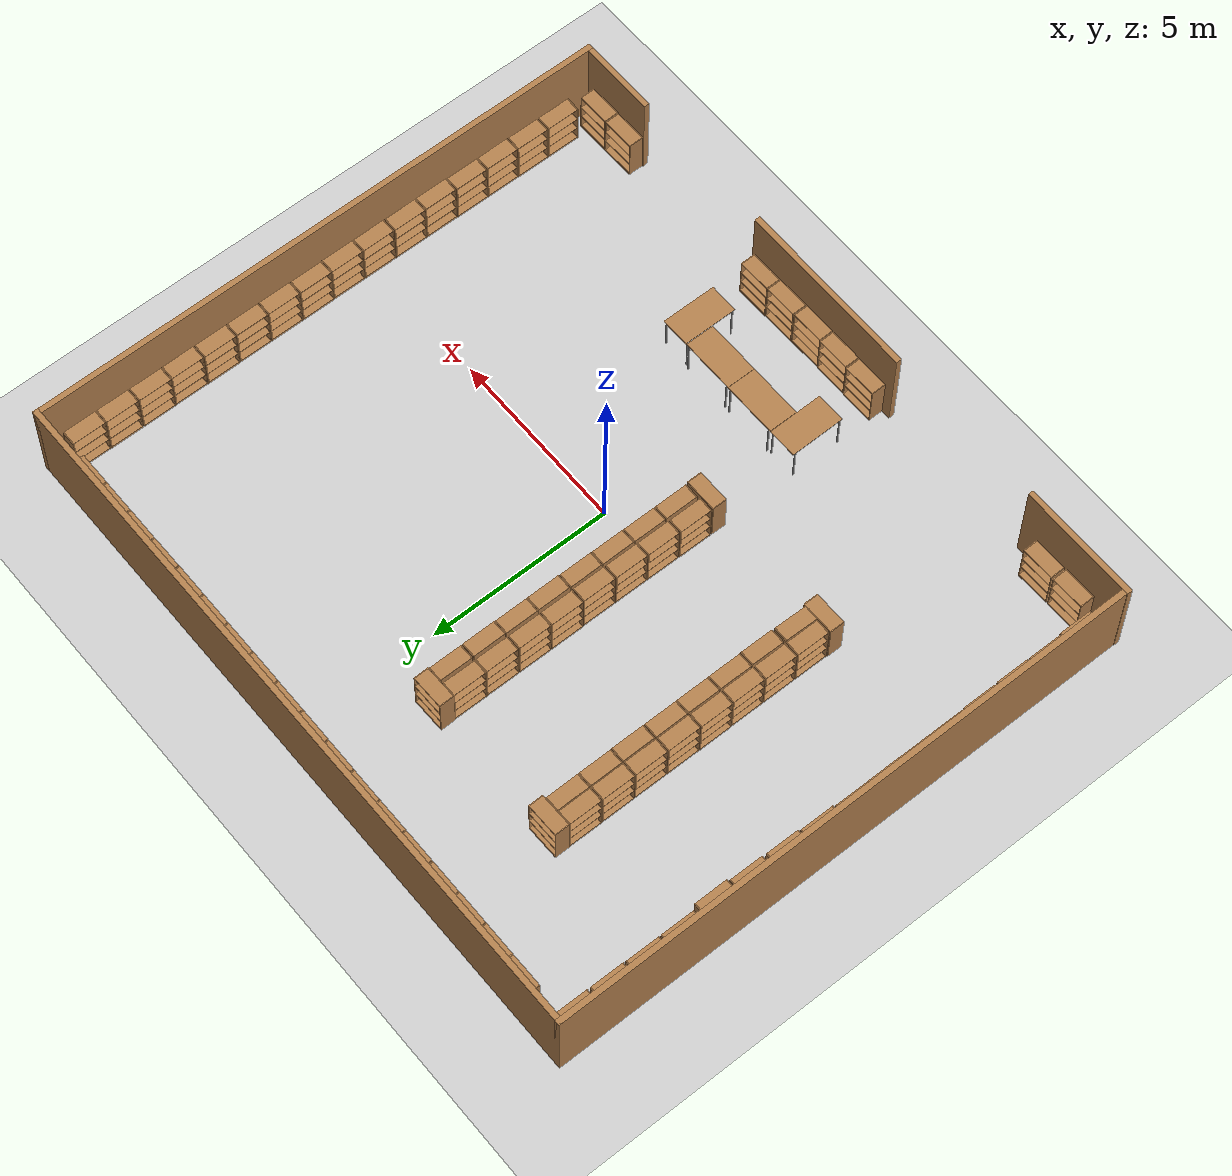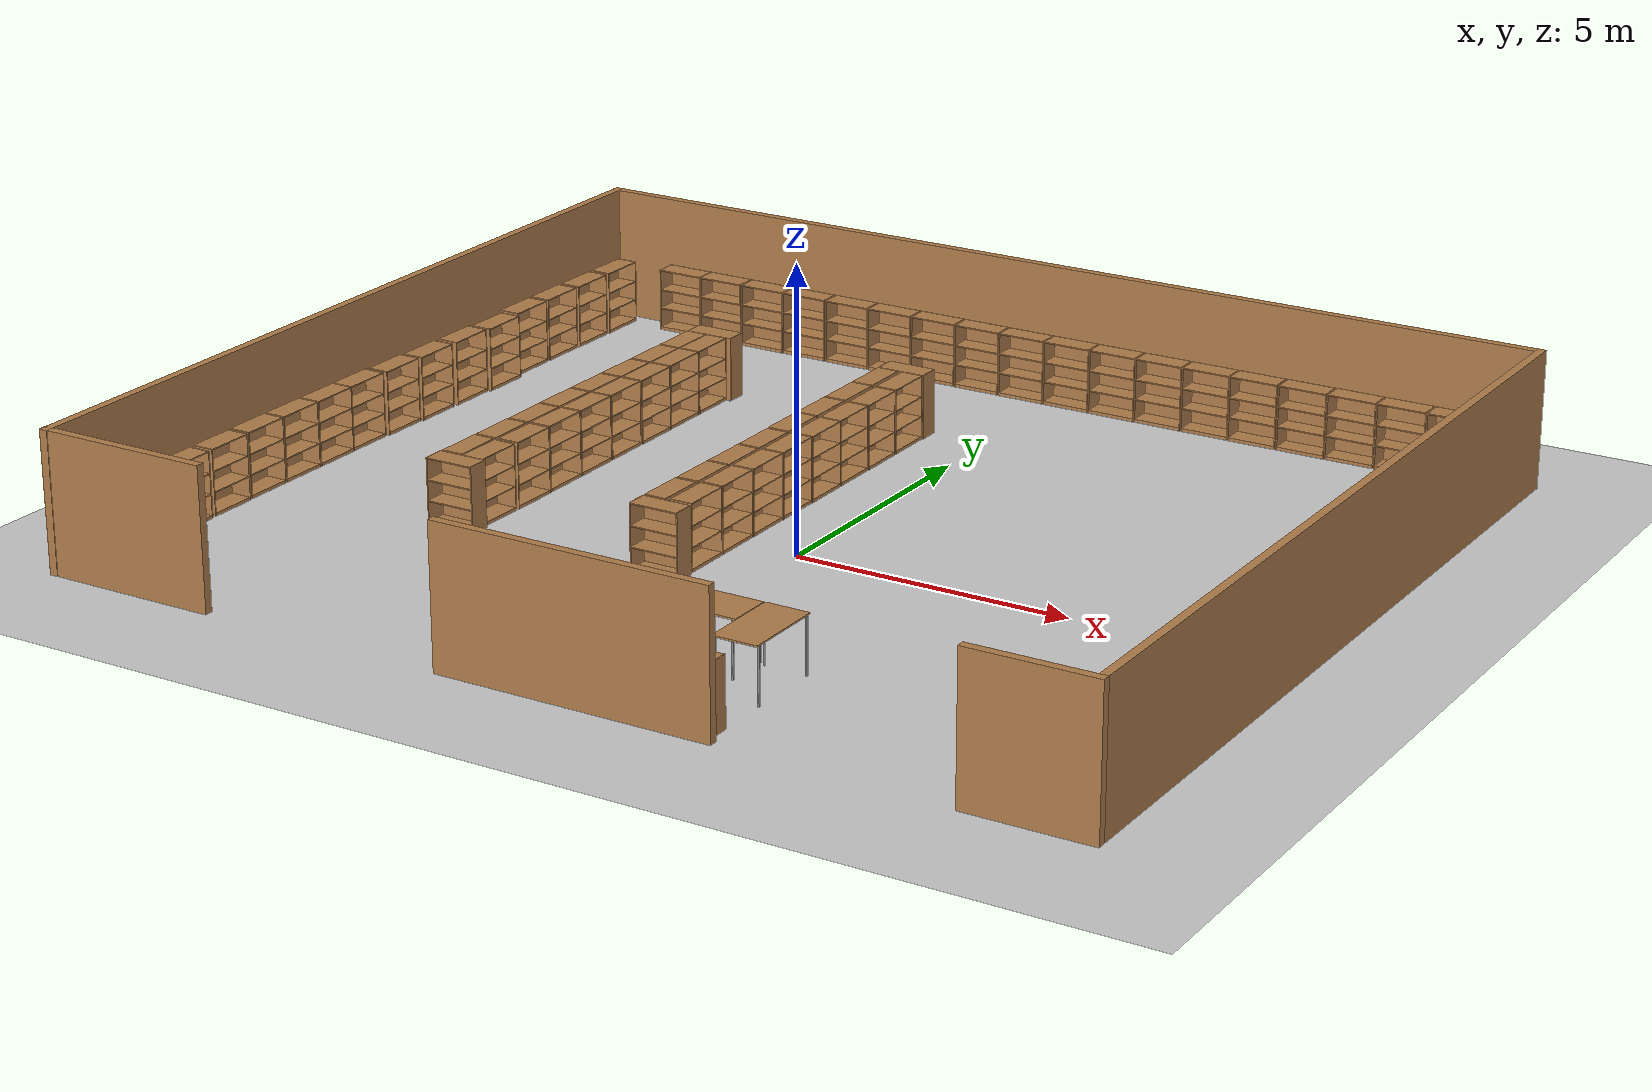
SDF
<sdf version="1.7">
 <world name="default">
  <light name="sun" type="directional">
   <pose>0 0 10 0 -0 0</pose>
   <diffuse>0.8 0.8 0.8 1</diffuse>
   <specular>0.2 0.2 0.2 1</specular>
   <attenuation>
    <range>1000</range>
    <constant>0.9</constant>
    <linear>0.01</linear>
    <quadratic>0.001</quadratic>
   </attenuation>
   <direction>-0.5 0.1 -0.9</direction>
   <spot><inner_angle>0</inner_angle><outer_angle>0</outer_angle><falloff>0</falloff></spot>
  </light>
  <model name="ground_plane">
   <static>1</static>
   <link name="link">
    <collision name="collision">
     <geometry><plane><normal>0 0 1</normal><size>100 100</size></plane></geometry>
     <surface><friction><ode><mu>100</mu><mu2>50</mu2></ode></friction></surface>
    </collision>
    <visual name="visual">
     <cast_shadows>0</cast_shadows>
     <geometry><plane><normal>0 0 1</normal><size>100 100</size></plane></geometry>
     <material>
      <script><uri>file://media/materials/scripts/gazebo.material</uri><name>Gazebo/Grey</name></script>
     </material>
    </visual>
   </link>
  </model>
  <gravity>0 0 -9.8</gravity>
  <magnetic_field>6e-06 2.3e-05 -4.2e-05</magnetic_field>
  <atmosphere type="adiabatic"/>
  <physics type="ode">
   <max_step_size>0.001</max_step_size>
   <real_time_factor>1</real_time_factor>
   <real_time_update_rate>1000</real_time_update_rate>
  </physics>
  <scene><ambient>0.4 0.4 0.4 1</ambient><background>0.7 0.7 0.7 1</background><shadows>1</shadows></scene>
  <audio><device>default</device></audio>
  <spherical_coordinates>
   <surface_model>EARTH_WGS84</surface_model>
   <latitude_deg>0</latitude_deg>
   <longitude_deg>0</longitude_deg>
   <elevation>0</elevation>
   <heading_deg>0</heading_deg>
  </spherical_coordinates>
  <model name="mart_walls">
   <pose>-0.362233 1.16692 0 0 -0 0</pose>
   <link name="Wall_10">
    <collision name="Wall_10_Collision">
     <geometry><box><size>5 0.15 2.5</size></box></geometry>
     <pose>0 0 1.25 0 -0 0</pose>
    </collision>
    <visual name="Wall_10_Visual">
     <pose>0 0 1.25 0 -0 0</pose>
     <geometry><box><size>5 0.15 2.5</size></box></geometry>
     <material>
      <script><uri>file://media/materials/scripts/gazebo.material</uri><name>Gazebo/Wood</name></script>
      <ambient>1 1 1 1</ambient>
     </material>
     <meta><layer>0</layer></meta>
    </visual>
    <pose>0.674648 -8.01815 0 0 -0 0</pose>
   </link>
   <link name="Wall_3">
    <collision name="Wall_3_Collision">
     <geometry><box><size>16.25 0.15 2.5</size></box></geometry>
     <pose>0 0 1.25 0 -0 0</pose>
    </collision>
    <visual name="Wall_3_Visual">
     <pose>0 0 1.25 0 -0 0</pose>
     <geometry><box><size>16.25 0.15 2.5</size></box></geometry>
     <material>
      <script><uri>file://media/materials/scripts/gazebo.material</uri><name>Gazebo/Wood</name></script>
      <ambient>1 1 1 1</ambient>
     </material>
     <meta><layer>0</layer></meta>
    </visual>
    <pose>-9.41858 -0 0 0 -0 1.5708</pose>
   </link>
   <link name="Wall_4">
    <collision name="Wall_4_Collision">
     <geometry><box><size>19 0.15 2.5</size></box></geometry>
     <pose>0 0 1.25 0 -0 0</pose>
    </collision>
    <visual name="Wall_4_Visual">
     <pose>0 0 1.25 0 -0 0</pose>
     <geometry><box><size>19 0.15 2.5</size></box></geometry>
     <material>
      <script><uri>file://media/materials/scripts/gazebo.material</uri><name>Gazebo/Wood</name></script>
      <ambient>1 1 1 1</ambient>
     </material>
     <meta><layer>0</layer></meta>
    </visual>
    <pose>0.006422 8.05 0 0 -0 0</pose>
   </link>
   <link name="Wall_5">
    <collision name="Wall_5_Collision">
     <geometry><box><size>16.25 0.15 2.5</size></box></geometry>
     <pose>0 0 1.25 0 -0 0</pose>
    </collision>
    <visual name="Wall_5_Visual">
     <pose>0 0 1.25 0 -0 0</pose>
     <geometry><box><size>16.25 0.15 2.5</size></box></geometry>
     <material>
      <script><uri>file://media/materials/scripts/gazebo.material</uri><name>Gazebo/Wood</name></script>
      <ambient>1 1 1 1</ambient>
     </material>
     <meta><layer>0</layer></meta>
    </visual>
    <pose>9.43142 -0 0 0 -0 -1.5708</pose>
   </link>
   <link name="Wall_6">
    <collision name="Wall_6_Collision">
     <geometry><box><size>2.25 0.15 2.5</size></box></geometry>
     <pose>0 0 1.25 0 -0 0</pose>
    </collision>
    <visual name="Wall_6_Visual">
     <pose>0 0 1.25 0 -0 0</pose>
     <geometry><box><size>2.25 0.15 2.5</size></box></geometry>
     <material>
      <script><uri>file://media/materials/scripts/gazebo.material</uri><name>Gazebo/Wood</name></script>
      <ambient>1 1 1 1</ambient>
     </material>
     <meta><layer>0</layer></meta>
    </visual>
    <pose>8.38142 -8.05 0 0 -0 3.14159</pose>
   </link>
   <link name="Wall_8">
    <collision name="Wall_8_Collision">
     <geometry><box><size>3.25 0.15 2.5</size></box></geometry>
     <pose>0 0 1.25 0 -0 0</pose>
    </collision>
    <visual name="Wall_8_Visual">
     <pose>0 0 1.25 0 -0 0</pose>
     <geometry><box><size>3.25 0.15 2.5</size></box></geometry>
     <material>
      <script><uri>file://media/materials/scripts/gazebo.material</uri><name>Gazebo/Wood</name></script>
      <ambient>1 1 1 1</ambient>
     </material>
     <meta><layer>0</layer></meta>
    </visual>
    <pose>-7.88142 -8.03854 0 0 -0 0</pose>
   </link>
   <static>1</static>
  </model>
  <model name="bookshelf">
   <static>1</static>
   <link name="link">
    <inertial><mass>1</mass></inertial>
    <collision name="back">
     <pose>0 0.005 0.6 0 -0 0</pose>
     <geometry><box><size>0.9 0.01 1.2</size></box></geometry>
    </collision>
    <visual name="visual1">
     <pose>0 0.005 0.6 0 -0 0</pose>
     <geometry><box><size>0.9 0.01 1.2</size></box></geometry>
     <material>
      <script><uri>file://media/materials/scripts/gazebo.material</uri><name>Gazebo/Wood</name></script>
     </material>
    </visual>
    <collision name="left_side">
     <pose>0.45 -0.195 0.6 0 -0 0</pose>
     <geometry><box><size>0.02 0.4 1.2</size></box></geometry>
    </collision>
    <visual name="visual2">
     <pose>0.45 -0.195 0.6 0 -0 0</pose>
     <geometry><box><size>0.02 0.4 1.2</size></box></geometry>
     <material>
      <script><uri>file://media/materials/scripts/gazebo.material</uri><name>Gazebo/Wood</name></script>
     </material>
    </visual>
    <collision name="right_side">
     <pose>-0.45 -0.195 0.6 0 -0 0</pose>
     <geometry><box><size>0.02 0.4 1.2</size></box></geometry>
    </collision>
    <visual name="visual3">
     <pose>-0.45 -0.195 0.6 0 -0 0</pose>
     <geometry><box><size>0.02 0.4 1.2</size></box></geometry>
     <material>
      <script><uri>file://media/materials/scripts/gazebo.material</uri><name>Gazebo/Wood</name></script>
     </material>
    </visual>
    <collision name="bottom">
     <pose>0 -0.195 0.03 0 -0 0</pose>
     <geometry><box><size>0.88 0.4 0.06</size></box></geometry>
    </collision>
    <visual name="visual4">
     <pose>0 -0.195 0.03 0 -0 0</pose>
     <geometry><box><size>0.88 0.4 0.06</size></box></geometry>
     <material>
      <script><uri>file://media/materials/scripts/gazebo.material</uri><name>Gazebo/Wood</name></script>
     </material>
    </visual>
    <collision name="top">
     <pose>0 -0.195 1.19 0 -0 0</pose>
     <geometry><box><size>0.88 0.4 0.02</size></box></geometry>
    </collision>
    <visual name="visual5">
     <pose>0 -0.195 1.19 0 -0 0</pose>
     <geometry><box><size>0.88 0.4 0.02</size></box></geometry>
     <material>
      <script><uri>file://media/materials/scripts/gazebo.material</uri><name>Gazebo/Wood</name></script>
     </material>
    </visual>
    <collision name="low_shelf">
     <pose>0 -0.195 0.43 0 -0 0</pose>
     <geometry><box><size>0.88 0.4 0.02</size></box></geometry>
    </collision>
    <visual name="visual6">
     <pose>0 -0.195 0.43 0 -0 0</pose>
     <geometry><box><size>0.88 0.4 0.02</size></box></geometry>
     <material>
      <script><uri>file://media/materials/scripts/gazebo.material</uri><name>Gazebo/Wood</name></script>
     </material>
    </visual>
    <collision name="high_shelf">
     <pose>0 -0.195 0.8 0 -0 0</pose>
     <geometry><box><size>0.88 0.4 0.02</size></box></geometry>
    </collision>
    <visual name="visual7">
     <pose>0 -0.195 0.8 0 -0 0</pose>
     <geometry><box><size>0.88 0.4 0.02</size></box></geometry>
     <material>
      <script><uri>file://media/materials/scripts/gazebo.material</uri><name>Gazebo/Wood</name></script>
     </material>
    </visual>
   </link>
   <pose>-5.54772 -1.59367 0 0 -0 0</pose>
  </model>
  <model name="bookshelf_clone">
   <static>1</static>
   <link name="link">
    <inertial><mass>1</mass></inertial>
    <collision name="back">
     <pose>0 0.005 0.6 0 -0 0</pose>
     <geometry><box><size>0.9 0.01 1.2</size></box></geometry>
    </collision>
    <visual name="visual1">
     <pose>0 0.005 0.6 0 -0 0</pose>
     <geometry><box><size>0.9 0.01 1.2</size></box></geometry>
     <material>
      <script><uri>file://media/materials/scripts/gazebo.material</uri><name>Gazebo/Wood</name></script>
     </material>
    </visual>
    <collision name="left_side">
     <pose>0.45 -0.195 0.6 0 -0 0</pose>
     <geometry><box><size>0.02 0.4 1.2</size></box></geometry>
    </collision>
    <visual name="visual2">
     <pose>0.45 -0.195 0.6 0 -0 0</pose>
     <geometry><box><size>0.02 0.4 1.2</size></box></geometry>
     <material>
      <script><uri>file://media/materials/scripts/gazebo.material</uri><name>Gazebo/Wood</name></script>
     </material>
    </visual>
    <collision name="right_side">
     <pose>-0.45 -0.195 0.6 0 -0 0</pose>
     <geometry><box><size>0.02 0.4 1.2</size></box></geometry>
    </collision>
    <visual name="visual3">
     <pose>-0.45 -0.195 0.6 0 -0 0</pose>
     <geometry><box><size>0.02 0.4 1.2</size></box></geometry>
     <material>
      <script><uri>file://media/materials/scripts/gazebo.material</uri><name>Gazebo/Wood</name></script>
     </material>
    </visual>
    <collision name="bottom">
     <pose>0 -0.195 0.03 0 -0 0</pose>
     <geometry><box><size>0.88 0.4 0.06</size></box></geometry>
    </collision>
    <visual name="visual4">
     <pose>0 -0.195 0.03 0 -0 0</pose>
     <geometry><box><size>0.88 0.4 0.06</size></box></geometry>
     <material>
      <script><uri>file://media/materials/scripts/gazebo.material</uri><name>Gazebo/Wood</name></script>
     </material>
    </visual>
    <collision name="top">
     <pose>0 -0.195 1.19 0 -0 0</pose>
     <geometry><box><size>0.88 0.4 0.02</size></box></geometry>
    </collision>
    <visual name="visual5">
     <pose>0 -0.195 1.19 0 -0 0</pose>
     <geometry><box><size>0.88 0.4 0.02</size></box></geometry>
     <material>
      <script><uri>file://media/materials/scripts/gazebo.material</uri><name>Gazebo/Wood</name></script>
     </material>
    </visual>
    <collision name="low_shelf">
     <pose>0 -0.195 0.43 0 -0 0</pose>
     <geometry><box><size>0.88 0.4 0.02</size></box></geometry>
    </collision>
    <visual name="visual6">
     <pose>0 -0.195 0.43 0 -0 0</pose>
     <geometry><box><size>0.88 0.4 0.02</size></box></geometry>
     <material>
      <script><uri>file://media/materials/scripts/gazebo.material</uri><name>Gazebo/Wood</name></script>
     </material>
    </visual>
    <collision name="high_shelf">
     <pose>0 -0.195 0.8 0 -0 0</pose>
     <geometry><box><size>0.88 0.4 0.02</size></box></geometry>
    </collision>
    <visual name="visual7">
     <pose>0 -0.195 0.8 0 -0 0</pose>
     <geometry><box><size>0.88 0.4 0.02</size></box></geometry>
     <material>
      <script><uri>file://media/materials/scripts/gazebo.material</uri><name>Gazebo/Wood</name></script>
     </material>
    </visual>
   </link>
   <pose>-6.18598 9.11437 0 0 -0 0</pose>
  </model>
  <model name="table">
   <static>1</static>
   <link name="link">
    <collision name="surface">
     <pose>0 0 1 0 -0 0</pose>
     <geometry><box><size>1.5 0.8 0.03</size></box></geometry>
     <surface><friction><ode><mu>0.6</mu><mu2>0.6</mu2></ode></friction></surface>
    </collision>
    <visual name="visual1">
     <pose>0 0 1 0 -0 0</pose>
     <geometry><box><size>1.5 0.8 0.03</size></box></geometry>
     <material>
      <script><uri>file://media/materials/scripts/gazebo.material</uri><name>Gazebo/Wood</name></script>
     </material>
    </visual>
    <collision name="front_left_leg">
     <pose>0.68 0.38 0.5 0 -0 0</pose>
     <geometry><cylinder><radius>0.02</radius><length>1</length></cylinder></geometry>
    </collision>
    <visual name="front_left_leg">
     <pose>0.68 0.38 0.5 0 -0 0</pose>
     <geometry><cylinder><radius>0.02</radius><length>1</length></cylinder></geometry>
     <material>
      <script><uri>file://media/materials/scripts/gazebo.material</uri><name>Gazebo/Grey</name></script>
     </material>
    </visual>
    <collision name="front_right_leg">
     <pose>0.68 -0.38 0.5 0 -0 0</pose>
     <geometry><cylinder><radius>0.02</radius><length>1</length></cylinder></geometry>
    </collision>
    <visual name="front_right_leg">
     <pose>0.68 -0.38 0.5 0 -0 0</pose>
     <geometry><cylinder><radius>0.02</radius><length>1</length></cylinder></geometry>
     <material>
      <script><uri>file://media/materials/scripts/gazebo.material</uri><name>Gazebo/Grey</name></script>
     </material>
    </visual>
    <collision name="back_right_leg">
     <pose>-0.68 -0.38 0.5 0 -0 0</pose>
     <geometry><cylinder><radius>0.02</radius><length>1</length></cylinder></geometry>
    </collision>
    <visual name="back_right_leg">
     <pose>-0.68 -0.38 0.5 0 -0 0</pose>
     <geometry><cylinder><radius>0.02</radius><length>1</length></cylinder></geometry>
     <material>
      <script><uri>file://media/materials/scripts/gazebo.material</uri><name>Gazebo/Grey</name></script>
     </material>
    </visual>
    <collision name="back_left_leg">
     <pose>-0.68 0.38 0.5 0 -0 0</pose>
     <geometry><cylinder><radius>0.02</radius><length>1</length></cylinder></geometry>
    </collision>
    <visual name="back_left_leg">
     <pose>-0.68 0.38 0.5 0 -0 0</pose>
     <geometry><cylinder><radius>0.02</radius><length>1</length></cylinder></geometry>
     <material>
      <script><uri>file://media/materials/scripts/gazebo.material</uri><name>Gazebo/Grey</name></script>
     </material>
    </visual>
   </link>
   <pose>1.12795 -4.37949 0 0 -0 0</pose>
  </model>
  <model name="bookshelf_clone_0">
   <static>1</static>
   <link name="link">
    <inertial><mass>1</mass></inertial>
    <collision name="back">
     <pose>0 0.005 0.6 0 -0 0</pose>
     <geometry><box><size>0.9 0.01 1.2</size></box></geometry>
    </collision>
    <visual name="visual1">
     <pose>0 0.005 0.6 0 -0 0</pose>
     <geometry><box><size>0.9 0.01 1.2</size></box></geometry>
     <material>
      <script><uri>file://media/materials/scripts/gazebo.material</uri><name>Gazebo/Wood</name></script>
     </material>
    </visual>
    <collision name="left_side">
     <pose>0.45 -0.195 0.6 0 -0 0</pose>
     <geometry><box><size>0.02 0.4 1.2</size></box></geometry>
    </collision>
    <visual name="visual2">
     <pose>0.45 -0.195 0.6 0 -0 0</pose>
     <geometry><box><size>0.02 0.4 1.2</size></box></geometry>
     <material>
      <script><uri>file://media/materials/scripts/gazebo.material</uri><name>Gazebo/Wood</name></script>
     </material>
    </visual>
    <collision name="right_side">
     <pose>-0.45 -0.195 0.6 0 -0 0</pose>
     <geometry><box><size>0.02 0.4 1.2</size></box></geometry>
    </collision>
    <visual name="visual3">
     <pose>-0.45 -0.195 0.6 0 -0 0</pose>
     <geometry><box><size>0.02 0.4 1.2</size></box></geometry>
     <material>
      <script><uri>file://media/materials/scripts/gazebo.material</uri><name>Gazebo/Wood</name></script>
     </material>
    </visual>
    <collision name="bottom">
     <pose>0 -0.195 0.03 0 -0 0</pose>
     <geometry><box><size>0.88 0.4 0.06</size></box></geometry>
    </collision>
    <visual name="visual4">
     <pose>0 -0.195 0.03 0 -0 0</pose>
     <geometry><box><size>0.88 0.4 0.06</size></box></geometry>
     <material>
      <script><uri>file://media/materials/scripts/gazebo.material</uri><name>Gazebo/Wood</name></script>
     </material>
    </visual>
    <collision name="top">
     <pose>0 -0.195 1.19 0 -0 0</pose>
     <geometry><box><size>0.88 0.4 0.02</size></box></geometry>
    </collision>
    <visual name="visual5">
     <pose>0 -0.195 1.19 0 -0 0</pose>
     <geometry><box><size>0.88 0.4 0.02</size></box></geometry>
     <material>
      <script><uri>file://media/materials/scripts/gazebo.material</uri><name>Gazebo/Wood</name></script>
     </material>
    </visual>
    <collision name="low_shelf">
     <pose>0 -0.195 0.43 0 -0 0</pose>
     <geometry><box><size>0.88 0.4 0.02</size></box></geometry>
    </collision>
    <visual name="visual6">
     <pose>0 -0.195 0.43 0 -0 0</pose>
     <geometry><box><size>0.88 0.4 0.02</size></box></geometry>
     <material>
      <script><uri>file://media/materials/scripts/gazebo.material</uri><name>Gazebo/Wood</name></script>
     </material>
    </visual>
    <collision name="high_shelf">
     <pose>0 -0.195 0.8 0 -0 0</pose>
     <geometry><box><size>0.88 0.4 0.02</size></box></geometry>
    </collision>
    <visual name="visual7">
     <pose>0 -0.195 0.8 0 -0 0</pose>
     <geometry><box><size>0.88 0.4 0.02</size></box></geometry>
     <material>
      <script><uri>file://media/materials/scripts/gazebo.material</uri><name>Gazebo/Wood</name></script>
     </material>
    </visual>
   </link>
   <pose>-9.67669 0.644456 0 0 -0 1.56663</pose>
  </model>
  <model name="bookshelf_clone_0_clone">
   <static>1</static>
   <link name="link">
    <inertial><mass>1</mass></inertial>
    <collision name="back">
     <pose>0 0.005 0.6 0 -0 0</pose>
     <geometry><box><size>0.9 0.01 1.2</size></box></geometry>
    </collision>
    <visual name="visual1">
     <pose>0 0.005 0.6 0 -0 0</pose>
     <geometry><box><size>0.9 0.01 1.2</size></box></geometry>
     <material>
      <script><uri>file://media/materials/scripts/gazebo.material</uri><name>Gazebo/Wood</name></script>
     </material>
    </visual>
    <collision name="left_side">
     <pose>0.45 -0.195 0.6 0 -0 0</pose>
     <geometry><box><size>0.02 0.4 1.2</size></box></geometry>
    </collision>
    <visual name="visual2">
     <pose>0.45 -0.195 0.6 0 -0 0</pose>
     <geometry><box><size>0.02 0.4 1.2</size></box></geometry>
     <material>
      <script><uri>file://media/materials/scripts/gazebo.material</uri><name>Gazebo/Wood</name></script>
     </material>
    </visual>
    <collision name="right_side">
     <pose>-0.45 -0.195 0.6 0 -0 0</pose>
     <geometry><box><size>0.02 0.4 1.2</size></box></geometry>
    </collision>
    <visual name="visual3">
     <pose>-0.45 -0.195 0.6 0 -0 0</pose>
     <geometry><box><size>0.02 0.4 1.2</size></box></geometry>
     <material>
      <script><uri>file://media/materials/scripts/gazebo.material</uri><name>Gazebo/Wood</name></script>
     </material>
    </visual>
    <collision name="bottom">
     <pose>0 -0.195 0.03 0 -0 0</pose>
     <geometry><box><size>0.88 0.4 0.06</size></box></geometry>
    </collision>
    <visual name="visual4">
     <pose>0 -0.195 0.03 0 -0 0</pose>
     <geometry><box><size>0.88 0.4 0.06</size></box></geometry>
     <material>
      <script><uri>file://media/materials/scripts/gazebo.material</uri><name>Gazebo/Wood</name></script>
     </material>
    </visual>
    <collision name="top">
     <pose>0 -0.195 1.19 0 -0 0</pose>
     <geometry><box><size>0.88 0.4 0.02</size></box></geometry>
    </collision>
    <visual name="visual5">
     <pose>0 -0.195 1.19 0 -0 0</pose>
     <geometry><box><size>0.88 0.4 0.02</size></box></geometry>
     <material>
      <script><uri>file://media/materials/scripts/gazebo.material</uri><name>Gazebo/Wood</name></script>
     </material>
    </visual>
    <collision name="low_shelf">
     <pose>0 -0.195 0.43 0 -0 0</pose>
     <geometry><box><size>0.88 0.4 0.02</size></box></geometry>
    </collision>
    <visual name="visual6">
     <pose>0 -0.195 0.43 0 -0 0</pose>
     <geometry><box><size>0.88 0.4 0.02</size></box></geometry>
     <material>
      <script><uri>file://media/materials/scripts/gazebo.material</uri><name>Gazebo/Wood</name></script>
     </material>
    </visual>
    <collision name="high_shelf">
     <pose>0 -0.195 0.8 0 -0 0</pose>
     <geometry><box><size>0.88 0.4 0.02</size></box></geometry>
    </collision>
    <visual name="visual7">
     <pose>0 -0.195 0.8 0 -0 0</pose>
     <geometry><box><size>0.88 0.4 0.02</size></box></geometry>
     <material>
      <script><uri>file://media/materials/scripts/gazebo.material</uri><name>Gazebo/Wood</name></script>
     </material>
    </visual>
   </link>
   <pose>-9.67578 -0.269706 0 0 -0 1.56663</pose>
  </model>
  <model name="bookshelf_clone_0_clone_0">
   <static>1</static>
   <link name="link">
    <inertial><mass>1</mass></inertial>
    <collision name="back">
     <pose>0 0.005 0.6 0 -0 0</pose>
     <geometry><box><size>0.9 0.01 1.2</size></box></geometry>
    </collision>
    <visual name="visual1">
     <pose>0 0.005 0.6 0 -0 0</pose>
     <geometry><box><size>0.9 0.01 1.2</size></box></geometry>
     <material>
      <script><uri>file://media/materials/scripts/gazebo.material</uri><name>Gazebo/Wood</name></script>
     </material>
    </visual>
    <collision name="left_side">
     <pose>0.45 -0.195 0.6 0 -0 0</pose>
     <geometry><box><size>0.02 0.4 1.2</size></box></geometry>
    </collision>
    <visual name="visual2">
     <pose>0.45 -0.195 0.6 0 -0 0</pose>
     <geometry><box><size>0.02 0.4 1.2</size></box></geometry>
     <material>
      <script><uri>file://media/materials/scripts/gazebo.material</uri><name>Gazebo/Wood</name></script>
     </material>
    </visual>
    <collision name="right_side">
     <pose>-0.45 -0.195 0.6 0 -0 0</pose>
     <geometry><box><size>0.02 0.4 1.2</size></box></geometry>
    </collision>
    <visual name="visual3">
     <pose>-0.45 -0.195 0.6 0 -0 0</pose>
     <geometry><box><size>0.02 0.4 1.2</size></box></geometry>
     <material>
      <script><uri>file://media/materials/scripts/gazebo.material</uri><name>Gazebo/Wood</name></script>
     </material>
    </visual>
    <collision name="bottom">
     <pose>0 -0.195 0.03 0 -0 0</pose>
     <geometry><box><size>0.88 0.4 0.06</size></box></geometry>
    </collision>
    <visual name="visual4">
     <pose>0 -0.195 0.03 0 -0 0</pose>
     <geometry><box><size>0.88 0.4 0.06</size></box></geometry>
     <material>
      <script><uri>file://media/materials/scripts/gazebo.material</uri><name>Gazebo/Wood</name></script>
     </material>
    </visual>
    <collision name="top">
     <pose>0 -0.195 1.19 0 -0 0</pose>
     <geometry><box><size>0.88 0.4 0.02</size></box></geometry>
    </collision>
    <visual name="visual5">
     <pose>0 -0.195 1.19 0 -0 0</pose>
     <geometry><box><size>0.88 0.4 0.02</size></box></geometry>
     <material>
      <script><uri>file://media/materials/scripts/gazebo.material</uri><name>Gazebo/Wood</name></script>
     </material>
    </visual>
    <collision name="low_shelf">
     <pose>0 -0.195 0.43 0 -0 0</pose>
     <geometry><box><size>0.88 0.4 0.02</size></box></geometry>
    </collision>
    <visual name="visual6">
     <pose>0 -0.195 0.43 0 -0 0</pose>
     <geometry><box><size>0.88 0.4 0.02</size></box></geometry>
     <material>
      <script><uri>file://media/materials/scripts/gazebo.material</uri><name>Gazebo/Wood</name></script>
     </material>
    </visual>
    <collision name="high_shelf">
     <pose>0 -0.195 0.8 0 -0 0</pose>
     <geometry><box><size>0.88 0.4 0.02</size></box></geometry>
    </collision>
    <visual name="visual7">
     <pose>0 -0.195 0.8 0 -0 0</pose>
     <geometry><box><size>0.88 0.4 0.02</size></box></geometry>
     <material>
      <script><uri>file://media/materials/scripts/gazebo.material</uri><name>Gazebo/Wood</name></script>
     </material>
    </visual>
   </link>
   <pose>-9.68117 -1.19587 0 0 -0 1.56663</pose>
  </model>
  <model name="bookshelf_clone_0_clone_0_clone">
   <static>1</static>
   <link name="link">
    <inertial><mass>1</mass></inertial>
    <collision name="back">
     <pose>0 0.005 0.6 0 -0 0</pose>
     <geometry><box><size>0.9 0.01 1.2</size></box></geometry>
    </collision>
    <visual name="visual1">
     <pose>0 0.005 0.6 0 -0 0</pose>
     <geometry><box><size>0.9 0.01 1.2</size></box></geometry>
     <material>
      <script><uri>file://media/materials/scripts/gazebo.material</uri><name>Gazebo/Wood</name></script>
     </material>
    </visual>
    <collision name="left_side">
     <pose>0.45 -0.195 0.6 0 -0 0</pose>
     <geometry><box><size>0.02 0.4 1.2</size></box></geometry>
    </collision>
    <visual name="visual2">
     <pose>0.45 -0.195 0.6 0 -0 0</pose>
     <geometry><box><size>0.02 0.4 1.2</size></box></geometry>
     <material>
      <script><uri>file://media/materials/scripts/gazebo.material</uri><name>Gazebo/Wood</name></script>
     </material>
    </visual>
    <collision name="right_side">
     <pose>-0.45 -0.195 0.6 0 -0 0</pose>
     <geometry><box><size>0.02 0.4 1.2</size></box></geometry>
    </collision>
    <visual name="visual3">
     <pose>-0.45 -0.195 0.6 0 -0 0</pose>
     <geometry><box><size>0.02 0.4 1.2</size></box></geometry>
     <material>
      <script><uri>file://media/materials/scripts/gazebo.material</uri><name>Gazebo/Wood</name></script>
     </material>
    </visual>
    <collision name="bottom">
     <pose>0 -0.195 0.03 0 -0 0</pose>
     <geometry><box><size>0.88 0.4 0.06</size></box></geometry>
    </collision>
    <visual name="visual4">
     <pose>0 -0.195 0.03 0 -0 0</pose>
     <geometry><box><size>0.88 0.4 0.06</size></box></geometry>
     <material>
      <script><uri>file://media/materials/scripts/gazebo.material</uri><name>Gazebo/Wood</name></script>
     </material>
    </visual>
    <collision name="top">
     <pose>0 -0.195 1.19 0 -0 0</pose>
     <geometry><box><size>0.88 0.4 0.02</size></box></geometry>
    </collision>
    <visual name="visual5">
     <pose>0 -0.195 1.19 0 -0 0</pose>
     <geometry><box><size>0.88 0.4 0.02</size></box></geometry>
     <material>
      <script><uri>file://media/materials/scripts/gazebo.material</uri><name>Gazebo/Wood</name></script>
     </material>
    </visual>
    <collision name="low_shelf">
     <pose>0 -0.195 0.43 0 -0 0</pose>
     <geometry><box><size>0.88 0.4 0.02</size></box></geometry>
    </collision>
    <visual name="visual6">
     <pose>0 -0.195 0.43 0 -0 0</pose>
     <geometry><box><size>0.88 0.4 0.02</size></box></geometry>
     <material>
      <script><uri>file://media/materials/scripts/gazebo.material</uri><name>Gazebo/Wood</name></script>
     </material>
    </visual>
    <collision name="high_shelf">
     <pose>0 -0.195 0.8 0 -0 0</pose>
     <geometry><box><size>0.88 0.4 0.02</size></box></geometry>
    </collision>
    <visual name="visual7">
     <pose>0 -0.195 0.8 0 -0 0</pose>
     <geometry><box><size>0.88 0.4 0.02</size></box></geometry>
     <material>
      <script><uri>file://media/materials/scripts/gazebo.material</uri><name>Gazebo/Wood</name></script>
     </material>
    </visual>
   </link>
   <pose>-9.68531 -2.12853 0 0 -0 1.56663</pose>
  </model>
  <model name="bookshelf_clone_0_clone_0_clone_clone">
   <static>1</static>
   <link name="link">
    <inertial><mass>1</mass></inertial>
    <collision name="back">
     <pose>0 0.005 0.6 0 -0 0</pose>
     <geometry><box><size>0.9 0.01 1.2</size></box></geometry>
    </collision>
    <visual name="visual1">
     <pose>0 0.005 0.6 0 -0 0</pose>
     <geometry><box><size>0.9 0.01 1.2</size></box></geometry>
     <material>
      <script><uri>file://media/materials/scripts/gazebo.material</uri><name>Gazebo/Wood</name></script>
     </material>
    </visual>
    <collision name="left_side">
     <pose>0.45 -0.195 0.6 0 -0 0</pose>
     <geometry><box><size>0.02 0.4 1.2</size></box></geometry>
    </collision>
    <visual name="visual2">
     <pose>0.45 -0.195 0.6 0 -0 0</pose>
     <geometry><box><size>0.02 0.4 1.2</size></box></geometry>
     <material>
      <script><uri>file://media/materials/scripts/gazebo.material</uri><name>Gazebo/Wood</name></script>
     </material>
    </visual>
    <collision name="right_side">
     <pose>-0.45 -0.195 0.6 0 -0 0</pose>
     <geometry><box><size>0.02 0.4 1.2</size></box></geometry>
    </collision>
    <visual name="visual3">
     <pose>-0.45 -0.195 0.6 0 -0 0</pose>
     <geometry><box><size>0.02 0.4 1.2</size></box></geometry>
     <material>
      <script><uri>file://media/materials/scripts/gazebo.material</uri><name>Gazebo/Wood</name></script>
     </material>
    </visual>
    <collision name="bottom">
     <pose>0 -0.195 0.03 0 -0 0</pose>
     <geometry><box><size>0.88 0.4 0.06</size></box></geometry>
    </collision>
    <visual name="visual4">
     <pose>0 -0.195 0.03 0 -0 0</pose>
     <geometry><box><size>0.88 0.4 0.06</size></box></geometry>
     <material>
      <script><uri>file://media/materials/scripts/gazebo.material</uri><name>Gazebo/Wood</name></script>
     </material>
    </visual>
    <collision name="top">
     <pose>0 -0.195 1.19 0 -0 0</pose>
     <geometry><box><size>0.88 0.4 0.02</size></box></geometry>
    </collision>
    <visual name="visual5">
     <pose>0 -0.195 1.19 0 -0 0</pose>
     <geometry><box><size>0.88 0.4 0.02</size></box></geometry>
     <material>
      <script><uri>file://media/materials/scripts/gazebo.material</uri><name>Gazebo/Wood</name></script>
     </material>
    </visual>
    <collision name="low_shelf">
     <pose>0 -0.195 0.43 0 -0 0</pose>
     <geometry><box><size>0.88 0.4 0.02</size></box></geometry>
    </collision>
    <visual name="visual6">
     <pose>0 -0.195 0.43 0 -0 0</pose>
     <geometry><box><size>0.88 0.4 0.02</size></box></geometry>
     <material>
      <script><uri>file://media/materials/scripts/gazebo.material</uri><name>Gazebo/Wood</name></script>
     </material>
    </visual>
    <collision name="high_shelf">
     <pose>0 -0.195 0.8 0 -0 0</pose>
     <geometry><box><size>0.88 0.4 0.02</size></box></geometry>
    </collision>
    <visual name="visual7">
     <pose>0 -0.195 0.8 0 -0 0</pose>
     <geometry><box><size>0.88 0.4 0.02</size></box></geometry>
     <material>
      <script><uri>file://media/materials/scripts/gazebo.material</uri><name>Gazebo/Wood</name></script>
     </material>
    </visual>
   </link>
   <pose>-9.67154 -3.09417 0 0 -0 1.56663</pose>
  </model>
  <model name="bookshelf_clone_0_clone_0_clone_clone_0">
   <static>1</static>
   <link name="link">
    <inertial><mass>1</mass></inertial>
    <collision name="back">
     <pose>0 0.005 0.6 0 -0 0</pose>
     <geometry><box><size>0.9 0.01 1.2</size></box></geometry>
    </collision>
    <visual name="visual1">
     <pose>0 0.005 0.6 0 -0 0</pose>
     <geometry><box><size>0.9 0.01 1.2</size></box></geometry>
     <material>
      <script><uri>file://media/materials/scripts/gazebo.material</uri><name>Gazebo/Wood</name></script>
     </material>
    </visual>
    <collision name="left_side">
     <pose>0.45 -0.195 0.6 0 -0 0</pose>
     <geometry><box><size>0.02 0.4 1.2</size></box></geometry>
    </collision>
    <visual name="visual2">
     <pose>0.45 -0.195 0.6 0 -0 0</pose>
     <geometry><box><size>0.02 0.4 1.2</size></box></geometry>
     <material>
      <script><uri>file://media/materials/scripts/gazebo.material</uri><name>Gazebo/Wood</name></script>
     </material>
    </visual>
    <collision name="right_side">
     <pose>-0.45 -0.195 0.6 0 -0 0</pose>
     <geometry><box><size>0.02 0.4 1.2</size></box></geometry>
    </collision>
    <visual name="visual3">
     <pose>-0.45 -0.195 0.6 0 -0 0</pose>
     <geometry><box><size>0.02 0.4 1.2</size></box></geometry>
     <material>
      <script><uri>file://media/materials/scripts/gazebo.material</uri><name>Gazebo/Wood</name></script>
     </material>
    </visual>
    <collision name="bottom">
     <pose>0 -0.195 0.03 0 -0 0</pose>
     <geometry><box><size>0.88 0.4 0.06</size></box></geometry>
    </collision>
    <visual name="visual4">
     <pose>0 -0.195 0.03 0 -0 0</pose>
     <geometry><box><size>0.88 0.4 0.06</size></box></geometry>
     <material>
      <script><uri>file://media/materials/scripts/gazebo.material</uri><name>Gazebo/Wood</name></script>
     </material>
    </visual>
    <collision name="top">
     <pose>0 -0.195 1.19 0 -0 0</pose>
     <geometry><box><size>0.88 0.4 0.02</size></box></geometry>
    </collision>
    <visual name="visual5">
     <pose>0 -0.195 1.19 0 -0 0</pose>
     <geometry><box><size>0.88 0.4 0.02</size></box></geometry>
     <material>
      <script><uri>file://media/materials/scripts/gazebo.material</uri><name>Gazebo/Wood</name></script>
     </material>
    </visual>
    <collision name="low_shelf">
     <pose>0 -0.195 0.43 0 -0 0</pose>
     <geometry><box><size>0.88 0.4 0.02</size></box></geometry>
    </collision>
    <visual name="visual6">
     <pose>0 -0.195 0.43 0 -0 0</pose>
     <geometry><box><size>0.88 0.4 0.02</size></box></geometry>
     <material>
      <script><uri>file://media/materials/scripts/gazebo.material</uri><name>Gazebo/Wood</name></script>
     </material>
    </visual>
    <collision name="high_shelf">
     <pose>0 -0.195 0.8 0 -0 0</pose>
     <geometry><box><size>0.88 0.4 0.02</size></box></geometry>
    </collision>
    <visual name="visual7">
     <pose>0 -0.195 0.8 0 -0 0</pose>
     <geometry><box><size>0.88 0.4 0.02</size></box></geometry>
     <material>
      <script><uri>file://media/materials/scripts/gazebo.material</uri><name>Gazebo/Wood</name></script>
     </material>
    </visual>
   </link>
   <pose>-9.66259 -4.09234 0 0 -0 1.56663</pose>
  </model>
  <model name="bookshelf_clone_0_clone_0_clone_clone_1">
   <static>1</static>
   <link name="link">
    <inertial><mass>1</mass></inertial>
    <collision name="back">
     <pose>0 0.005 0.6 0 -0 0</pose>
     <geometry><box><size>0.9 0.01 1.2</size></box></geometry>
    </collision>
    <visual name="visual1">
     <pose>0 0.005 0.6 0 -0 0</pose>
     <geometry><box><size>0.9 0.01 1.2</size></box></geometry>
     <material>
      <script><uri>file://media/materials/scripts/gazebo.material</uri><name>Gazebo/Wood</name></script>
     </material>
    </visual>
    <collision name="left_side">
     <pose>0.45 -0.195 0.6 0 -0 0</pose>
     <geometry><box><size>0.02 0.4 1.2</size></box></geometry>
    </collision>
    <visual name="visual2">
     <pose>0.45 -0.195 0.6 0 -0 0</pose>
     <geometry><box><size>0.02 0.4 1.2</size></box></geometry>
     <material>
      <script><uri>file://media/materials/scripts/gazebo.material</uri><name>Gazebo/Wood</name></script>
     </material>
    </visual>
    <collision name="right_side">
     <pose>-0.45 -0.195 0.6 0 -0 0</pose>
     <geometry><box><size>0.02 0.4 1.2</size></box></geometry>
    </collision>
    <visual name="visual3">
     <pose>-0.45 -0.195 0.6 0 -0 0</pose>
     <geometry><box><size>0.02 0.4 1.2</size></box></geometry>
     <material>
      <script><uri>file://media/materials/scripts/gazebo.material</uri><name>Gazebo/Wood</name></script>
     </material>
    </visual>
    <collision name="bottom">
     <pose>0 -0.195 0.03 0 -0 0</pose>
     <geometry><box><size>0.88 0.4 0.06</size></box></geometry>
    </collision>
    <visual name="visual4">
     <pose>0 -0.195 0.03 0 -0 0</pose>
     <geometry><box><size>0.88 0.4 0.06</size></box></geometry>
     <material>
      <script><uri>file://media/materials/scripts/gazebo.material</uri><name>Gazebo/Wood</name></script>
     </material>
    </visual>
    <collision name="top">
     <pose>0 -0.195 1.19 0 -0 0</pose>
     <geometry><box><size>0.88 0.4 0.02</size></box></geometry>
    </collision>
    <visual name="visual5">
     <pose>0 -0.195 1.19 0 -0 0</pose>
     <geometry><box><size>0.88 0.4 0.02</size></box></geometry>
     <material>
      <script><uri>file://media/materials/scripts/gazebo.material</uri><name>Gazebo/Wood</name></script>
     </material>
    </visual>
    <collision name="low_shelf">
     <pose>0 -0.195 0.43 0 -0 0</pose>
     <geometry><box><size>0.88 0.4 0.02</size></box></geometry>
    </collision>
    <visual name="visual6">
     <pose>0 -0.195 0.43 0 -0 0</pose>
     <geometry><box><size>0.88 0.4 0.02</size></box></geometry>
     <material>
      <script><uri>file://media/materials/scripts/gazebo.material</uri><name>Gazebo/Wood</name></script>
     </material>
    </visual>
    <collision name="high_shelf">
     <pose>0 -0.195 0.8 0 -0 0</pose>
     <geometry><box><size>0.88 0.4 0.02</size></box></geometry>
    </collision>
    <visual name="visual7">
     <pose>0 -0.195 0.8 0 -0 0</pose>
     <geometry><box><size>0.88 0.4 0.02</size></box></geometry>
     <material>
      <script><uri>file://media/materials/scripts/gazebo.material</uri><name>Gazebo/Wood</name></script>
     </material>
    </visual>
   </link>
   <pose>-9.67127 -5.06479 0 0 -0 1.56663</pose>
  </model>
  <model name="bookshelf_clone_0_clone_0_clone_clone_2">
   <static>1</static>
   <link name="link">
    <inertial><mass>1</mass></inertial>
    <collision name="back">
     <pose>0 0.005 0.6 0 -0 0</pose>
     <geometry><box><size>0.9 0.01 1.2</size></box></geometry>
    </collision>
    <visual name="visual1">
     <pose>0 0.005 0.6 0 -0 0</pose>
     <geometry><box><size>0.9 0.01 1.2</size></box></geometry>
     <material>
      <script><uri>file://media/materials/scripts/gazebo.material</uri><name>Gazebo/Wood</name></script>
     </material>
    </visual>
    <collision name="left_side">
     <pose>0.45 -0.195 0.6 0 -0 0</pose>
     <geometry><box><size>0.02 0.4 1.2</size></box></geometry>
    </collision>
    <visual name="visual2">
     <pose>0.45 -0.195 0.6 0 -0 0</pose>
     <geometry><box><size>0.02 0.4 1.2</size></box></geometry>
     <material>
      <script><uri>file://media/materials/scripts/gazebo.material</uri><name>Gazebo/Wood</name></script>
     </material>
    </visual>
    <collision name="right_side">
     <pose>-0.45 -0.195 0.6 0 -0 0</pose>
     <geometry><box><size>0.02 0.4 1.2</size></box></geometry>
    </collision>
    <visual name="visual3">
     <pose>-0.45 -0.195 0.6 0 -0 0</pose>
     <geometry><box><size>0.02 0.4 1.2</size></box></geometry>
     <material>
      <script><uri>file://media/materials/scripts/gazebo.material</uri><name>Gazebo/Wood</name></script>
     </material>
    </visual>
    <collision name="bottom">
     <pose>0 -0.195 0.03 0 -0 0</pose>
     <geometry><box><size>0.88 0.4 0.06</size></box></geometry>
    </collision>
    <visual name="visual4">
     <pose>0 -0.195 0.03 0 -0 0</pose>
     <geometry><box><size>0.88 0.4 0.06</size></box></geometry>
     <material>
      <script><uri>file://media/materials/scripts/gazebo.material</uri><name>Gazebo/Wood</name></script>
     </material>
    </visual>
    <collision name="top">
     <pose>0 -0.195 1.19 0 -0 0</pose>
     <geometry><box><size>0.88 0.4 0.02</size></box></geometry>
    </collision>
    <visual name="visual5">
     <pose>0 -0.195 1.19 0 -0 0</pose>
     <geometry><box><size>0.88 0.4 0.02</size></box></geometry>
     <material>
      <script><uri>file://media/materials/scripts/gazebo.material</uri><name>Gazebo/Wood</name></script>
     </material>
    </visual>
    <collision name="low_shelf">
     <pose>0 -0.195 0.43 0 -0 0</pose>
     <geometry><box><size>0.88 0.4 0.02</size></box></geometry>
    </collision>
    <visual name="visual6">
     <pose>0 -0.195 0.43 0 -0 0</pose>
     <geometry><box><size>0.88 0.4 0.02</size></box></geometry>
     <material>
      <script><uri>file://media/materials/scripts/gazebo.material</uri><name>Gazebo/Wood</name></script>
     </material>
    </visual>
    <collision name="high_shelf">
     <pose>0 -0.195 0.8 0 -0 0</pose>
     <geometry><box><size>0.88 0.4 0.02</size></box></geometry>
    </collision>
    <visual name="visual7">
     <pose>0 -0.195 0.8 0 -0 0</pose>
     <geometry><box><size>0.88 0.4 0.02</size></box></geometry>
     <material>
      <script><uri>file://media/materials/scripts/gazebo.material</uri><name>Gazebo/Wood</name></script>
     </material>
    </visual>
   </link>
   <pose>-9.64416 -6.00315 0 0 -0 1.56663</pose>
  </model>
  <model name="bookshelf_clone_0_clone_0_clone_clone_3">
   <static>1</static>
   <link name="link">
    <inertial><mass>1</mass></inertial>
    <collision name="back">
     <pose>0 0.005 0.6 0 -0 0</pose>
     <geometry><box><size>0.9 0.01 1.2</size></box></geometry>
    </collision>
    <visual name="visual1">
     <pose>0 0.005 0.6 0 -0 0</pose>
     <geometry><box><size>0.9 0.01 1.2</size></box></geometry>
     <material>
      <script><uri>file://media/materials/scripts/gazebo.material</uri><name>Gazebo/Wood</name></script>
     </material>
    </visual>
    <collision name="left_side">
     <pose>0.45 -0.195 0.6 0 -0 0</pose>
     <geometry><box><size>0.02 0.4 1.2</size></box></geometry>
    </collision>
    <visual name="visual2">
     <pose>0.45 -0.195 0.6 0 -0 0</pose>
     <geometry><box><size>0.02 0.4 1.2</size></box></geometry>
     <material>
      <script><uri>file://media/materials/scripts/gazebo.material</uri><name>Gazebo/Wood</name></script>
     </material>
    </visual>
    <collision name="right_side">
     <pose>-0.45 -0.195 0.6 0 -0 0</pose>
     <geometry><box><size>0.02 0.4 1.2</size></box></geometry>
    </collision>
    <visual name="visual3">
     <pose>-0.45 -0.195 0.6 0 -0 0</pose>
     <geometry><box><size>0.02 0.4 1.2</size></box></geometry>
     <material>
      <script><uri>file://media/materials/scripts/gazebo.material</uri><name>Gazebo/Wood</name></script>
     </material>
    </visual>
    <collision name="bottom">
     <pose>0 -0.195 0.03 0 -0 0</pose>
     <geometry><box><size>0.88 0.4 0.06</size></box></geometry>
    </collision>
    <visual name="visual4">
     <pose>0 -0.195 0.03 0 -0 0</pose>
     <geometry><box><size>0.88 0.4 0.06</size></box></geometry>
     <material>
      <script><uri>file://media/materials/scripts/gazebo.material</uri><name>Gazebo/Wood</name></script>
     </material>
    </visual>
    <collision name="top">
     <pose>0 -0.195 1.19 0 -0 0</pose>
     <geometry><box><size>0.88 0.4 0.02</size></box></geometry>
    </collision>
    <visual name="visual5">
     <pose>0 -0.195 1.19 0 -0 0</pose>
     <geometry><box><size>0.88 0.4 0.02</size></box></geometry>
     <material>
      <script><uri>file://media/materials/scripts/gazebo.material</uri><name>Gazebo/Wood</name></script>
     </material>
    </visual>
    <collision name="low_shelf">
     <pose>0 -0.195 0.43 0 -0 0</pose>
     <geometry><box><size>0.88 0.4 0.02</size></box></geometry>
    </collision>
    <visual name="visual6">
     <pose>0 -0.195 0.43 0 -0 0</pose>
     <geometry><box><size>0.88 0.4 0.02</size></box></geometry>
     <material>
      <script><uri>file://media/materials/scripts/gazebo.material</uri><name>Gazebo/Wood</name></script>
     </material>
    </visual>
    <collision name="high_shelf">
     <pose>0 -0.195 0.8 0 -0 0</pose>
     <geometry><box><size>0.88 0.4 0.02</size></box></geometry>
    </collision>
    <visual name="visual7">
     <pose>0 -0.195 0.8 0 -0 0</pose>
     <geometry><box><size>0.88 0.4 0.02</size></box></geometry>
     <material>
      <script><uri>file://media/materials/scripts/gazebo.material</uri><name>Gazebo/Wood</name></script>
     </material>
    </visual>
   </link>
   <pose>-9.63869 1.61111 0 0 -0 1.56663</pose>
  </model>
  <model name="bookshelf_clone_0_clone_0_clone_clone_4">
   <static>1</static>
   <link name="link">
    <inertial><mass>1</mass></inertial>
    <collision name="back">
     <pose>0 0.005 0.6 0 -0 0</pose>
     <geometry><box><size>0.9 0.01 1.2</size></box></geometry>
    </collision>
    <visual name="visual1">
     <pose>0 0.005 0.6 0 -0 0</pose>
     <geometry><box><size>0.9 0.01 1.2</size></box></geometry>
     <material>
      <script><uri>file://media/materials/scripts/gazebo.material</uri><name>Gazebo/Wood</name></script>
     </material>
    </visual>
    <collision name="left_side">
     <pose>0.45 -0.195 0.6 0 -0 0</pose>
     <geometry><box><size>0.02 0.4 1.2</size></box></geometry>
    </collision>
    <visual name="visual2">
     <pose>0.45 -0.195 0.6 0 -0 0</pose>
     <geometry><box><size>0.02 0.4 1.2</size></box></geometry>
     <material>
      <script><uri>file://media/materials/scripts/gazebo.material</uri><name>Gazebo/Wood</name></script>
     </material>
    </visual>
    <collision name="right_side">
     <pose>-0.45 -0.195 0.6 0 -0 0</pose>
     <geometry><box><size>0.02 0.4 1.2</size></box></geometry>
    </collision>
    <visual name="visual3">
     <pose>-0.45 -0.195 0.6 0 -0 0</pose>
     <geometry><box><size>0.02 0.4 1.2</size></box></geometry>
     <material>
      <script><uri>file://media/materials/scripts/gazebo.material</uri><name>Gazebo/Wood</name></script>
     </material>
    </visual>
    <collision name="bottom">
     <pose>0 -0.195 0.03 0 -0 0</pose>
     <geometry><box><size>0.88 0.4 0.06</size></box></geometry>
    </collision>
    <visual name="visual4">
     <pose>0 -0.195 0.03 0 -0 0</pose>
     <geometry><box><size>0.88 0.4 0.06</size></box></geometry>
     <material>
      <script><uri>file://media/materials/scripts/gazebo.material</uri><name>Gazebo/Wood</name></script>
     </material>
    </visual>
    <collision name="top">
     <pose>0 -0.195 1.19 0 -0 0</pose>
     <geometry><box><size>0.88 0.4 0.02</size></box></geometry>
    </collision>
    <visual name="visual5">
     <pose>0 -0.195 1.19 0 -0 0</pose>
     <geometry><box><size>0.88 0.4 0.02</size></box></geometry>
     <material>
      <script><uri>file://media/materials/scripts/gazebo.material</uri><name>Gazebo/Wood</name></script>
     </material>
    </visual>
    <collision name="low_shelf">
     <pose>0 -0.195 0.43 0 -0 0</pose>
     <geometry><box><size>0.88 0.4 0.02</size></box></geometry>
    </collision>
    <visual name="visual6">
     <pose>0 -0.195 0.43 0 -0 0</pose>
     <geometry><box><size>0.88 0.4 0.02</size></box></geometry>
     <material>
      <script><uri>file://media/materials/scripts/gazebo.material</uri><name>Gazebo/Wood</name></script>
     </material>
    </visual>
    <collision name="high_shelf">
     <pose>0 -0.195 0.8 0 -0 0</pose>
     <geometry><box><size>0.88 0.4 0.02</size></box></geometry>
    </collision>
    <visual name="visual7">
     <pose>0 -0.195 0.8 0 -0 0</pose>
     <geometry><box><size>0.88 0.4 0.02</size></box></geometry>
     <material>
      <script><uri>file://media/materials/scripts/gazebo.material</uri><name>Gazebo/Wood</name></script>
     </material>
    </visual>
   </link>
   <pose>-9.59797 2.56307 0 0 -0 1.56663</pose>
  </model>
  <model name="bookshelf_clone_0_clone_0_clone_clone_5">
   <static>1</static>
   <link name="link">
    <inertial><mass>1</mass></inertial>
    <collision name="back">
     <pose>0 0.005 0.6 0 -0 0</pose>
     <geometry><box><size>0.9 0.01 1.2</size></box></geometry>
    </collision>
    <visual name="visual1">
     <pose>0 0.005 0.6 0 -0 0</pose>
     <geometry><box><size>0.9 0.01 1.2</size></box></geometry>
     <material>
      <script><uri>file://media/materials/scripts/gazebo.material</uri><name>Gazebo/Wood</name></script>
     </material>
    </visual>
    <collision name="left_side">
     <pose>0.45 -0.195 0.6 0 -0 0</pose>
     <geometry><box><size>0.02 0.4 1.2</size></box></geometry>
    </collision>
    <visual name="visual2">
     <pose>0.45 -0.195 0.6 0 -0 0</pose>
     <geometry><box><size>0.02 0.4 1.2</size></box></geometry>
     <material>
      <script><uri>file://media/materials/scripts/gazebo.material</uri><name>Gazebo/Wood</name></script>
     </material>
    </visual>
    <collision name="right_side">
     <pose>-0.45 -0.195 0.6 0 -0 0</pose>
     <geometry><box><size>0.02 0.4 1.2</size></box></geometry>
    </collision>
    <visual name="visual3">
     <pose>-0.45 -0.195 0.6 0 -0 0</pose>
     <geometry><box><size>0.02 0.4 1.2</size></box></geometry>
     <material>
      <script><uri>file://media/materials/scripts/gazebo.material</uri><name>Gazebo/Wood</name></script>
     </material>
    </visual>
    <collision name="bottom">
     <pose>0 -0.195 0.03 0 -0 0</pose>
     <geometry><box><size>0.88 0.4 0.06</size></box></geometry>
    </collision>
    <visual name="visual4">
     <pose>0 -0.195 0.03 0 -0 0</pose>
     <geometry><box><size>0.88 0.4 0.06</size></box></geometry>
     <material>
      <script><uri>file://media/materials/scripts/gazebo.material</uri><name>Gazebo/Wood</name></script>
     </material>
    </visual>
    <collision name="top">
     <pose>0 -0.195 1.19 0 -0 0</pose>
     <geometry><box><size>0.88 0.4 0.02</size></box></geometry>
    </collision>
    <visual name="visual5">
     <pose>0 -0.195 1.19 0 -0 0</pose>
     <geometry><box><size>0.88 0.4 0.02</size></box></geometry>
     <material>
      <script><uri>file://media/materials/scripts/gazebo.material</uri><name>Gazebo/Wood</name></script>
     </material>
    </visual>
    <collision name="low_shelf">
     <pose>0 -0.195 0.43 0 -0 0</pose>
     <geometry><box><size>0.88 0.4 0.02</size></box></geometry>
    </collision>
    <visual name="visual6">
     <pose>0 -0.195 0.43 0 -0 0</pose>
     <geometry><box><size>0.88 0.4 0.02</size></box></geometry>
     <material>
      <script><uri>file://media/materials/scripts/gazebo.material</uri><name>Gazebo/Wood</name></script>
     </material>
    </visual>
    <collision name="high_shelf">
     <pose>0 -0.195 0.8 0 -0 0</pose>
     <geometry><box><size>0.88 0.4 0.02</size></box></geometry>
    </collision>
    <visual name="visual7">
     <pose>0 -0.195 0.8 0 -0 0</pose>
     <geometry><box><size>0.88 0.4 0.02</size></box></geometry>
     <material>
      <script><uri>file://media/materials/scripts/gazebo.material</uri><name>Gazebo/Wood</name></script>
     </material>
    </visual>
   </link>
   <pose>-9.57728 3.57019 0 0 -0 1.56663</pose>
  </model>
  <model name="bookshelf_clone_0_clone_0_clone_clone_6">
   <static>1</static>
   <link name="link">
    <inertial><mass>1</mass></inertial>
    <collision name="back">
     <pose>0 0.005 0.6 0 -0 0</pose>
     <geometry><box><size>0.9 0.01 1.2</size></box></geometry>
    </collision>
    <visual name="visual1">
     <pose>0 0.005 0.6 0 -0 0</pose>
     <geometry><box><size>0.9 0.01 1.2</size></box></geometry>
     <material>
      <script><uri>file://media/materials/scripts/gazebo.material</uri><name>Gazebo/Wood</name></script>
     </material>
    </visual>
    <collision name="left_side">
     <pose>0.45 -0.195 0.6 0 -0 0</pose>
     <geometry><box><size>0.02 0.4 1.2</size></box></geometry>
    </collision>
    <visual name="visual2">
     <pose>0.45 -0.195 0.6 0 -0 0</pose>
     <geometry><box><size>0.02 0.4 1.2</size></box></geometry>
     <material>
      <script><uri>file://media/materials/scripts/gazebo.material</uri><name>Gazebo/Wood</name></script>
     </material>
    </visual>
    <collision name="right_side">
     <pose>-0.45 -0.195 0.6 0 -0 0</pose>
     <geometry><box><size>0.02 0.4 1.2</size></box></geometry>
    </collision>
    <visual name="visual3">
     <pose>-0.45 -0.195 0.6 0 -0 0</pose>
     <geometry><box><size>0.02 0.4 1.2</size></box></geometry>
     <material>
      <script><uri>file://media/materials/scripts/gazebo.material</uri><name>Gazebo/Wood</name></script>
     </material>
    </visual>
    <collision name="bottom">
     <pose>0 -0.195 0.03 0 -0 0</pose>
     <geometry><box><size>0.88 0.4 0.06</size></box></geometry>
    </collision>
    <visual name="visual4">
     <pose>0 -0.195 0.03 0 -0 0</pose>
     <geometry><box><size>0.88 0.4 0.06</size></box></geometry>
     <material>
      <script><uri>file://media/materials/scripts/gazebo.material</uri><name>Gazebo/Wood</name></script>
     </material>
    </visual>
    <collision name="top">
     <pose>0 -0.195 1.19 0 -0 0</pose>
     <geometry><box><size>0.88 0.4 0.02</size></box></geometry>
    </collision>
    <visual name="visual5">
     <pose>0 -0.195 1.19 0 -0 0</pose>
     <geometry><box><size>0.88 0.4 0.02</size></box></geometry>
     <material>
      <script><uri>file://media/materials/scripts/gazebo.material</uri><name>Gazebo/Wood</name></script>
     </material>
    </visual>
    <collision name="low_shelf">
     <pose>0 -0.195 0.43 0 -0 0</pose>
     <geometry><box><size>0.88 0.4 0.02</size></box></geometry>
    </collision>
    <visual name="visual6">
     <pose>0 -0.195 0.43 0 -0 0</pose>
     <geometry><box><size>0.88 0.4 0.02</size></box></geometry>
     <material>
      <script><uri>file://media/materials/scripts/gazebo.material</uri><name>Gazebo/Wood</name></script>
     </material>
    </visual>
    <collision name="high_shelf">
     <pose>0 -0.195 0.8 0 -0 0</pose>
     <geometry><box><size>0.88 0.4 0.02</size></box></geometry>
    </collision>
    <visual name="visual7">
     <pose>0 -0.195 0.8 0 -0 0</pose>
     <geometry><box><size>0.88 0.4 0.02</size></box></geometry>
     <material>
      <script><uri>file://media/materials/scripts/gazebo.material</uri><name>Gazebo/Wood</name></script>
     </material>
    </visual>
   </link>
   <pose>-9.5191 4.52003 0 0 -0 1.56663</pose>
  </model>
  <model name="bookshelf_clone_0_clone_0_clone_clone_7">
   <static>1</static>
   <link name="link">
    <inertial><mass>1</mass></inertial>
    <collision name="back">
     <pose>0 0.005 0.6 0 -0 0</pose>
     <geometry><box><size>0.9 0.01 1.2</size></box></geometry>
    </collision>
    <visual name="visual1">
     <pose>0 0.005 0.6 0 -0 0</pose>
     <geometry><box><size>0.9 0.01 1.2</size></box></geometry>
     <material>
      <script><uri>file://media/materials/scripts/gazebo.material</uri><name>Gazebo/Wood</name></script>
     </material>
    </visual>
    <collision name="left_side">
     <pose>0.45 -0.195 0.6 0 -0 0</pose>
     <geometry><box><size>0.02 0.4 1.2</size></box></geometry>
    </collision>
    <visual name="visual2">
     <pose>0.45 -0.195 0.6 0 -0 0</pose>
     <geometry><box><size>0.02 0.4 1.2</size></box></geometry>
     <material>
      <script><uri>file://media/materials/scripts/gazebo.material</uri><name>Gazebo/Wood</name></script>
     </material>
    </visual>
    <collision name="right_side">
     <pose>-0.45 -0.195 0.6 0 -0 0</pose>
     <geometry><box><size>0.02 0.4 1.2</size></box></geometry>
    </collision>
    <visual name="visual3">
     <pose>-0.45 -0.195 0.6 0 -0 0</pose>
     <geometry><box><size>0.02 0.4 1.2</size></box></geometry>
     <material>
      <script><uri>file://media/materials/scripts/gazebo.material</uri><name>Gazebo/Wood</name></script>
     </material>
    </visual>
    <collision name="bottom">
     <pose>0 -0.195 0.03 0 -0 0</pose>
     <geometry><box><size>0.88 0.4 0.06</size></box></geometry>
    </collision>
    <visual name="visual4">
     <pose>0 -0.195 0.03 0 -0 0</pose>
     <geometry><box><size>0.88 0.4 0.06</size></box></geometry>
     <material>
      <script><uri>file://media/materials/scripts/gazebo.material</uri><name>Gazebo/Wood</name></script>
     </material>
    </visual>
    <collision name="top">
     <pose>0 -0.195 1.19 0 -0 0</pose>
     <geometry><box><size>0.88 0.4 0.02</size></box></geometry>
    </collision>
    <visual name="visual5">
     <pose>0 -0.195 1.19 0 -0 0</pose>
     <geometry><box><size>0.88 0.4 0.02</size></box></geometry>
     <material>
      <script><uri>file://media/materials/scripts/gazebo.material</uri><name>Gazebo/Wood</name></script>
     </material>
    </visual>
    <collision name="low_shelf">
     <pose>0 -0.195 0.43 0 -0 0</pose>
     <geometry><box><size>0.88 0.4 0.02</size></box></geometry>
    </collision>
    <visual name="visual6">
     <pose>0 -0.195 0.43 0 -0 0</pose>
     <geometry><box><size>0.88 0.4 0.02</size></box></geometry>
     <material>
      <script><uri>file://media/materials/scripts/gazebo.material</uri><name>Gazebo/Wood</name></script>
     </material>
    </visual>
    <collision name="high_shelf">
     <pose>0 -0.195 0.8 0 -0 0</pose>
     <geometry><box><size>0.88 0.4 0.02</size></box></geometry>
    </collision>
    <visual name="visual7">
     <pose>0 -0.195 0.8 0 -0 0</pose>
     <geometry><box><size>0.88 0.4 0.02</size></box></geometry>
     <material>
      <script><uri>file://media/materials/scripts/gazebo.material</uri><name>Gazebo/Wood</name></script>
     </material>
    </visual>
   </link>
   <pose>-9.62218 5.53679 0 0 -0 1.56663</pose>
  </model>
  <model name="bookshelf_clone_0_clone_0_clone_clone_8">
   <static>1</static>
   <link name="link">
    <inertial><mass>1</mass></inertial>
    <collision name="back">
     <pose>0 0.005 0.6 0 -0 0</pose>
     <geometry><box><size>0.9 0.01 1.2</size></box></geometry>
    </collision>
    <visual name="visual1">
     <pose>0 0.005 0.6 0 -0 0</pose>
     <geometry><box><size>0.9 0.01 1.2</size></box></geometry>
     <material>
      <script><uri>file://media/materials/scripts/gazebo.material</uri><name>Gazebo/Wood</name></script>
     </material>
    </visual>
    <collision name="left_side">
     <pose>0.45 -0.195 0.6 0 -0 0</pose>
     <geometry><box><size>0.02 0.4 1.2</size></box></geometry>
    </collision>
    <visual name="visual2">
     <pose>0.45 -0.195 0.6 0 -0 0</pose>
     <geometry><box><size>0.02 0.4 1.2</size></box></geometry>
     <material>
      <script><uri>file://media/materials/scripts/gazebo.material</uri><name>Gazebo/Wood</name></script>
     </material>
    </visual>
    <collision name="right_side">
     <pose>-0.45 -0.195 0.6 0 -0 0</pose>
     <geometry><box><size>0.02 0.4 1.2</size></box></geometry>
    </collision>
    <visual name="visual3">
     <pose>-0.45 -0.195 0.6 0 -0 0</pose>
     <geometry><box><size>0.02 0.4 1.2</size></box></geometry>
     <material>
      <script><uri>file://media/materials/scripts/gazebo.material</uri><name>Gazebo/Wood</name></script>
     </material>
    </visual>
    <collision name="bottom">
     <pose>0 -0.195 0.03 0 -0 0</pose>
     <geometry><box><size>0.88 0.4 0.06</size></box></geometry>
    </collision>
    <visual name="visual4">
     <pose>0 -0.195 0.03 0 -0 0</pose>
     <geometry><box><size>0.88 0.4 0.06</size></box></geometry>
     <material>
      <script><uri>file://media/materials/scripts/gazebo.material</uri><name>Gazebo/Wood</name></script>
     </material>
    </visual>
    <collision name="top">
     <pose>0 -0.195 1.19 0 -0 0</pose>
     <geometry><box><size>0.88 0.4 0.02</size></box></geometry>
    </collision>
    <visual name="visual5">
     <pose>0 -0.195 1.19 0 -0 0</pose>
     <geometry><box><size>0.88 0.4 0.02</size></box></geometry>
     <material>
      <script><uri>file://media/materials/scripts/gazebo.material</uri><name>Gazebo/Wood</name></script>
     </material>
    </visual>
    <collision name="low_shelf">
     <pose>0 -0.195 0.43 0 -0 0</pose>
     <geometry><box><size>0.88 0.4 0.02</size></box></geometry>
    </collision>
    <visual name="visual6">
     <pose>0 -0.195 0.43 0 -0 0</pose>
     <geometry><box><size>0.88 0.4 0.02</size></box></geometry>
     <material>
      <script><uri>file://media/materials/scripts/gazebo.material</uri><name>Gazebo/Wood</name></script>
     </material>
    </visual>
    <collision name="high_shelf">
     <pose>0 -0.195 0.8 0 -0 0</pose>
     <geometry><box><size>0.88 0.4 0.02</size></box></geometry>
    </collision>
    <visual name="visual7">
     <pose>0 -0.195 0.8 0 -0 0</pose>
     <geometry><box><size>0.88 0.4 0.02</size></box></geometry>
     <material>
      <script><uri>file://media/materials/scripts/gazebo.material</uri><name>Gazebo/Wood</name></script>
     </material>
    </visual>
   </link>
   <pose>-9.61811 6.50329 0 0 -0 1.56663</pose>
  </model>
  <model name="bookshelf_clone_0_clone_0_clone_clone_9">
   <static>1</static>
   <link name="link">
    <inertial><mass>1</mass></inertial>
    <collision name="back">
     <pose>0 0.005 0.6 0 -0 0</pose>
     <geometry><box><size>0.9 0.01 1.2</size></box></geometry>
    </collision>
    <visual name="visual1">
     <pose>0 0.005 0.6 0 -0 0</pose>
     <geometry><box><size>0.9 0.01 1.2</size></box></geometry>
     <material>
      <script><uri>file://media/materials/scripts/gazebo.material</uri><name>Gazebo/Wood</name></script>
     </material>
    </visual>
    <collision name="left_side">
     <pose>0.45 -0.195 0.6 0 -0 0</pose>
     <geometry><box><size>0.02 0.4 1.2</size></box></geometry>
    </collision>
    <visual name="visual2">
     <pose>0.45 -0.195 0.6 0 -0 0</pose>
     <geometry><box><size>0.02 0.4 1.2</size></box></geometry>
     <material>
      <script><uri>file://media/materials/scripts/gazebo.material</uri><name>Gazebo/Wood</name></script>
     </material>
    </visual>
    <collision name="right_side">
     <pose>-0.45 -0.195 0.6 0 -0 0</pose>
     <geometry><box><size>0.02 0.4 1.2</size></box></geometry>
    </collision>
    <visual name="visual3">
     <pose>-0.45 -0.195 0.6 0 -0 0</pose>
     <geometry><box><size>0.02 0.4 1.2</size></box></geometry>
     <material>
      <script><uri>file://media/materials/scripts/gazebo.material</uri><name>Gazebo/Wood</name></script>
     </material>
    </visual>
    <collision name="bottom">
     <pose>0 -0.195 0.03 0 -0 0</pose>
     <geometry><box><size>0.88 0.4 0.06</size></box></geometry>
    </collision>
    <visual name="visual4">
     <pose>0 -0.195 0.03 0 -0 0</pose>
     <geometry><box><size>0.88 0.4 0.06</size></box></geometry>
     <material>
      <script><uri>file://media/materials/scripts/gazebo.material</uri><name>Gazebo/Wood</name></script>
     </material>
    </visual>
    <collision name="top">
     <pose>0 -0.195 1.19 0 -0 0</pose>
     <geometry><box><size>0.88 0.4 0.02</size></box></geometry>
    </collision>
    <visual name="visual5">
     <pose>0 -0.195 1.19 0 -0 0</pose>
     <geometry><box><size>0.88 0.4 0.02</size></box></geometry>
     <material>
      <script><uri>file://media/materials/scripts/gazebo.material</uri><name>Gazebo/Wood</name></script>
     </material>
    </visual>
    <collision name="low_shelf">
     <pose>0 -0.195 0.43 0 -0 0</pose>
     <geometry><box><size>0.88 0.4 0.02</size></box></geometry>
    </collision>
    <visual name="visual6">
     <pose>0 -0.195 0.43 0 -0 0</pose>
     <geometry><box><size>0.88 0.4 0.02</size></box></geometry>
     <material>
      <script><uri>file://media/materials/scripts/gazebo.material</uri><name>Gazebo/Wood</name></script>
     </material>
    </visual>
    <collision name="high_shelf">
     <pose>0 -0.195 0.8 0 -0 0</pose>
     <geometry><box><size>0.88 0.4 0.02</size></box></geometry>
    </collision>
    <visual name="visual7">
     <pose>0 -0.195 0.8 0 -0 0</pose>
     <geometry><box><size>0.88 0.4 0.02</size></box></geometry>
     <material>
      <script><uri>file://media/materials/scripts/gazebo.material</uri><name>Gazebo/Wood</name></script>
     </material>
    </visual>
   </link>
   <pose>-9.59936 7.47286 0 0 -0 1.56663</pose>
  </model>
  <model name="bookshelf_clone_0_clone_0_clone_clone_10">
   <static>1</static>
   <link name="link">
    <inertial><mass>1</mass></inertial>
    <collision name="back">
     <pose>0 0.005 0.6 0 -0 0</pose>
     <geometry><box><size>0.9 0.01 1.2</size></box></geometry>
    </collision>
    <visual name="visual1">
     <pose>0 0.005 0.6 0 -0 0</pose>
     <geometry><box><size>0.9 0.01 1.2</size></box></geometry>
     <material>
      <script><uri>file://media/materials/scripts/gazebo.material</uri><name>Gazebo/Wood</name></script>
     </material>
    </visual>
    <collision name="left_side">
     <pose>0.45 -0.195 0.6 0 -0 0</pose>
     <geometry><box><size>0.02 0.4 1.2</size></box></geometry>
    </collision>
    <visual name="visual2">
     <pose>0.45 -0.195 0.6 0 -0 0</pose>
     <geometry><box><size>0.02 0.4 1.2</size></box></geometry>
     <material>
      <script><uri>file://media/materials/scripts/gazebo.material</uri><name>Gazebo/Wood</name></script>
     </material>
    </visual>
    <collision name="right_side">
     <pose>-0.45 -0.195 0.6 0 -0 0</pose>
     <geometry><box><size>0.02 0.4 1.2</size></box></geometry>
    </collision>
    <visual name="visual3">
     <pose>-0.45 -0.195 0.6 0 -0 0</pose>
     <geometry><box><size>0.02 0.4 1.2</size></box></geometry>
     <material>
      <script><uri>file://media/materials/scripts/gazebo.material</uri><name>Gazebo/Wood</name></script>
     </material>
    </visual>
    <collision name="bottom">
     <pose>0 -0.195 0.03 0 -0 0</pose>
     <geometry><box><size>0.88 0.4 0.06</size></box></geometry>
    </collision>
    <visual name="visual4">
     <pose>0 -0.195 0.03 0 -0 0</pose>
     <geometry><box><size>0.88 0.4 0.06</size></box></geometry>
     <material>
      <script><uri>file://media/materials/scripts/gazebo.material</uri><name>Gazebo/Wood</name></script>
     </material>
    </visual>
    <collision name="top">
     <pose>0 -0.195 1.19 0 -0 0</pose>
     <geometry><box><size>0.88 0.4 0.02</size></box></geometry>
    </collision>
    <visual name="visual5">
     <pose>0 -0.195 1.19 0 -0 0</pose>
     <geometry><box><size>0.88 0.4 0.02</size></box></geometry>
     <material>
      <script><uri>file://media/materials/scripts/gazebo.material</uri><name>Gazebo/Wood</name></script>
     </material>
    </visual>
    <collision name="low_shelf">
     <pose>0 -0.195 0.43 0 -0 0</pose>
     <geometry><box><size>0.88 0.4 0.02</size></box></geometry>
    </collision>
    <visual name="visual6">
     <pose>0 -0.195 0.43 0 -0 0</pose>
     <geometry><box><size>0.88 0.4 0.02</size></box></geometry>
     <material>
      <script><uri>file://media/materials/scripts/gazebo.material</uri><name>Gazebo/Wood</name></script>
     </material>
    </visual>
    <collision name="high_shelf">
     <pose>0 -0.195 0.8 0 -0 0</pose>
     <geometry><box><size>0.88 0.4 0.02</size></box></geometry>
    </collision>
    <visual name="visual7">
     <pose>0 -0.195 0.8 0 -0 0</pose>
     <geometry><box><size>0.88 0.4 0.02</size></box></geometry>
     <material>
      <script><uri>file://media/materials/scripts/gazebo.material</uri><name>Gazebo/Wood</name></script>
     </material>
    </visual>
   </link>
   <pose>-9.58884 8.45851 0 0 -0 1.56663</pose>
  </model>
  <model name="bookshelf_clone_clone">
   <static>1</static>
   <link name="link">
    <inertial><mass>1</mass></inertial>
    <collision name="back">
     <pose>0 0.005 0.6 0 -0 0</pose>
     <geometry><box><size>0.9 0.01 1.2</size></box></geometry>
    </collision>
    <visual name="visual1">
     <pose>0 0.005 0.6 0 -0 0</pose>
     <geometry><box><size>0.9 0.01 1.2</size></box></geometry>
     <material>
      <script><uri>file://media/materials/scripts/gazebo.material</uri><name>Gazebo/Wood</name></script>
     </material>
    </visual>
    <collision name="left_side">
     <pose>0.45 -0.195 0.6 0 -0 0</pose>
     <geometry><box><size>0.02 0.4 1.2</size></box></geometry>
    </collision>
    <visual name="visual2">
     <pose>0.45 -0.195 0.6 0 -0 0</pose>
     <geometry><box><size>0.02 0.4 1.2</size></box></geometry>
     <material>
      <script><uri>file://media/materials/scripts/gazebo.material</uri><name>Gazebo/Wood</name></script>
     </material>
    </visual>
    <collision name="right_side">
     <pose>-0.45 -0.195 0.6 0 -0 0</pose>
     <geometry><box><size>0.02 0.4 1.2</size></box></geometry>
    </collision>
    <visual name="visual3">
     <pose>-0.45 -0.195 0.6 0 -0 0</pose>
     <geometry><box><size>0.02 0.4 1.2</size></box></geometry>
     <material>
      <script><uri>file://media/materials/scripts/gazebo.material</uri><name>Gazebo/Wood</name></script>
     </material>
    </visual>
    <collision name="bottom">
     <pose>0 -0.195 0.03 0 -0 0</pose>
     <geometry><box><size>0.88 0.4 0.06</size></box></geometry>
    </collision>
    <visual name="visual4">
     <pose>0 -0.195 0.03 0 -0 0</pose>
     <geometry><box><size>0.88 0.4 0.06</size></box></geometry>
     <material>
      <script><uri>file://media/materials/scripts/gazebo.material</uri><name>Gazebo/Wood</name></script>
     </material>
    </visual>
    <collision name="top">
     <pose>0 -0.195 1.19 0 -0 0</pose>
     <geometry><box><size>0.88 0.4 0.02</size></box></geometry>
    </collision>
    <visual name="visual5">
     <pose>0 -0.195 1.19 0 -0 0</pose>
     <geometry><box><size>0.88 0.4 0.02</size></box></geometry>
     <material>
      <script><uri>file://media/materials/scripts/gazebo.material</uri><name>Gazebo/Wood</name></script>
     </material>
    </visual>
    <collision name="low_shelf">
     <pose>0 -0.195 0.43 0 -0 0</pose>
     <geometry><box><size>0.88 0.4 0.02</size></box></geometry>
    </collision>
    <visual name="visual6">
     <pose>0 -0.195 0.43 0 -0 0</pose>
     <geometry><box><size>0.88 0.4 0.02</size></box></geometry>
     <material>
      <script><uri>file://media/materials/scripts/gazebo.material</uri><name>Gazebo/Wood</name></script>
     </material>
    </visual>
    <collision name="high_shelf">
     <pose>0 -0.195 0.8 0 -0 0</pose>
     <geometry><box><size>0.88 0.4 0.02</size></box></geometry>
    </collision>
    <visual name="visual7">
     <pose>0 -0.195 0.8 0 -0 0</pose>
     <geometry><box><size>0.88 0.4 0.02</size></box></geometry>
     <material>
      <script><uri>file://media/materials/scripts/gazebo.material</uri><name>Gazebo/Wood</name></script>
     </material>
    </visual>
   </link>
   <pose>-8.0406 9.11667 0 0 -0 0</pose>
  </model>
  <model name="bookshelf_clone_clone_0">
   <static>1</static>
   <link name="link">
    <inertial><mass>1</mass></inertial>
    <collision name="back">
     <pose>0 0.005 0.6 0 -0 0</pose>
     <geometry><box><size>0.9 0.01 1.2</size></box></geometry>
    </collision>
    <visual name="visual1">
     <pose>0 0.005 0.6 0 -0 0</pose>
     <geometry><box><size>0.9 0.01 1.2</size></box></geometry>
     <material>
      <script><uri>file://media/materials/scripts/gazebo.material</uri><name>Gazebo/Wood</name></script>
     </material>
    </visual>
    <collision name="left_side">
     <pose>0.45 -0.195 0.6 0 -0 0</pose>
     <geometry><box><size>0.02 0.4 1.2</size></box></geometry>
    </collision>
    <visual name="visual2">
     <pose>0.45 -0.195 0.6 0 -0 0</pose>
     <geometry><box><size>0.02 0.4 1.2</size></box></geometry>
     <material>
      <script><uri>file://media/materials/scripts/gazebo.material</uri><name>Gazebo/Wood</name></script>
     </material>
    </visual>
    <collision name="right_side">
     <pose>-0.45 -0.195 0.6 0 -0 0</pose>
     <geometry><box><size>0.02 0.4 1.2</size></box></geometry>
    </collision>
    <visual name="visual3">
     <pose>-0.45 -0.195 0.6 0 -0 0</pose>
     <geometry><box><size>0.02 0.4 1.2</size></box></geometry>
     <material>
      <script><uri>file://media/materials/scripts/gazebo.material</uri><name>Gazebo/Wood</name></script>
     </material>
    </visual>
    <collision name="bottom">
     <pose>0 -0.195 0.03 0 -0 0</pose>
     <geometry><box><size>0.88 0.4 0.06</size></box></geometry>
    </collision>
    <visual name="visual4">
     <pose>0 -0.195 0.03 0 -0 0</pose>
     <geometry><box><size>0.88 0.4 0.06</size></box></geometry>
     <material>
      <script><uri>file://media/materials/scripts/gazebo.material</uri><name>Gazebo/Wood</name></script>
     </material>
    </visual>
    <collision name="top">
     <pose>0 -0.195 1.19 0 -0 0</pose>
     <geometry><box><size>0.88 0.4 0.02</size></box></geometry>
    </collision>
    <visual name="visual5">
     <pose>0 -0.195 1.19 0 -0 0</pose>
     <geometry><box><size>0.88 0.4 0.02</size></box></geometry>
     <material>
      <script><uri>file://media/materials/scripts/gazebo.material</uri><name>Gazebo/Wood</name></script>
     </material>
    </visual>
    <collision name="low_shelf">
     <pose>0 -0.195 0.43 0 -0 0</pose>
     <geometry><box><size>0.88 0.4 0.02</size></box></geometry>
    </collision>
    <visual name="visual6">
     <pose>0 -0.195 0.43 0 -0 0</pose>
     <geometry><box><size>0.88 0.4 0.02</size></box></geometry>
     <material>
      <script><uri>file://media/materials/scripts/gazebo.material</uri><name>Gazebo/Wood</name></script>
     </material>
    </visual>
    <collision name="high_shelf">
     <pose>0 -0.195 0.8 0 -0 0</pose>
     <geometry><box><size>0.88 0.4 0.02</size></box></geometry>
    </collision>
    <visual name="visual7">
     <pose>0 -0.195 0.8 0 -0 0</pose>
     <geometry><box><size>0.88 0.4 0.02</size></box></geometry>
     <material>
      <script><uri>file://media/materials/scripts/gazebo.material</uri><name>Gazebo/Wood</name></script>
     </material>
    </visual>
   </link>
   <pose>-7.11816 9.11591 0 0 -0 0</pose>
  </model>
  <model name="bookshelf_clone_clone_1">
   <static>1</static>
   <link name="link">
    <inertial><mass>1</mass></inertial>
    <collision name="back">
     <pose>0 0.005 0.6 0 -0 0</pose>
     <geometry><box><size>0.9 0.01 1.2</size></box></geometry>
    </collision>
    <visual name="visual1">
     <pose>0 0.005 0.6 0 -0 0</pose>
     <geometry><box><size>0.9 0.01 1.2</size></box></geometry>
     <material>
      <script><uri>file://media/materials/scripts/gazebo.material</uri><name>Gazebo/Wood</name></script>
     </material>
    </visual>
    <collision name="left_side">
     <pose>0.45 -0.195 0.6 0 -0 0</pose>
     <geometry><box><size>0.02 0.4 1.2</size></box></geometry>
    </collision>
    <visual name="visual2">
     <pose>0.45 -0.195 0.6 0 -0 0</pose>
     <geometry><box><size>0.02 0.4 1.2</size></box></geometry>
     <material>
      <script><uri>file://media/materials/scripts/gazebo.material</uri><name>Gazebo/Wood</name></script>
     </material>
    </visual>
    <collision name="right_side">
     <pose>-0.45 -0.195 0.6 0 -0 0</pose>
     <geometry><box><size>0.02 0.4 1.2</size></box></geometry>
    </collision>
    <visual name="visual3">
     <pose>-0.45 -0.195 0.6 0 -0 0</pose>
     <geometry><box><size>0.02 0.4 1.2</size></box></geometry>
     <material>
      <script><uri>file://media/materials/scripts/gazebo.material</uri><name>Gazebo/Wood</name></script>
     </material>
    </visual>
    <collision name="bottom">
     <pose>0 -0.195 0.03 0 -0 0</pose>
     <geometry><box><size>0.88 0.4 0.06</size></box></geometry>
    </collision>
    <visual name="visual4">
     <pose>0 -0.195 0.03 0 -0 0</pose>
     <geometry><box><size>0.88 0.4 0.06</size></box></geometry>
     <material>
      <script><uri>file://media/materials/scripts/gazebo.material</uri><name>Gazebo/Wood</name></script>
     </material>
    </visual>
    <collision name="top">
     <pose>0 -0.195 1.19 0 -0 0</pose>
     <geometry><box><size>0.88 0.4 0.02</size></box></geometry>
    </collision>
    <visual name="visual5">
     <pose>0 -0.195 1.19 0 -0 0</pose>
     <geometry><box><size>0.88 0.4 0.02</size></box></geometry>
     <material>
      <script><uri>file://media/materials/scripts/gazebo.material</uri><name>Gazebo/Wood</name></script>
     </material>
    </visual>
    <collision name="low_shelf">
     <pose>0 -0.195 0.43 0 -0 0</pose>
     <geometry><box><size>0.88 0.4 0.02</size></box></geometry>
    </collision>
    <visual name="visual6">
     <pose>0 -0.195 0.43 0 -0 0</pose>
     <geometry><box><size>0.88 0.4 0.02</size></box></geometry>
     <material>
      <script><uri>file://media/materials/scripts/gazebo.material</uri><name>Gazebo/Wood</name></script>
     </material>
    </visual>
    <collision name="high_shelf">
     <pose>0 -0.195 0.8 0 -0 0</pose>
     <geometry><box><size>0.88 0.4 0.02</size></box></geometry>
    </collision>
    <visual name="visual7">
     <pose>0 -0.195 0.8 0 -0 0</pose>
     <geometry><box><size>0.88 0.4 0.02</size></box></geometry>
     <material>
      <script><uri>file://media/materials/scripts/gazebo.material</uri><name>Gazebo/Wood</name></script>
     </material>
    </visual>
   </link>
   <pose>-5.2584 9.12016 0 0 -0 0</pose>
  </model>
  <model name="bookshelf_clone_clone_2">
   <static>1</static>
   <link name="link">
    <inertial><mass>1</mass></inertial>
    <collision name="back">
     <pose>0 0.005 0.6 0 -0 0</pose>
     <geometry><box><size>0.9 0.01 1.2</size></box></geometry>
    </collision>
    <visual name="visual1">
     <pose>0 0.005 0.6 0 -0 0</pose>
     <geometry><box><size>0.9 0.01 1.2</size></box></geometry>
     <material>
      <script><uri>file://media/materials/scripts/gazebo.material</uri><name>Gazebo/Wood</name></script>
     </material>
    </visual>
    <collision name="left_side">
     <pose>0.45 -0.195 0.6 0 -0 0</pose>
     <geometry><box><size>0.02 0.4 1.2</size></box></geometry>
    </collision>
    <visual name="visual2">
     <pose>0.45 -0.195 0.6 0 -0 0</pose>
     <geometry><box><size>0.02 0.4 1.2</size></box></geometry>
     <material>
      <script><uri>file://media/materials/scripts/gazebo.material</uri><name>Gazebo/Wood</name></script>
     </material>
    </visual>
    <collision name="right_side">
     <pose>-0.45 -0.195 0.6 0 -0 0</pose>
     <geometry><box><size>0.02 0.4 1.2</size></box></geometry>
    </collision>
    <visual name="visual3">
     <pose>-0.45 -0.195 0.6 0 -0 0</pose>
     <geometry><box><size>0.02 0.4 1.2</size></box></geometry>
     <material>
      <script><uri>file://media/materials/scripts/gazebo.material</uri><name>Gazebo/Wood</name></script>
     </material>
    </visual>
    <collision name="bottom">
     <pose>0 -0.195 0.03 0 -0 0</pose>
     <geometry><box><size>0.88 0.4 0.06</size></box></geometry>
    </collision>
    <visual name="visual4">
     <pose>0 -0.195 0.03 0 -0 0</pose>
     <geometry><box><size>0.88 0.4 0.06</size></box></geometry>
     <material>
      <script><uri>file://media/materials/scripts/gazebo.material</uri><name>Gazebo/Wood</name></script>
     </material>
    </visual>
    <collision name="top">
     <pose>0 -0.195 1.19 0 -0 0</pose>
     <geometry><box><size>0.88 0.4 0.02</size></box></geometry>
    </collision>
    <visual name="visual5">
     <pose>0 -0.195 1.19 0 -0 0</pose>
     <geometry><box><size>0.88 0.4 0.02</size></box></geometry>
     <material>
      <script><uri>file://media/materials/scripts/gazebo.material</uri><name>Gazebo/Wood</name></script>
     </material>
    </visual>
    <collision name="low_shelf">
     <pose>0 -0.195 0.43 0 -0 0</pose>
     <geometry><box><size>0.88 0.4 0.02</size></box></geometry>
    </collision>
    <visual name="visual6">
     <pose>0 -0.195 0.43 0 -0 0</pose>
     <geometry><box><size>0.88 0.4 0.02</size></box></geometry>
     <material>
      <script><uri>file://media/materials/scripts/gazebo.material</uri><name>Gazebo/Wood</name></script>
     </material>
    </visual>
    <collision name="high_shelf">
     <pose>0 -0.195 0.8 0 -0 0</pose>
     <geometry><box><size>0.88 0.4 0.02</size></box></geometry>
    </collision>
    <visual name="visual7">
     <pose>0 -0.195 0.8 0 -0 0</pose>
     <geometry><box><size>0.88 0.4 0.02</size></box></geometry>
     <material>
      <script><uri>file://media/materials/scripts/gazebo.material</uri><name>Gazebo/Wood</name></script>
     </material>
    </visual>
   </link>
   <pose>-4.32358 9.12072 0 0 -0 0</pose>
  </model>
  <model name="bookshelf_clone_clone_3">
   <static>1</static>
   <link name="link">
    <inertial><mass>1</mass></inertial>
    <collision name="back">
     <pose>0 0.005 0.6 0 -0 0</pose>
     <geometry><box><size>0.9 0.01 1.2</size></box></geometry>
    </collision>
    <visual name="visual1">
     <pose>0 0.005 0.6 0 -0 0</pose>
     <geometry><box><size>0.9 0.01 1.2</size></box></geometry>
     <material>
      <script><uri>file://media/materials/scripts/gazebo.material</uri><name>Gazebo/Wood</name></script>
     </material>
    </visual>
    <collision name="left_side">
     <pose>0.45 -0.195 0.6 0 -0 0</pose>
     <geometry><box><size>0.02 0.4 1.2</size></box></geometry>
    </collision>
    <visual name="visual2">
     <pose>0.45 -0.195 0.6 0 -0 0</pose>
     <geometry><box><size>0.02 0.4 1.2</size></box></geometry>
     <material>
      <script><uri>file://media/materials/scripts/gazebo.material</uri><name>Gazebo/Wood</name></script>
     </material>
    </visual>
    <collision name="right_side">
     <pose>-0.45 -0.195 0.6 0 -0 0</pose>
     <geometry><box><size>0.02 0.4 1.2</size></box></geometry>
    </collision>
    <visual name="visual3">
     <pose>-0.45 -0.195 0.6 0 -0 0</pose>
     <geometry><box><size>0.02 0.4 1.2</size></box></geometry>
     <material>
      <script><uri>file://media/materials/scripts/gazebo.material</uri><name>Gazebo/Wood</name></script>
     </material>
    </visual>
    <collision name="bottom">
     <pose>0 -0.195 0.03 0 -0 0</pose>
     <geometry><box><size>0.88 0.4 0.06</size></box></geometry>
    </collision>
    <visual name="visual4">
     <pose>0 -0.195 0.03 0 -0 0</pose>
     <geometry><box><size>0.88 0.4 0.06</size></box></geometry>
     <material>
      <script><uri>file://media/materials/scripts/gazebo.material</uri><name>Gazebo/Wood</name></script>
     </material>
    </visual>
    <collision name="top">
     <pose>0 -0.195 1.19 0 -0 0</pose>
     <geometry><box><size>0.88 0.4 0.02</size></box></geometry>
    </collision>
    <visual name="visual5">
     <pose>0 -0.195 1.19 0 -0 0</pose>
     <geometry><box><size>0.88 0.4 0.02</size></box></geometry>
     <material>
      <script><uri>file://media/materials/scripts/gazebo.material</uri><name>Gazebo/Wood</name></script>
     </material>
    </visual>
    <collision name="low_shelf">
     <pose>0 -0.195 0.43 0 -0 0</pose>
     <geometry><box><size>0.88 0.4 0.02</size></box></geometry>
    </collision>
    <visual name="visual6">
     <pose>0 -0.195 0.43 0 -0 0</pose>
     <geometry><box><size>0.88 0.4 0.02</size></box></geometry>
     <material>
      <script><uri>file://media/materials/scripts/gazebo.material</uri><name>Gazebo/Wood</name></script>
     </material>
    </visual>
    <collision name="high_shelf">
     <pose>0 -0.195 0.8 0 -0 0</pose>
     <geometry><box><size>0.88 0.4 0.02</size></box></geometry>
    </collision>
    <visual name="visual7">
     <pose>0 -0.195 0.8 0 -0 0</pose>
     <geometry><box><size>0.88 0.4 0.02</size></box></geometry>
     <material>
      <script><uri>file://media/materials/scripts/gazebo.material</uri><name>Gazebo/Wood</name></script>
     </material>
    </visual>
   </link>
   <pose>-3.39664 9.12165 0 0 -0 0</pose>
  </model>
  <model name="bookshelf_clone_clone_4">
   <static>1</static>
   <link name="link">
    <inertial><mass>1</mass></inertial>
    <collision name="back">
     <pose>0 0.005 0.6 0 -0 0</pose>
     <geometry><box><size>0.9 0.01 1.2</size></box></geometry>
    </collision>
    <visual name="visual1">
     <pose>0 0.005 0.6 0 -0 0</pose>
     <geometry><box><size>0.9 0.01 1.2</size></box></geometry>
     <material>
      <script><uri>file://media/materials/scripts/gazebo.material</uri><name>Gazebo/Wood</name></script>
     </material>
    </visual>
    <collision name="left_side">
     <pose>0.45 -0.195 0.6 0 -0 0</pose>
     <geometry><box><size>0.02 0.4 1.2</size></box></geometry>
    </collision>
    <visual name="visual2">
     <pose>0.45 -0.195 0.6 0 -0 0</pose>
     <geometry><box><size>0.02 0.4 1.2</size></box></geometry>
     <material>
      <script><uri>file://media/materials/scripts/gazebo.material</uri><name>Gazebo/Wood</name></script>
     </material>
    </visual>
    <collision name="right_side">
     <pose>-0.45 -0.195 0.6 0 -0 0</pose>
     <geometry><box><size>0.02 0.4 1.2</size></box></geometry>
    </collision>
    <visual name="visual3">
     <pose>-0.45 -0.195 0.6 0 -0 0</pose>
     <geometry><box><size>0.02 0.4 1.2</size></box></geometry>
     <material>
      <script><uri>file://media/materials/scripts/gazebo.material</uri><name>Gazebo/Wood</name></script>
     </material>
    </visual>
    <collision name="bottom">
     <pose>0 -0.195 0.03 0 -0 0</pose>
     <geometry><box><size>0.88 0.4 0.06</size></box></geometry>
    </collision>
    <visual name="visual4">
     <pose>0 -0.195 0.03 0 -0 0</pose>
     <geometry><box><size>0.88 0.4 0.06</size></box></geometry>
     <material>
      <script><uri>file://media/materials/scripts/gazebo.material</uri><name>Gazebo/Wood</name></script>
     </material>
    </visual>
    <collision name="top">
     <pose>0 -0.195 1.19 0 -0 0</pose>
     <geometry><box><size>0.88 0.4 0.02</size></box></geometry>
    </collision>
    <visual name="visual5">
     <pose>0 -0.195 1.19 0 -0 0</pose>
     <geometry><box><size>0.88 0.4 0.02</size></box></geometry>
     <material>
      <script><uri>file://media/materials/scripts/gazebo.material</uri><name>Gazebo/Wood</name></script>
     </material>
    </visual>
    <collision name="low_shelf">
     <pose>0 -0.195 0.43 0 -0 0</pose>
     <geometry><box><size>0.88 0.4 0.02</size></box></geometry>
    </collision>
    <visual name="visual6">
     <pose>0 -0.195 0.43 0 -0 0</pose>
     <geometry><box><size>0.88 0.4 0.02</size></box></geometry>
     <material>
      <script><uri>file://media/materials/scripts/gazebo.material</uri><name>Gazebo/Wood</name></script>
     </material>
    </visual>
    <collision name="high_shelf">
     <pose>0 -0.195 0.8 0 -0 0</pose>
     <geometry><box><size>0.88 0.4 0.02</size></box></geometry>
    </collision>
    <visual name="visual7">
     <pose>0 -0.195 0.8 0 -0 0</pose>
     <geometry><box><size>0.88 0.4 0.02</size></box></geometry>
     <material>
      <script><uri>file://media/materials/scripts/gazebo.material</uri><name>Gazebo/Wood</name></script>
     </material>
    </visual>
   </link>
   <pose>-2.46519 9.12351 0 0 -0 0</pose>
  </model>
  <model name="bookshelf_clone_clone_5">
   <static>1</static>
   <link name="link">
    <inertial><mass>1</mass></inertial>
    <collision name="back">
     <pose>0 0.005 0.6 0 -0 0</pose>
     <geometry><box><size>0.9 0.01 1.2</size></box></geometry>
    </collision>
    <visual name="visual1">
     <pose>0 0.005 0.6 0 -0 0</pose>
     <geometry><box><size>0.9 0.01 1.2</size></box></geometry>
     <material>
      <script><uri>file://media/materials/scripts/gazebo.material</uri><name>Gazebo/Wood</name></script>
     </material>
    </visual>
    <collision name="left_side">
     <pose>0.45 -0.195 0.6 0 -0 0</pose>
     <geometry><box><size>0.02 0.4 1.2</size></box></geometry>
    </collision>
    <visual name="visual2">
     <pose>0.45 -0.195 0.6 0 -0 0</pose>
     <geometry><box><size>0.02 0.4 1.2</size></box></geometry>
     <material>
      <script><uri>file://media/materials/scripts/gazebo.material</uri><name>Gazebo/Wood</name></script>
     </material>
    </visual>
    <collision name="right_side">
     <pose>-0.45 -0.195 0.6 0 -0 0</pose>
     <geometry><box><size>0.02 0.4 1.2</size></box></geometry>
    </collision>
    <visual name="visual3">
     <pose>-0.45 -0.195 0.6 0 -0 0</pose>
     <geometry><box><size>0.02 0.4 1.2</size></box></geometry>
     <material>
      <script><uri>file://media/materials/scripts/gazebo.material</uri><name>Gazebo/Wood</name></script>
     </material>
    </visual>
    <collision name="bottom">
     <pose>0 -0.195 0.03 0 -0 0</pose>
     <geometry><box><size>0.88 0.4 0.06</size></box></geometry>
    </collision>
    <visual name="visual4">
     <pose>0 -0.195 0.03 0 -0 0</pose>
     <geometry><box><size>0.88 0.4 0.06</size></box></geometry>
     <material>
      <script><uri>file://media/materials/scripts/gazebo.material</uri><name>Gazebo/Wood</name></script>
     </material>
    </visual>
    <collision name="top">
     <pose>0 -0.195 1.19 0 -0 0</pose>
     <geometry><box><size>0.88 0.4 0.02</size></box></geometry>
    </collision>
    <visual name="visual5">
     <pose>0 -0.195 1.19 0 -0 0</pose>
     <geometry><box><size>0.88 0.4 0.02</size></box></geometry>
     <material>
      <script><uri>file://media/materials/scripts/gazebo.material</uri><name>Gazebo/Wood</name></script>
     </material>
    </visual>
    <collision name="low_shelf">
     <pose>0 -0.195 0.43 0 -0 0</pose>
     <geometry><box><size>0.88 0.4 0.02</size></box></geometry>
    </collision>
    <visual name="visual6">
     <pose>0 -0.195 0.43 0 -0 0</pose>
     <geometry><box><size>0.88 0.4 0.02</size></box></geometry>
     <material>
      <script><uri>file://media/materials/scripts/gazebo.material</uri><name>Gazebo/Wood</name></script>
     </material>
    </visual>
    <collision name="high_shelf">
     <pose>0 -0.195 0.8 0 -0 0</pose>
     <geometry><box><size>0.88 0.4 0.02</size></box></geometry>
    </collision>
    <visual name="visual7">
     <pose>0 -0.195 0.8 0 -0 0</pose>
     <geometry><box><size>0.88 0.4 0.02</size></box></geometry>
     <material>
      <script><uri>file://media/materials/scripts/gazebo.material</uri><name>Gazebo/Wood</name></script>
     </material>
    </visual>
   </link>
   <pose>-1.53341 9.11755 0 0 -0 0</pose>
  </model>
  <model name="bookshelf_clone_clone_6">
   <static>1</static>
   <link name="link">
    <inertial><mass>1</mass></inertial>
    <collision name="back">
     <pose>0 0.005 0.6 0 -0 0</pose>
     <geometry><box><size>0.9 0.01 1.2</size></box></geometry>
    </collision>
    <visual name="visual1">
     <pose>0 0.005 0.6 0 -0 0</pose>
     <geometry><box><size>0.9 0.01 1.2</size></box></geometry>
     <material>
      <script><uri>file://media/materials/scripts/gazebo.material</uri><name>Gazebo/Wood</name></script>
     </material>
    </visual>
    <collision name="left_side">
     <pose>0.45 -0.195 0.6 0 -0 0</pose>
     <geometry><box><size>0.02 0.4 1.2</size></box></geometry>
    </collision>
    <visual name="visual2">
     <pose>0.45 -0.195 0.6 0 -0 0</pose>
     <geometry><box><size>0.02 0.4 1.2</size></box></geometry>
     <material>
      <script><uri>file://media/materials/scripts/gazebo.material</uri><name>Gazebo/Wood</name></script>
     </material>
    </visual>
    <collision name="right_side">
     <pose>-0.45 -0.195 0.6 0 -0 0</pose>
     <geometry><box><size>0.02 0.4 1.2</size></box></geometry>
    </collision>
    <visual name="visual3">
     <pose>-0.45 -0.195 0.6 0 -0 0</pose>
     <geometry><box><size>0.02 0.4 1.2</size></box></geometry>
     <material>
      <script><uri>file://media/materials/scripts/gazebo.material</uri><name>Gazebo/Wood</name></script>
     </material>
    </visual>
    <collision name="bottom">
     <pose>0 -0.195 0.03 0 -0 0</pose>
     <geometry><box><size>0.88 0.4 0.06</size></box></geometry>
    </collision>
    <visual name="visual4">
     <pose>0 -0.195 0.03 0 -0 0</pose>
     <geometry><box><size>0.88 0.4 0.06</size></box></geometry>
     <material>
      <script><uri>file://media/materials/scripts/gazebo.material</uri><name>Gazebo/Wood</name></script>
     </material>
    </visual>
    <collision name="top">
     <pose>0 -0.195 1.19 0 -0 0</pose>
     <geometry><box><size>0.88 0.4 0.02</size></box></geometry>
    </collision>
    <visual name="visual5">
     <pose>0 -0.195 1.19 0 -0 0</pose>
     <geometry><box><size>0.88 0.4 0.02</size></box></geometry>
     <material>
      <script><uri>file://media/materials/scripts/gazebo.material</uri><name>Gazebo/Wood</name></script>
     </material>
    </visual>
    <collision name="low_shelf">
     <pose>0 -0.195 0.43 0 -0 0</pose>
     <geometry><box><size>0.88 0.4 0.02</size></box></geometry>
    </collision>
    <visual name="visual6">
     <pose>0 -0.195 0.43 0 -0 0</pose>
     <geometry><box><size>0.88 0.4 0.02</size></box></geometry>
     <material>
      <script><uri>file://media/materials/scripts/gazebo.material</uri><name>Gazebo/Wood</name></script>
     </material>
    </visual>
    <collision name="high_shelf">
     <pose>0 -0.195 0.8 0 -0 0</pose>
     <geometry><box><size>0.88 0.4 0.02</size></box></geometry>
    </collision>
    <visual name="visual7">
     <pose>0 -0.195 0.8 0 -0 0</pose>
     <geometry><box><size>0.88 0.4 0.02</size></box></geometry>
     <material>
      <script><uri>file://media/materials/scripts/gazebo.material</uri><name>Gazebo/Wood</name></script>
     </material>
    </visual>
   </link>
   <pose>-0.606232 9.11229 0 0 -0 0</pose>
  </model>
  <model name="bookshelf_clone_clone_7">
   <static>1</static>
   <link name="link">
    <inertial><mass>1</mass></inertial>
    <collision name="back">
     <pose>0 0.005 0.6 0 -0 0</pose>
     <geometry><box><size>0.9 0.01 1.2</size></box></geometry>
    </collision>
    <visual name="visual1">
     <pose>0 0.005 0.6 0 -0 0</pose>
     <geometry><box><size>0.9 0.01 1.2</size></box></geometry>
     <material>
      <script><uri>file://media/materials/scripts/gazebo.material</uri><name>Gazebo/Wood</name></script>
     </material>
    </visual>
    <collision name="left_side">
     <pose>0.45 -0.195 0.6 0 -0 0</pose>
     <geometry><box><size>0.02 0.4 1.2</size></box></geometry>
    </collision>
    <visual name="visual2">
     <pose>0.45 -0.195 0.6 0 -0 0</pose>
     <geometry><box><size>0.02 0.4 1.2</size></box></geometry>
     <material>
      <script><uri>file://media/materials/scripts/gazebo.material</uri><name>Gazebo/Wood</name></script>
     </material>
    </visual>
    <collision name="right_side">
     <pose>-0.45 -0.195 0.6 0 -0 0</pose>
     <geometry><box><size>0.02 0.4 1.2</size></box></geometry>
    </collision>
    <visual name="visual3">
     <pose>-0.45 -0.195 0.6 0 -0 0</pose>
     <geometry><box><size>0.02 0.4 1.2</size></box></geometry>
     <material>
      <script><uri>file://media/materials/scripts/gazebo.material</uri><name>Gazebo/Wood</name></script>
     </material>
    </visual>
    <collision name="bottom">
     <pose>0 -0.195 0.03 0 -0 0</pose>
     <geometry><box><size>0.88 0.4 0.06</size></box></geometry>
    </collision>
    <visual name="visual4">
     <pose>0 -0.195 0.03 0 -0 0</pose>
     <geometry><box><size>0.88 0.4 0.06</size></box></geometry>
     <material>
      <script><uri>file://media/materials/scripts/gazebo.material</uri><name>Gazebo/Wood</name></script>
     </material>
    </visual>
    <collision name="top">
     <pose>0 -0.195 1.19 0 -0 0</pose>
     <geometry><box><size>0.88 0.4 0.02</size></box></geometry>
    </collision>
    <visual name="visual5">
     <pose>0 -0.195 1.19 0 -0 0</pose>
     <geometry><box><size>0.88 0.4 0.02</size></box></geometry>
     <material>
      <script><uri>file://media/materials/scripts/gazebo.material</uri><name>Gazebo/Wood</name></script>
     </material>
    </visual>
    <collision name="low_shelf">
     <pose>0 -0.195 0.43 0 -0 0</pose>
     <geometry><box><size>0.88 0.4 0.02</size></box></geometry>
    </collision>
    <visual name="visual6">
     <pose>0 -0.195 0.43 0 -0 0</pose>
     <geometry><box><size>0.88 0.4 0.02</size></box></geometry>
     <material>
      <script><uri>file://media/materials/scripts/gazebo.material</uri><name>Gazebo/Wood</name></script>
     </material>
    </visual>
    <collision name="high_shelf">
     <pose>0 -0.195 0.8 0 -0 0</pose>
     <geometry><box><size>0.88 0.4 0.02</size></box></geometry>
    </collision>
    <visual name="visual7">
     <pose>0 -0.195 0.8 0 -0 0</pose>
     <geometry><box><size>0.88 0.4 0.02</size></box></geometry>
     <material>
      <script><uri>file://media/materials/scripts/gazebo.material</uri><name>Gazebo/Wood</name></script>
     </material>
    </visual>
   </link>
   <pose>0.320661 9.11239 0 0 -0 0</pose>
  </model>
  <model name="bookshelf_clone_clone_8">
   <static>1</static>
   <link name="link">
    <inertial><mass>1</mass></inertial>
    <collision name="back">
     <pose>0 0.005 0.6 0 -0 0</pose>
     <geometry><box><size>0.9 0.01 1.2</size></box></geometry>
    </collision>
    <visual name="visual1">
     <pose>0 0.005 0.6 0 -0 0</pose>
     <geometry><box><size>0.9 0.01 1.2</size></box></geometry>
     <material>
      <script><uri>file://media/materials/scripts/gazebo.material</uri><name>Gazebo/Wood</name></script>
     </material>
    </visual>
    <collision name="left_side">
     <pose>0.45 -0.195 0.6 0 -0 0</pose>
     <geometry><box><size>0.02 0.4 1.2</size></box></geometry>
    </collision>
    <visual name="visual2">
     <pose>0.45 -0.195 0.6 0 -0 0</pose>
     <geometry><box><size>0.02 0.4 1.2</size></box></geometry>
     <material>
      <script><uri>file://media/materials/scripts/gazebo.material</uri><name>Gazebo/Wood</name></script>
     </material>
    </visual>
    <collision name="right_side">
     <pose>-0.45 -0.195 0.6 0 -0 0</pose>
     <geometry><box><size>0.02 0.4 1.2</size></box></geometry>
    </collision>
    <visual name="visual3">
     <pose>-0.45 -0.195 0.6 0 -0 0</pose>
     <geometry><box><size>0.02 0.4 1.2</size></box></geometry>
     <material>
      <script><uri>file://media/materials/scripts/gazebo.material</uri><name>Gazebo/Wood</name></script>
     </material>
    </visual>
    <collision name="bottom">
     <pose>0 -0.195 0.03 0 -0 0</pose>
     <geometry><box><size>0.88 0.4 0.06</size></box></geometry>
    </collision>
    <visual name="visual4">
     <pose>0 -0.195 0.03 0 -0 0</pose>
     <geometry><box><size>0.88 0.4 0.06</size></box></geometry>
     <material>
      <script><uri>file://media/materials/scripts/gazebo.material</uri><name>Gazebo/Wood</name></script>
     </material>
    </visual>
    <collision name="top">
     <pose>0 -0.195 1.19 0 -0 0</pose>
     <geometry><box><size>0.88 0.4 0.02</size></box></geometry>
    </collision>
    <visual name="visual5">
     <pose>0 -0.195 1.19 0 -0 0</pose>
     <geometry><box><size>0.88 0.4 0.02</size></box></geometry>
     <material>
      <script><uri>file://media/materials/scripts/gazebo.material</uri><name>Gazebo/Wood</name></script>
     </material>
    </visual>
    <collision name="low_shelf">
     <pose>0 -0.195 0.43 0 -0 0</pose>
     <geometry><box><size>0.88 0.4 0.02</size></box></geometry>
    </collision>
    <visual name="visual6">
     <pose>0 -0.195 0.43 0 -0 0</pose>
     <geometry><box><size>0.88 0.4 0.02</size></box></geometry>
     <material>
      <script><uri>file://media/materials/scripts/gazebo.material</uri><name>Gazebo/Wood</name></script>
     </material>
    </visual>
    <collision name="high_shelf">
     <pose>0 -0.195 0.8 0 -0 0</pose>
     <geometry><box><size>0.88 0.4 0.02</size></box></geometry>
    </collision>
    <visual name="visual7">
     <pose>0 -0.195 0.8 0 -0 0</pose>
     <geometry><box><size>0.88 0.4 0.02</size></box></geometry>
     <material>
      <script><uri>file://media/materials/scripts/gazebo.material</uri><name>Gazebo/Wood</name></script>
     </material>
    </visual>
   </link>
   <pose>1.24822 9.10984 0 0 -0 0</pose>
  </model>
  <model name="bookshelf_clone_clone_9">
   <static>1</static>
   <link name="link">
    <inertial><mass>1</mass></inertial>
    <collision name="back">
     <pose>0 0.005 0.6 0 -0 0</pose>
     <geometry><box><size>0.9 0.01 1.2</size></box></geometry>
    </collision>
    <visual name="visual1">
     <pose>0 0.005 0.6 0 -0 0</pose>
     <geometry><box><size>0.9 0.01 1.2</size></box></geometry>
     <material>
      <script><uri>file://media/materials/scripts/gazebo.material</uri><name>Gazebo/Wood</name></script>
     </material>
    </visual>
    <collision name="left_side">
     <pose>0.45 -0.195 0.6 0 -0 0</pose>
     <geometry><box><size>0.02 0.4 1.2</size></box></geometry>
    </collision>
    <visual name="visual2">
     <pose>0.45 -0.195 0.6 0 -0 0</pose>
     <geometry><box><size>0.02 0.4 1.2</size></box></geometry>
     <material>
      <script><uri>file://media/materials/scripts/gazebo.material</uri><name>Gazebo/Wood</name></script>
     </material>
    </visual>
    <collision name="right_side">
     <pose>-0.45 -0.195 0.6 0 -0 0</pose>
     <geometry><box><size>0.02 0.4 1.2</size></box></geometry>
    </collision>
    <visual name="visual3">
     <pose>-0.45 -0.195 0.6 0 -0 0</pose>
     <geometry><box><size>0.02 0.4 1.2</size></box></geometry>
     <material>
      <script><uri>file://media/materials/scripts/gazebo.material</uri><name>Gazebo/Wood</name></script>
     </material>
    </visual>
    <collision name="bottom">
     <pose>0 -0.195 0.03 0 -0 0</pose>
     <geometry><box><size>0.88 0.4 0.06</size></box></geometry>
    </collision>
    <visual name="visual4">
     <pose>0 -0.195 0.03 0 -0 0</pose>
     <geometry><box><size>0.88 0.4 0.06</size></box></geometry>
     <material>
      <script><uri>file://media/materials/scripts/gazebo.material</uri><name>Gazebo/Wood</name></script>
     </material>
    </visual>
    <collision name="top">
     <pose>0 -0.195 1.19 0 -0 0</pose>
     <geometry><box><size>0.88 0.4 0.02</size></box></geometry>
    </collision>
    <visual name="visual5">
     <pose>0 -0.195 1.19 0 -0 0</pose>
     <geometry><box><size>0.88 0.4 0.02</size></box></geometry>
     <material>
      <script><uri>file://media/materials/scripts/gazebo.material</uri><name>Gazebo/Wood</name></script>
     </material>
    </visual>
    <collision name="low_shelf">
     <pose>0 -0.195 0.43 0 -0 0</pose>
     <geometry><box><size>0.88 0.4 0.02</size></box></geometry>
    </collision>
    <visual name="visual6">
     <pose>0 -0.195 0.43 0 -0 0</pose>
     <geometry><box><size>0.88 0.4 0.02</size></box></geometry>
     <material>
      <script><uri>file://media/materials/scripts/gazebo.material</uri><name>Gazebo/Wood</name></script>
     </material>
    </visual>
    <collision name="high_shelf">
     <pose>0 -0.195 0.8 0 -0 0</pose>
     <geometry><box><size>0.88 0.4 0.02</size></box></geometry>
    </collision>
    <visual name="visual7">
     <pose>0 -0.195 0.8 0 -0 0</pose>
     <geometry><box><size>0.88 0.4 0.02</size></box></geometry>
     <material>
      <script><uri>file://media/materials/scripts/gazebo.material</uri><name>Gazebo/Wood</name></script>
     </material>
    </visual>
   </link>
   <pose>2.17586 9.11063 0 0 -0 0</pose>
  </model>
  <model name="bookshelf_clone_clone_10">
   <static>1</static>
   <link name="link">
    <inertial><mass>1</mass></inertial>
    <collision name="back">
     <pose>0 0.005 0.6 0 -0 0</pose>
     <geometry><box><size>0.9 0.01 1.2</size></box></geometry>
    </collision>
    <visual name="visual1">
     <pose>0 0.005 0.6 0 -0 0</pose>
     <geometry><box><size>0.9 0.01 1.2</size></box></geometry>
     <material>
      <script><uri>file://media/materials/scripts/gazebo.material</uri><name>Gazebo/Wood</name></script>
     </material>
    </visual>
    <collision name="left_side">
     <pose>0.45 -0.195 0.6 0 -0 0</pose>
     <geometry><box><size>0.02 0.4 1.2</size></box></geometry>
    </collision>
    <visual name="visual2">
     <pose>0.45 -0.195 0.6 0 -0 0</pose>
     <geometry><box><size>0.02 0.4 1.2</size></box></geometry>
     <material>
      <script><uri>file://media/materials/scripts/gazebo.material</uri><name>Gazebo/Wood</name></script>
     </material>
    </visual>
    <collision name="right_side">
     <pose>-0.45 -0.195 0.6 0 -0 0</pose>
     <geometry><box><size>0.02 0.4 1.2</size></box></geometry>
    </collision>
    <visual name="visual3">
     <pose>-0.45 -0.195 0.6 0 -0 0</pose>
     <geometry><box><size>0.02 0.4 1.2</size></box></geometry>
     <material>
      <script><uri>file://media/materials/scripts/gazebo.material</uri><name>Gazebo/Wood</name></script>
     </material>
    </visual>
    <collision name="bottom">
     <pose>0 -0.195 0.03 0 -0 0</pose>
     <geometry><box><size>0.88 0.4 0.06</size></box></geometry>
    </collision>
    <visual name="visual4">
     <pose>0 -0.195 0.03 0 -0 0</pose>
     <geometry><box><size>0.88 0.4 0.06</size></box></geometry>
     <material>
      <script><uri>file://media/materials/scripts/gazebo.material</uri><name>Gazebo/Wood</name></script>
     </material>
    </visual>
    <collision name="top">
     <pose>0 -0.195 1.19 0 -0 0</pose>
     <geometry><box><size>0.88 0.4 0.02</size></box></geometry>
    </collision>
    <visual name="visual5">
     <pose>0 -0.195 1.19 0 -0 0</pose>
     <geometry><box><size>0.88 0.4 0.02</size></box></geometry>
     <material>
      <script><uri>file://media/materials/scripts/gazebo.material</uri><name>Gazebo/Wood</name></script>
     </material>
    </visual>
    <collision name="low_shelf">
     <pose>0 -0.195 0.43 0 -0 0</pose>
     <geometry><box><size>0.88 0.4 0.02</size></box></geometry>
    </collision>
    <visual name="visual6">
     <pose>0 -0.195 0.43 0 -0 0</pose>
     <geometry><box><size>0.88 0.4 0.02</size></box></geometry>
     <material>
      <script><uri>file://media/materials/scripts/gazebo.material</uri><name>Gazebo/Wood</name></script>
     </material>
    </visual>
    <collision name="high_shelf">
     <pose>0 -0.195 0.8 0 -0 0</pose>
     <geometry><box><size>0.88 0.4 0.02</size></box></geometry>
    </collision>
    <visual name="visual7">
     <pose>0 -0.195 0.8 0 -0 0</pose>
     <geometry><box><size>0.88 0.4 0.02</size></box></geometry>
     <material>
      <script><uri>file://media/materials/scripts/gazebo.material</uri><name>Gazebo/Wood</name></script>
     </material>
    </visual>
   </link>
   <pose>3.10502 9.11011 0 0 -0 0</pose>
  </model>
  <model name="bookshelf_clone_clone_11">
   <static>1</static>
   <link name="link">
    <inertial><mass>1</mass></inertial>
    <collision name="back">
     <pose>0 0.005 0.6 0 -0 0</pose>
     <geometry><box><size>0.9 0.01 1.2</size></box></geometry>
    </collision>
    <visual name="visual1">
     <pose>0 0.005 0.6 0 -0 0</pose>
     <geometry><box><size>0.9 0.01 1.2</size></box></geometry>
     <material>
      <script><uri>file://media/materials/scripts/gazebo.material</uri><name>Gazebo/Wood</name></script>
     </material>
    </visual>
    <collision name="left_side">
     <pose>0.45 -0.195 0.6 0 -0 0</pose>
     <geometry><box><size>0.02 0.4 1.2</size></box></geometry>
    </collision>
    <visual name="visual2">
     <pose>0.45 -0.195 0.6 0 -0 0</pose>
     <geometry><box><size>0.02 0.4 1.2</size></box></geometry>
     <material>
      <script><uri>file://media/materials/scripts/gazebo.material</uri><name>Gazebo/Wood</name></script>
     </material>
    </visual>
    <collision name="right_side">
     <pose>-0.45 -0.195 0.6 0 -0 0</pose>
     <geometry><box><size>0.02 0.4 1.2</size></box></geometry>
    </collision>
    <visual name="visual3">
     <pose>-0.45 -0.195 0.6 0 -0 0</pose>
     <geometry><box><size>0.02 0.4 1.2</size></box></geometry>
     <material>
      <script><uri>file://media/materials/scripts/gazebo.material</uri><name>Gazebo/Wood</name></script>
     </material>
    </visual>
    <collision name="bottom">
     <pose>0 -0.195 0.03 0 -0 0</pose>
     <geometry><box><size>0.88 0.4 0.06</size></box></geometry>
    </collision>
    <visual name="visual4">
     <pose>0 -0.195 0.03 0 -0 0</pose>
     <geometry><box><size>0.88 0.4 0.06</size></box></geometry>
     <material>
      <script><uri>file://media/materials/scripts/gazebo.material</uri><name>Gazebo/Wood</name></script>
     </material>
    </visual>
    <collision name="top">
     <pose>0 -0.195 1.19 0 -0 0</pose>
     <geometry><box><size>0.88 0.4 0.02</size></box></geometry>
    </collision>
    <visual name="visual5">
     <pose>0 -0.195 1.19 0 -0 0</pose>
     <geometry><box><size>0.88 0.4 0.02</size></box></geometry>
     <material>
      <script><uri>file://media/materials/scripts/gazebo.material</uri><name>Gazebo/Wood</name></script>
     </material>
    </visual>
    <collision name="low_shelf">
     <pose>0 -0.195 0.43 0 -0 0</pose>
     <geometry><box><size>0.88 0.4 0.02</size></box></geometry>
    </collision>
    <visual name="visual6">
     <pose>0 -0.195 0.43 0 -0 0</pose>
     <geometry><box><size>0.88 0.4 0.02</size></box></geometry>
     <material>
      <script><uri>file://media/materials/scripts/gazebo.material</uri><name>Gazebo/Wood</name></script>
     </material>
    </visual>
    <collision name="high_shelf">
     <pose>0 -0.195 0.8 0 -0 0</pose>
     <geometry><box><size>0.88 0.4 0.02</size></box></geometry>
    </collision>
    <visual name="visual7">
     <pose>0 -0.195 0.8 0 -0 0</pose>
     <geometry><box><size>0.88 0.4 0.02</size></box></geometry>
     <material>
      <script><uri>file://media/materials/scripts/gazebo.material</uri><name>Gazebo/Wood</name></script>
     </material>
    </visual>
   </link>
   <pose>4.0312 9.10852 0 0 -0 0</pose>
  </model>
  <model name="bookshelf_clone_clone_12">
   <static>1</static>
   <link name="link">
    <inertial><mass>1</mass></inertial>
    <collision name="back">
     <pose>0 0.005 0.6 0 -0 0</pose>
     <geometry><box><size>0.9 0.01 1.2</size></box></geometry>
    </collision>
    <visual name="visual1">
     <pose>0 0.005 0.6 0 -0 0</pose>
     <geometry><box><size>0.9 0.01 1.2</size></box></geometry>
     <material>
      <script><uri>file://media/materials/scripts/gazebo.material</uri><name>Gazebo/Wood</name></script>
     </material>
    </visual>
    <collision name="left_side">
     <pose>0.45 -0.195 0.6 0 -0 0</pose>
     <geometry><box><size>0.02 0.4 1.2</size></box></geometry>
    </collision>
    <visual name="visual2">
     <pose>0.45 -0.195 0.6 0 -0 0</pose>
     <geometry><box><size>0.02 0.4 1.2</size></box></geometry>
     <material>
      <script><uri>file://media/materials/scripts/gazebo.material</uri><name>Gazebo/Wood</name></script>
     </material>
    </visual>
    <collision name="right_side">
     <pose>-0.45 -0.195 0.6 0 -0 0</pose>
     <geometry><box><size>0.02 0.4 1.2</size></box></geometry>
    </collision>
    <visual name="visual3">
     <pose>-0.45 -0.195 0.6 0 -0 0</pose>
     <geometry><box><size>0.02 0.4 1.2</size></box></geometry>
     <material>
      <script><uri>file://media/materials/scripts/gazebo.material</uri><name>Gazebo/Wood</name></script>
     </material>
    </visual>
    <collision name="bottom">
     <pose>0 -0.195 0.03 0 -0 0</pose>
     <geometry><box><size>0.88 0.4 0.06</size></box></geometry>
    </collision>
    <visual name="visual4">
     <pose>0 -0.195 0.03 0 -0 0</pose>
     <geometry><box><size>0.88 0.4 0.06</size></box></geometry>
     <material>
      <script><uri>file://media/materials/scripts/gazebo.material</uri><name>Gazebo/Wood</name></script>
     </material>
    </visual>
    <collision name="top">
     <pose>0 -0.195 1.19 0 -0 0</pose>
     <geometry><box><size>0.88 0.4 0.02</size></box></geometry>
    </collision>
    <visual name="visual5">
     <pose>0 -0.195 1.19 0 -0 0</pose>
     <geometry><box><size>0.88 0.4 0.02</size></box></geometry>
     <material>
      <script><uri>file://media/materials/scripts/gazebo.material</uri><name>Gazebo/Wood</name></script>
     </material>
    </visual>
    <collision name="low_shelf">
     <pose>0 -0.195 0.43 0 -0 0</pose>
     <geometry><box><size>0.88 0.4 0.02</size></box></geometry>
    </collision>
    <visual name="visual6">
     <pose>0 -0.195 0.43 0 -0 0</pose>
     <geometry><box><size>0.88 0.4 0.02</size></box></geometry>
     <material>
      <script><uri>file://media/materials/scripts/gazebo.material</uri><name>Gazebo/Wood</name></script>
     </material>
    </visual>
    <collision name="high_shelf">
     <pose>0 -0.195 0.8 0 -0 0</pose>
     <geometry><box><size>0.88 0.4 0.02</size></box></geometry>
    </collision>
    <visual name="visual7">
     <pose>0 -0.195 0.8 0 -0 0</pose>
     <geometry><box><size>0.88 0.4 0.02</size></box></geometry>
     <material>
      <script><uri>file://media/materials/scripts/gazebo.material</uri><name>Gazebo/Wood</name></script>
     </material>
    </visual>
   </link>
   <pose>4.96631 9.11548 0 0 -0 0</pose>
  </model>
  <model name="bookshelf_clone_clone_13">
   <static>1</static>
   <link name="link">
    <inertial><mass>1</mass></inertial>
    <collision name="back">
     <pose>0 0.005 0.6 0 -0 0</pose>
     <geometry><box><size>0.9 0.01 1.2</size></box></geometry>
    </collision>
    <visual name="visual1">
     <pose>0 0.005 0.6 0 -0 0</pose>
     <geometry><box><size>0.9 0.01 1.2</size></box></geometry>
     <material>
      <script><uri>file://media/materials/scripts/gazebo.material</uri><name>Gazebo/Wood</name></script>
     </material>
    </visual>
    <collision name="left_side">
     <pose>0.45 -0.195 0.6 0 -0 0</pose>
     <geometry><box><size>0.02 0.4 1.2</size></box></geometry>
    </collision>
    <visual name="visual2">
     <pose>0.45 -0.195 0.6 0 -0 0</pose>
     <geometry><box><size>0.02 0.4 1.2</size></box></geometry>
     <material>
      <script><uri>file://media/materials/scripts/gazebo.material</uri><name>Gazebo/Wood</name></script>
     </material>
    </visual>
    <collision name="right_side">
     <pose>-0.45 -0.195 0.6 0 -0 0</pose>
     <geometry><box><size>0.02 0.4 1.2</size></box></geometry>
    </collision>
    <visual name="visual3">
     <pose>-0.45 -0.195 0.6 0 -0 0</pose>
     <geometry><box><size>0.02 0.4 1.2</size></box></geometry>
     <material>
      <script><uri>file://media/materials/scripts/gazebo.material</uri><name>Gazebo/Wood</name></script>
     </material>
    </visual>
    <collision name="bottom">
     <pose>0 -0.195 0.03 0 -0 0</pose>
     <geometry><box><size>0.88 0.4 0.06</size></box></geometry>
    </collision>
    <visual name="visual4">
     <pose>0 -0.195 0.03 0 -0 0</pose>
     <geometry><box><size>0.88 0.4 0.06</size></box></geometry>
     <material>
      <script><uri>file://media/materials/scripts/gazebo.material</uri><name>Gazebo/Wood</name></script>
     </material>
    </visual>
    <collision name="top">
     <pose>0 -0.195 1.19 0 -0 0</pose>
     <geometry><box><size>0.88 0.4 0.02</size></box></geometry>
    </collision>
    <visual name="visual5">
     <pose>0 -0.195 1.19 0 -0 0</pose>
     <geometry><box><size>0.88 0.4 0.02</size></box></geometry>
     <material>
      <script><uri>file://media/materials/scripts/gazebo.material</uri><name>Gazebo/Wood</name></script>
     </material>
    </visual>
    <collision name="low_shelf">
     <pose>0 -0.195 0.43 0 -0 0</pose>
     <geometry><box><size>0.88 0.4 0.02</size></box></geometry>
    </collision>
    <visual name="visual6">
     <pose>0 -0.195 0.43 0 -0 0</pose>
     <geometry><box><size>0.88 0.4 0.02</size></box></geometry>
     <material>
      <script><uri>file://media/materials/scripts/gazebo.material</uri><name>Gazebo/Wood</name></script>
     </material>
    </visual>
    <collision name="high_shelf">
     <pose>0 -0.195 0.8 0 -0 0</pose>
     <geometry><box><size>0.88 0.4 0.02</size></box></geometry>
    </collision>
    <visual name="visual7">
     <pose>0 -0.195 0.8 0 -0 0</pose>
     <geometry><box><size>0.88 0.4 0.02</size></box></geometry>
     <material>
      <script><uri>file://media/materials/scripts/gazebo.material</uri><name>Gazebo/Wood</name></script>
     </material>
    </visual>
   </link>
   <pose>5.89275 9.12087 0 0 -0 0</pose>
  </model>
  <model name="bookshelf_clone_clone_14">
   <static>1</static>
   <link name="link">
    <inertial><mass>1</mass></inertial>
    <collision name="back">
     <pose>0 0.005 0.6 0 -0 0</pose>
     <geometry><box><size>0.9 0.01 1.2</size></box></geometry>
    </collision>
    <visual name="visual1">
     <pose>0 0.005 0.6 0 -0 0</pose>
     <geometry><box><size>0.9 0.01 1.2</size></box></geometry>
     <material>
      <script><uri>file://media/materials/scripts/gazebo.material</uri><name>Gazebo/Wood</name></script>
     </material>
    </visual>
    <collision name="left_side">
     <pose>0.45 -0.195 0.6 0 -0 0</pose>
     <geometry><box><size>0.02 0.4 1.2</size></box></geometry>
    </collision>
    <visual name="visual2">
     <pose>0.45 -0.195 0.6 0 -0 0</pose>
     <geometry><box><size>0.02 0.4 1.2</size></box></geometry>
     <material>
      <script><uri>file://media/materials/scripts/gazebo.material</uri><name>Gazebo/Wood</name></script>
     </material>
    </visual>
    <collision name="right_side">
     <pose>-0.45 -0.195 0.6 0 -0 0</pose>
     <geometry><box><size>0.02 0.4 1.2</size></box></geometry>
    </collision>
    <visual name="visual3">
     <pose>-0.45 -0.195 0.6 0 -0 0</pose>
     <geometry><box><size>0.02 0.4 1.2</size></box></geometry>
     <material>
      <script><uri>file://media/materials/scripts/gazebo.material</uri><name>Gazebo/Wood</name></script>
     </material>
    </visual>
    <collision name="bottom">
     <pose>0 -0.195 0.03 0 -0 0</pose>
     <geometry><box><size>0.88 0.4 0.06</size></box></geometry>
    </collision>
    <visual name="visual4">
     <pose>0 -0.195 0.03 0 -0 0</pose>
     <geometry><box><size>0.88 0.4 0.06</size></box></geometry>
     <material>
      <script><uri>file://media/materials/scripts/gazebo.material</uri><name>Gazebo/Wood</name></script>
     </material>
    </visual>
    <collision name="top">
     <pose>0 -0.195 1.19 0 -0 0</pose>
     <geometry><box><size>0.88 0.4 0.02</size></box></geometry>
    </collision>
    <visual name="visual5">
     <pose>0 -0.195 1.19 0 -0 0</pose>
     <geometry><box><size>0.88 0.4 0.02</size></box></geometry>
     <material>
      <script><uri>file://media/materials/scripts/gazebo.material</uri><name>Gazebo/Wood</name></script>
     </material>
    </visual>
    <collision name="low_shelf">
     <pose>0 -0.195 0.43 0 -0 0</pose>
     <geometry><box><size>0.88 0.4 0.02</size></box></geometry>
    </collision>
    <visual name="visual6">
     <pose>0 -0.195 0.43 0 -0 0</pose>
     <geometry><box><size>0.88 0.4 0.02</size></box></geometry>
     <material>
      <script><uri>file://media/materials/scripts/gazebo.material</uri><name>Gazebo/Wood</name></script>
     </material>
    </visual>
    <collision name="high_shelf">
     <pose>0 -0.195 0.8 0 -0 0</pose>
     <geometry><box><size>0.88 0.4 0.02</size></box></geometry>
    </collision>
    <visual name="visual7">
     <pose>0 -0.195 0.8 0 -0 0</pose>
     <geometry><box><size>0.88 0.4 0.02</size></box></geometry>
     <material>
      <script><uri>file://media/materials/scripts/gazebo.material</uri><name>Gazebo/Wood</name></script>
     </material>
    </visual>
   </link>
   <pose>6.82019 9.12289 0 0 -0 0</pose>
  </model>
  <model name="bookshelf_clone_clone_15">
   <static>1</static>
   <link name="link">
    <inertial><mass>1</mass></inertial>
    <collision name="back">
     <pose>0 0.005 0.6 0 -0 0</pose>
     <geometry><box><size>0.9 0.01 1.2</size></box></geometry>
    </collision>
    <visual name="visual1">
     <pose>0 0.005 0.6 0 -0 0</pose>
     <geometry><box><size>0.9 0.01 1.2</size></box></geometry>
     <material>
      <script><uri>file://media/materials/scripts/gazebo.material</uri><name>Gazebo/Wood</name></script>
     </material>
    </visual>
    <collision name="left_side">
     <pose>0.45 -0.195 0.6 0 -0 0</pose>
     <geometry><box><size>0.02 0.4 1.2</size></box></geometry>
    </collision>
    <visual name="visual2">
     <pose>0.45 -0.195 0.6 0 -0 0</pose>
     <geometry><box><size>0.02 0.4 1.2</size></box></geometry>
     <material>
      <script><uri>file://media/materials/scripts/gazebo.material</uri><name>Gazebo/Wood</name></script>
     </material>
    </visual>
    <collision name="right_side">
     <pose>-0.45 -0.195 0.6 0 -0 0</pose>
     <geometry><box><size>0.02 0.4 1.2</size></box></geometry>
    </collision>
    <visual name="visual3">
     <pose>-0.45 -0.195 0.6 0 -0 0</pose>
     <geometry><box><size>0.02 0.4 1.2</size></box></geometry>
     <material>
      <script><uri>file://media/materials/scripts/gazebo.material</uri><name>Gazebo/Wood</name></script>
     </material>
    </visual>
    <collision name="bottom">
     <pose>0 -0.195 0.03 0 -0 0</pose>
     <geometry><box><size>0.88 0.4 0.06</size></box></geometry>
    </collision>
    <visual name="visual4">
     <pose>0 -0.195 0.03 0 -0 0</pose>
     <geometry><box><size>0.88 0.4 0.06</size></box></geometry>
     <material>
      <script><uri>file://media/materials/scripts/gazebo.material</uri><name>Gazebo/Wood</name></script>
     </material>
    </visual>
    <collision name="top">
     <pose>0 -0.195 1.19 0 -0 0</pose>
     <geometry><box><size>0.88 0.4 0.02</size></box></geometry>
    </collision>
    <visual name="visual5">
     <pose>0 -0.195 1.19 0 -0 0</pose>
     <geometry><box><size>0.88 0.4 0.02</size></box></geometry>
     <material>
      <script><uri>file://media/materials/scripts/gazebo.material</uri><name>Gazebo/Wood</name></script>
     </material>
    </visual>
    <collision name="low_shelf">
     <pose>0 -0.195 0.43 0 -0 0</pose>
     <geometry><box><size>0.88 0.4 0.02</size></box></geometry>
    </collision>
    <visual name="visual6">
     <pose>0 -0.195 0.43 0 -0 0</pose>
     <geometry><box><size>0.88 0.4 0.02</size></box></geometry>
     <material>
      <script><uri>file://media/materials/scripts/gazebo.material</uri><name>Gazebo/Wood</name></script>
     </material>
    </visual>
    <collision name="high_shelf">
     <pose>0 -0.195 0.8 0 -0 0</pose>
     <geometry><box><size>0.88 0.4 0.02</size></box></geometry>
    </collision>
    <visual name="visual7">
     <pose>0 -0.195 0.8 0 -0 0</pose>
     <geometry><box><size>0.88 0.4 0.02</size></box></geometry>
     <material>
      <script><uri>file://media/materials/scripts/gazebo.material</uri><name>Gazebo/Wood</name></script>
     </material>
    </visual>
   </link>
   <pose>7.74827 9.12085 0 0 -0 0</pose>
  </model>
  <model name="bookshelf_clone_clone_15_clone">
   <static>1</static>
   <link name="link">
    <inertial><mass>1</mass></inertial>
    <collision name="back">
     <pose>0 0.005 0.6 0 -0 0</pose>
     <geometry><box><size>0.9 0.01 1.2</size></box></geometry>
    </collision>
    <visual name="visual1">
     <pose>0 0.005 0.6 0 -0 0</pose>
     <geometry><box><size>0.9 0.01 1.2</size></box></geometry>
     <material>
      <script><uri>file://media/materials/scripts/gazebo.material</uri><name>Gazebo/Wood</name></script>
     </material>
    </visual>
    <collision name="left_side">
     <pose>0.45 -0.195 0.6 0 -0 0</pose>
     <geometry><box><size>0.02 0.4 1.2</size></box></geometry>
    </collision>
    <visual name="visual2">
     <pose>0.45 -0.195 0.6 0 -0 0</pose>
     <geometry><box><size>0.02 0.4 1.2</size></box></geometry>
     <material>
      <script><uri>file://media/materials/scripts/gazebo.material</uri><name>Gazebo/Wood</name></script>
     </material>
    </visual>
    <collision name="right_side">
     <pose>-0.45 -0.195 0.6 0 -0 0</pose>
     <geometry><box><size>0.02 0.4 1.2</size></box></geometry>
    </collision>
    <visual name="visual3">
     <pose>-0.45 -0.195 0.6 0 -0 0</pose>
     <geometry><box><size>0.02 0.4 1.2</size></box></geometry>
     <material>
      <script><uri>file://media/materials/scripts/gazebo.material</uri><name>Gazebo/Wood</name></script>
     </material>
    </visual>
    <collision name="bottom">
     <pose>0 -0.195 0.03 0 -0 0</pose>
     <geometry><box><size>0.88 0.4 0.06</size></box></geometry>
    </collision>
    <visual name="visual4">
     <pose>0 -0.195 0.03 0 -0 0</pose>
     <geometry><box><size>0.88 0.4 0.06</size></box></geometry>
     <material>
      <script><uri>file://media/materials/scripts/gazebo.material</uri><name>Gazebo/Wood</name></script>
     </material>
    </visual>
    <collision name="top">
     <pose>0 -0.195 1.19 0 -0 0</pose>
     <geometry><box><size>0.88 0.4 0.02</size></box></geometry>
    </collision>
    <visual name="visual5">
     <pose>0 -0.195 1.19 0 -0 0</pose>
     <geometry><box><size>0.88 0.4 0.02</size></box></geometry>
     <material>
      <script><uri>file://media/materials/scripts/gazebo.material</uri><name>Gazebo/Wood</name></script>
     </material>
    </visual>
    <collision name="low_shelf">
     <pose>0 -0.195 0.43 0 -0 0</pose>
     <geometry><box><size>0.88 0.4 0.02</size></box></geometry>
    </collision>
    <visual name="visual6">
     <pose>0 -0.195 0.43 0 -0 0</pose>
     <geometry><box><size>0.88 0.4 0.02</size></box></geometry>
     <material>
      <script><uri>file://media/materials/scripts/gazebo.material</uri><name>Gazebo/Wood</name></script>
     </material>
    </visual>
    <collision name="high_shelf">
     <pose>0 -0.195 0.8 0 -0 0</pose>
     <geometry><box><size>0.88 0.4 0.02</size></box></geometry>
    </collision>
    <visual name="visual7">
     <pose>0 -0.195 0.8 0 -0 0</pose>
     <geometry><box><size>0.88 0.4 0.02</size></box></geometry>
     <material>
      <script><uri>file://media/materials/scripts/gazebo.material</uri><name>Gazebo/Wood</name></script>
     </material>
    </visual>
   </link>
   <pose>8.97616 8.28716 0 0 0 -1.57173</pose>
  </model>
  <model name="bookshelf_clone_clone_15_clone_clone">
   <static>1</static>
   <link name="link">
    <inertial><mass>1</mass></inertial>
    <collision name="back">
     <pose>0 0.005 0.6 0 -0 0</pose>
     <geometry><box><size>0.9 0.01 1.2</size></box></geometry>
    </collision>
    <visual name="visual1">
     <pose>0 0.005 0.6 0 -0 0</pose>
     <geometry><box><size>0.9 0.01 1.2</size></box></geometry>
     <material>
      <script><uri>file://media/materials/scripts/gazebo.material</uri><name>Gazebo/Wood</name></script>
     </material>
    </visual>
    <collision name="left_side">
     <pose>0.45 -0.195 0.6 0 -0 0</pose>
     <geometry><box><size>0.02 0.4 1.2</size></box></geometry>
    </collision>
    <visual name="visual2">
     <pose>0.45 -0.195 0.6 0 -0 0</pose>
     <geometry><box><size>0.02 0.4 1.2</size></box></geometry>
     <material>
      <script><uri>file://media/materials/scripts/gazebo.material</uri><name>Gazebo/Wood</name></script>
     </material>
    </visual>
    <collision name="right_side">
     <pose>-0.45 -0.195 0.6 0 -0 0</pose>
     <geometry><box><size>0.02 0.4 1.2</size></box></geometry>
    </collision>
    <visual name="visual3">
     <pose>-0.45 -0.195 0.6 0 -0 0</pose>
     <geometry><box><size>0.02 0.4 1.2</size></box></geometry>
     <material>
      <script><uri>file://media/materials/scripts/gazebo.material</uri><name>Gazebo/Wood</name></script>
     </material>
    </visual>
    <collision name="bottom">
     <pose>0 -0.195 0.03 0 -0 0</pose>
     <geometry><box><size>0.88 0.4 0.06</size></box></geometry>
    </collision>
    <visual name="visual4">
     <pose>0 -0.195 0.03 0 -0 0</pose>
     <geometry><box><size>0.88 0.4 0.06</size></box></geometry>
     <material>
      <script><uri>file://media/materials/scripts/gazebo.material</uri><name>Gazebo/Wood</name></script>
     </material>
    </visual>
    <collision name="top">
     <pose>0 -0.195 1.19 0 -0 0</pose>
     <geometry><box><size>0.88 0.4 0.02</size></box></geometry>
    </collision>
    <visual name="visual5">
     <pose>0 -0.195 1.19 0 -0 0</pose>
     <geometry><box><size>0.88 0.4 0.02</size></box></geometry>
     <material>
      <script><uri>file://media/materials/scripts/gazebo.material</uri><name>Gazebo/Wood</name></script>
     </material>
    </visual>
    <collision name="low_shelf">
     <pose>0 -0.195 0.43 0 -0 0</pose>
     <geometry><box><size>0.88 0.4 0.02</size></box></geometry>
    </collision>
    <visual name="visual6">
     <pose>0 -0.195 0.43 0 -0 0</pose>
     <geometry><box><size>0.88 0.4 0.02</size></box></geometry>
     <material>
      <script><uri>file://media/materials/scripts/gazebo.material</uri><name>Gazebo/Wood</name></script>
     </material>
    </visual>
    <collision name="high_shelf">
     <pose>0 -0.195 0.8 0 -0 0</pose>
     <geometry><box><size>0.88 0.4 0.02</size></box></geometry>
    </collision>
    <visual name="visual7">
     <pose>0 -0.195 0.8 0 -0 0</pose>
     <geometry><box><size>0.88 0.4 0.02</size></box></geometry>
     <material>
      <script><uri>file://media/materials/scripts/gazebo.material</uri><name>Gazebo/Wood</name></script>
     </material>
    </visual>
   </link>
   <pose>8.96953 7.36044 0 0 0 -1.57173</pose>
  </model>
  <model name="bookshelf_clone_clone_15_clone_clone_0">
   <static>1</static>
   <link name="link">
    <inertial><mass>1</mass></inertial>
    <collision name="back">
     <pose>0 0.005 0.6 0 -0 0</pose>
     <geometry><box><size>0.9 0.01 1.2</size></box></geometry>
    </collision>
    <visual name="visual1">
     <pose>0 0.005 0.6 0 -0 0</pose>
     <geometry><box><size>0.9 0.01 1.2</size></box></geometry>
     <material>
      <script><uri>file://media/materials/scripts/gazebo.material</uri><name>Gazebo/Wood</name></script>
     </material>
    </visual>
    <collision name="left_side">
     <pose>0.45 -0.195 0.6 0 -0 0</pose>
     <geometry><box><size>0.02 0.4 1.2</size></box></geometry>
    </collision>
    <visual name="visual2">
     <pose>0.45 -0.195 0.6 0 -0 0</pose>
     <geometry><box><size>0.02 0.4 1.2</size></box></geometry>
     <material>
      <script><uri>file://media/materials/scripts/gazebo.material</uri><name>Gazebo/Wood</name></script>
     </material>
    </visual>
    <collision name="right_side">
     <pose>-0.45 -0.195 0.6 0 -0 0</pose>
     <geometry><box><size>0.02 0.4 1.2</size></box></geometry>
    </collision>
    <visual name="visual3">
     <pose>-0.45 -0.195 0.6 0 -0 0</pose>
     <geometry><box><size>0.02 0.4 1.2</size></box></geometry>
     <material>
      <script><uri>file://media/materials/scripts/gazebo.material</uri><name>Gazebo/Wood</name></script>
     </material>
    </visual>
    <collision name="bottom">
     <pose>0 -0.195 0.03 0 -0 0</pose>
     <geometry><box><size>0.88 0.4 0.06</size></box></geometry>
    </collision>
    <visual name="visual4">
     <pose>0 -0.195 0.03 0 -0 0</pose>
     <geometry><box><size>0.88 0.4 0.06</size></box></geometry>
     <material>
      <script><uri>file://media/materials/scripts/gazebo.material</uri><name>Gazebo/Wood</name></script>
     </material>
    </visual>
    <collision name="top">
     <pose>0 -0.195 1.19 0 -0 0</pose>
     <geometry><box><size>0.88 0.4 0.02</size></box></geometry>
    </collision>
    <visual name="visual5">
     <pose>0 -0.195 1.19 0 -0 0</pose>
     <geometry><box><size>0.88 0.4 0.02</size></box></geometry>
     <material>
      <script><uri>file://media/materials/scripts/gazebo.material</uri><name>Gazebo/Wood</name></script>
     </material>
    </visual>
    <collision name="low_shelf">
     <pose>0 -0.195 0.43 0 -0 0</pose>
     <geometry><box><size>0.88 0.4 0.02</size></box></geometry>
    </collision>
    <visual name="visual6">
     <pose>0 -0.195 0.43 0 -0 0</pose>
     <geometry><box><size>0.88 0.4 0.02</size></box></geometry>
     <material>
      <script><uri>file://media/materials/scripts/gazebo.material</uri><name>Gazebo/Wood</name></script>
     </material>
    </visual>
    <collision name="high_shelf">
     <pose>0 -0.195 0.8 0 -0 0</pose>
     <geometry><box><size>0.88 0.4 0.02</size></box></geometry>
    </collision>
    <visual name="visual7">
     <pose>0 -0.195 0.8 0 -0 0</pose>
     <geometry><box><size>0.88 0.4 0.02</size></box></geometry>
     <material>
      <script><uri>file://media/materials/scripts/gazebo.material</uri><name>Gazebo/Wood</name></script>
     </material>
    </visual>
   </link>
   <pose>8.96294 6.42796 0 0 0 -1.57173</pose>
  </model>
  <model name="bookshelf_clone_clone_15_clone_clone_1">
   <static>1</static>
   <link name="link">
    <inertial><mass>1</mass></inertial>
    <collision name="back">
     <pose>0 0.005 0.6 0 -0 0</pose>
     <geometry><box><size>0.9 0.01 1.2</size></box></geometry>
    </collision>
    <visual name="visual1">
     <pose>0 0.005 0.6 0 -0 0</pose>
     <geometry><box><size>0.9 0.01 1.2</size></box></geometry>
     <material>
      <script><uri>file://media/materials/scripts/gazebo.material</uri><name>Gazebo/Wood</name></script>
     </material>
    </visual>
    <collision name="left_side">
     <pose>0.45 -0.195 0.6 0 -0 0</pose>
     <geometry><box><size>0.02 0.4 1.2</size></box></geometry>
    </collision>
    <visual name="visual2">
     <pose>0.45 -0.195 0.6 0 -0 0</pose>
     <geometry><box><size>0.02 0.4 1.2</size></box></geometry>
     <material>
      <script><uri>file://media/materials/scripts/gazebo.material</uri><name>Gazebo/Wood</name></script>
     </material>
    </visual>
    <collision name="right_side">
     <pose>-0.45 -0.195 0.6 0 -0 0</pose>
     <geometry><box><size>0.02 0.4 1.2</size></box></geometry>
    </collision>
    <visual name="visual3">
     <pose>-0.45 -0.195 0.6 0 -0 0</pose>
     <geometry><box><size>0.02 0.4 1.2</size></box></geometry>
     <material>
      <script><uri>file://media/materials/scripts/gazebo.material</uri><name>Gazebo/Wood</name></script>
     </material>
    </visual>
    <collision name="bottom">
     <pose>0 -0.195 0.03 0 -0 0</pose>
     <geometry><box><size>0.88 0.4 0.06</size></box></geometry>
    </collision>
    <visual name="visual4">
     <pose>0 -0.195 0.03 0 -0 0</pose>
     <geometry><box><size>0.88 0.4 0.06</size></box></geometry>
     <material>
      <script><uri>file://media/materials/scripts/gazebo.material</uri><name>Gazebo/Wood</name></script>
     </material>
    </visual>
    <collision name="top">
     <pose>0 -0.195 1.19 0 -0 0</pose>
     <geometry><box><size>0.88 0.4 0.02</size></box></geometry>
    </collision>
    <visual name="visual5">
     <pose>0 -0.195 1.19 0 -0 0</pose>
     <geometry><box><size>0.88 0.4 0.02</size></box></geometry>
     <material>
      <script><uri>file://media/materials/scripts/gazebo.material</uri><name>Gazebo/Wood</name></script>
     </material>
    </visual>
    <collision name="low_shelf">
     <pose>0 -0.195 0.43 0 -0 0</pose>
     <geometry><box><size>0.88 0.4 0.02</size></box></geometry>
    </collision>
    <visual name="visual6">
     <pose>0 -0.195 0.43 0 -0 0</pose>
     <geometry><box><size>0.88 0.4 0.02</size></box></geometry>
     <material>
      <script><uri>file://media/materials/scripts/gazebo.material</uri><name>Gazebo/Wood</name></script>
     </material>
    </visual>
    <collision name="high_shelf">
     <pose>0 -0.195 0.8 0 -0 0</pose>
     <geometry><box><size>0.88 0.4 0.02</size></box></geometry>
    </collision>
    <visual name="visual7">
     <pose>0 -0.195 0.8 0 -0 0</pose>
     <geometry><box><size>0.88 0.4 0.02</size></box></geometry>
     <material>
      <script><uri>file://media/materials/scripts/gazebo.material</uri><name>Gazebo/Wood</name></script>
     </material>
    </visual>
   </link>
   <pose>8.96767 5.49948 0 0 0 -1.57173</pose>
  </model>
  <model name="bookshelf_clone_clone_15_clone_clone_2">
   <static>1</static>
   <link name="link">
    <inertial><mass>1</mass></inertial>
    <collision name="back">
     <pose>0 0.005 0.6 0 -0 0</pose>
     <geometry><box><size>0.9 0.01 1.2</size></box></geometry>
    </collision>
    <visual name="visual1">
     <pose>0 0.005 0.6 0 -0 0</pose>
     <geometry><box><size>0.9 0.01 1.2</size></box></geometry>
     <material>
      <script><uri>file://media/materials/scripts/gazebo.material</uri><name>Gazebo/Wood</name></script>
     </material>
    </visual>
    <collision name="left_side">
     <pose>0.45 -0.195 0.6 0 -0 0</pose>
     <geometry><box><size>0.02 0.4 1.2</size></box></geometry>
    </collision>
    <visual name="visual2">
     <pose>0.45 -0.195 0.6 0 -0 0</pose>
     <geometry><box><size>0.02 0.4 1.2</size></box></geometry>
     <material>
      <script><uri>file://media/materials/scripts/gazebo.material</uri><name>Gazebo/Wood</name></script>
     </material>
    </visual>
    <collision name="right_side">
     <pose>-0.45 -0.195 0.6 0 -0 0</pose>
     <geometry><box><size>0.02 0.4 1.2</size></box></geometry>
    </collision>
    <visual name="visual3">
     <pose>-0.45 -0.195 0.6 0 -0 0</pose>
     <geometry><box><size>0.02 0.4 1.2</size></box></geometry>
     <material>
      <script><uri>file://media/materials/scripts/gazebo.material</uri><name>Gazebo/Wood</name></script>
     </material>
    </visual>
    <collision name="bottom">
     <pose>0 -0.195 0.03 0 -0 0</pose>
     <geometry><box><size>0.88 0.4 0.06</size></box></geometry>
    </collision>
    <visual name="visual4">
     <pose>0 -0.195 0.03 0 -0 0</pose>
     <geometry><box><size>0.88 0.4 0.06</size></box></geometry>
     <material>
      <script><uri>file://media/materials/scripts/gazebo.material</uri><name>Gazebo/Wood</name></script>
     </material>
    </visual>
    <collision name="top">
     <pose>0 -0.195 1.19 0 -0 0</pose>
     <geometry><box><size>0.88 0.4 0.02</size></box></geometry>
    </collision>
    <visual name="visual5">
     <pose>0 -0.195 1.19 0 -0 0</pose>
     <geometry><box><size>0.88 0.4 0.02</size></box></geometry>
     <material>
      <script><uri>file://media/materials/scripts/gazebo.material</uri><name>Gazebo/Wood</name></script>
     </material>
    </visual>
    <collision name="low_shelf">
     <pose>0 -0.195 0.43 0 -0 0</pose>
     <geometry><box><size>0.88 0.4 0.02</size></box></geometry>
    </collision>
    <visual name="visual6">
     <pose>0 -0.195 0.43 0 -0 0</pose>
     <geometry><box><size>0.88 0.4 0.02</size></box></geometry>
     <material>
      <script><uri>file://media/materials/scripts/gazebo.material</uri><name>Gazebo/Wood</name></script>
     </material>
    </visual>
    <collision name="high_shelf">
     <pose>0 -0.195 0.8 0 -0 0</pose>
     <geometry><box><size>0.88 0.4 0.02</size></box></geometry>
    </collision>
    <visual name="visual7">
     <pose>0 -0.195 0.8 0 -0 0</pose>
     <geometry><box><size>0.88 0.4 0.02</size></box></geometry>
     <material>
      <script><uri>file://media/materials/scripts/gazebo.material</uri><name>Gazebo/Wood</name></script>
     </material>
    </visual>
   </link>
   <pose>8.96208 4.56425 0 0 0 -1.57173</pose>
  </model>
  <model name="bookshelf_clone_clone_15_clone_clone_3">
   <static>1</static>
   <link name="link">
    <inertial><mass>1</mass></inertial>
    <collision name="back">
     <pose>0 0.005 0.6 0 -0 0</pose>
     <geometry><box><size>0.9 0.01 1.2</size></box></geometry>
    </collision>
    <visual name="visual1">
     <pose>0 0.005 0.6 0 -0 0</pose>
     <geometry><box><size>0.9 0.01 1.2</size></box></geometry>
     <material>
      <script><uri>file://media/materials/scripts/gazebo.material</uri><name>Gazebo/Wood</name></script>
     </material>
    </visual>
    <collision name="left_side">
     <pose>0.45 -0.195 0.6 0 -0 0</pose>
     <geometry><box><size>0.02 0.4 1.2</size></box></geometry>
    </collision>
    <visual name="visual2">
     <pose>0.45 -0.195 0.6 0 -0 0</pose>
     <geometry><box><size>0.02 0.4 1.2</size></box></geometry>
     <material>
      <script><uri>file://media/materials/scripts/gazebo.material</uri><name>Gazebo/Wood</name></script>
     </material>
    </visual>
    <collision name="right_side">
     <pose>-0.45 -0.195 0.6 0 -0 0</pose>
     <geometry><box><size>0.02 0.4 1.2</size></box></geometry>
    </collision>
    <visual name="visual3">
     <pose>-0.45 -0.195 0.6 0 -0 0</pose>
     <geometry><box><size>0.02 0.4 1.2</size></box></geometry>
     <material>
      <script><uri>file://media/materials/scripts/gazebo.material</uri><name>Gazebo/Wood</name></script>
     </material>
    </visual>
    <collision name="bottom">
     <pose>0 -0.195 0.03 0 -0 0</pose>
     <geometry><box><size>0.88 0.4 0.06</size></box></geometry>
    </collision>
    <visual name="visual4">
     <pose>0 -0.195 0.03 0 -0 0</pose>
     <geometry><box><size>0.88 0.4 0.06</size></box></geometry>
     <material>
      <script><uri>file://media/materials/scripts/gazebo.material</uri><name>Gazebo/Wood</name></script>
     </material>
    </visual>
    <collision name="top">
     <pose>0 -0.195 1.19 0 -0 0</pose>
     <geometry><box><size>0.88 0.4 0.02</size></box></geometry>
    </collision>
    <visual name="visual5">
     <pose>0 -0.195 1.19 0 -0 0</pose>
     <geometry><box><size>0.88 0.4 0.02</size></box></geometry>
     <material>
      <script><uri>file://media/materials/scripts/gazebo.material</uri><name>Gazebo/Wood</name></script>
     </material>
    </visual>
    <collision name="low_shelf">
     <pose>0 -0.195 0.43 0 -0 0</pose>
     <geometry><box><size>0.88 0.4 0.02</size></box></geometry>
    </collision>
    <visual name="visual6">
     <pose>0 -0.195 0.43 0 -0 0</pose>
     <geometry><box><size>0.88 0.4 0.02</size></box></geometry>
     <material>
      <script><uri>file://media/materials/scripts/gazebo.material</uri><name>Gazebo/Wood</name></script>
     </material>
    </visual>
    <collision name="high_shelf">
     <pose>0 -0.195 0.8 0 -0 0</pose>
     <geometry><box><size>0.88 0.4 0.02</size></box></geometry>
    </collision>
    <visual name="visual7">
     <pose>0 -0.195 0.8 0 -0 0</pose>
     <geometry><box><size>0.88 0.4 0.02</size></box></geometry>
     <material>
      <script><uri>file://media/materials/scripts/gazebo.material</uri><name>Gazebo/Wood</name></script>
     </material>
    </visual>
   </link>
   <pose>8.96364 3.63134 0 0 0 -1.57173</pose>
  </model>
  <model name="bookshelf_clone_clone_15_clone_clone_4">
   <static>1</static>
   <link name="link">
    <inertial><mass>1</mass></inertial>
    <collision name="back">
     <pose>0 0.005 0.6 0 -0 0</pose>
     <geometry><box><size>0.9 0.01 1.2</size></box></geometry>
    </collision>
    <visual name="visual1">
     <pose>0 0.005 0.6 0 -0 0</pose>
     <geometry><box><size>0.9 0.01 1.2</size></box></geometry>
     <material>
      <script><uri>file://media/materials/scripts/gazebo.material</uri><name>Gazebo/Wood</name></script>
     </material>
    </visual>
    <collision name="left_side">
     <pose>0.45 -0.195 0.6 0 -0 0</pose>
     <geometry><box><size>0.02 0.4 1.2</size></box></geometry>
    </collision>
    <visual name="visual2">
     <pose>0.45 -0.195 0.6 0 -0 0</pose>
     <geometry><box><size>0.02 0.4 1.2</size></box></geometry>
     <material>
      <script><uri>file://media/materials/scripts/gazebo.material</uri><name>Gazebo/Wood</name></script>
     </material>
    </visual>
    <collision name="right_side">
     <pose>-0.45 -0.195 0.6 0 -0 0</pose>
     <geometry><box><size>0.02 0.4 1.2</size></box></geometry>
    </collision>
    <visual name="visual3">
     <pose>-0.45 -0.195 0.6 0 -0 0</pose>
     <geometry><box><size>0.02 0.4 1.2</size></box></geometry>
     <material>
      <script><uri>file://media/materials/scripts/gazebo.material</uri><name>Gazebo/Wood</name></script>
     </material>
    </visual>
    <collision name="bottom">
     <pose>0 -0.195 0.03 0 -0 0</pose>
     <geometry><box><size>0.88 0.4 0.06</size></box></geometry>
    </collision>
    <visual name="visual4">
     <pose>0 -0.195 0.03 0 -0 0</pose>
     <geometry><box><size>0.88 0.4 0.06</size></box></geometry>
     <material>
      <script><uri>file://media/materials/scripts/gazebo.material</uri><name>Gazebo/Wood</name></script>
     </material>
    </visual>
    <collision name="top">
     <pose>0 -0.195 1.19 0 -0 0</pose>
     <geometry><box><size>0.88 0.4 0.02</size></box></geometry>
    </collision>
    <visual name="visual5">
     <pose>0 -0.195 1.19 0 -0 0</pose>
     <geometry><box><size>0.88 0.4 0.02</size></box></geometry>
     <material>
      <script><uri>file://media/materials/scripts/gazebo.material</uri><name>Gazebo/Wood</name></script>
     </material>
    </visual>
    <collision name="low_shelf">
     <pose>0 -0.195 0.43 0 -0 0</pose>
     <geometry><box><size>0.88 0.4 0.02</size></box></geometry>
    </collision>
    <visual name="visual6">
     <pose>0 -0.195 0.43 0 -0 0</pose>
     <geometry><box><size>0.88 0.4 0.02</size></box></geometry>
     <material>
      <script><uri>file://media/materials/scripts/gazebo.material</uri><name>Gazebo/Wood</name></script>
     </material>
    </visual>
    <collision name="high_shelf">
     <pose>0 -0.195 0.8 0 -0 0</pose>
     <geometry><box><size>0.88 0.4 0.02</size></box></geometry>
    </collision>
    <visual name="visual7">
     <pose>0 -0.195 0.8 0 -0 0</pose>
     <geometry><box><size>0.88 0.4 0.02</size></box></geometry>
     <material>
      <script><uri>file://media/materials/scripts/gazebo.material</uri><name>Gazebo/Wood</name></script>
     </material>
    </visual>
   </link>
   <pose>8.96534 2.7029 0 0 0 -1.57173</pose>
  </model>
  <model name="bookshelf_clone_clone_15_clone_clone_5">
   <static>1</static>
   <link name="link">
    <inertial><mass>1</mass></inertial>
    <collision name="back">
     <pose>0 0.005 0.6 0 -0 0</pose>
     <geometry><box><size>0.9 0.01 1.2</size></box></geometry>
    </collision>
    <visual name="visual1">
     <pose>0 0.005 0.6 0 -0 0</pose>
     <geometry><box><size>0.9 0.01 1.2</size></box></geometry>
     <material>
      <script><uri>file://media/materials/scripts/gazebo.material</uri><name>Gazebo/Wood</name></script>
     </material>
    </visual>
    <collision name="left_side">
     <pose>0.45 -0.195 0.6 0 -0 0</pose>
     <geometry><box><size>0.02 0.4 1.2</size></box></geometry>
    </collision>
    <visual name="visual2">
     <pose>0.45 -0.195 0.6 0 -0 0</pose>
     <geometry><box><size>0.02 0.4 1.2</size></box></geometry>
     <material>
      <script><uri>file://media/materials/scripts/gazebo.material</uri><name>Gazebo/Wood</name></script>
     </material>
    </visual>
    <collision name="right_side">
     <pose>-0.45 -0.195 0.6 0 -0 0</pose>
     <geometry><box><size>0.02 0.4 1.2</size></box></geometry>
    </collision>
    <visual name="visual3">
     <pose>-0.45 -0.195 0.6 0 -0 0</pose>
     <geometry><box><size>0.02 0.4 1.2</size></box></geometry>
     <material>
      <script><uri>file://media/materials/scripts/gazebo.material</uri><name>Gazebo/Wood</name></script>
     </material>
    </visual>
    <collision name="bottom">
     <pose>0 -0.195 0.03 0 -0 0</pose>
     <geometry><box><size>0.88 0.4 0.06</size></box></geometry>
    </collision>
    <visual name="visual4">
     <pose>0 -0.195 0.03 0 -0 0</pose>
     <geometry><box><size>0.88 0.4 0.06</size></box></geometry>
     <material>
      <script><uri>file://media/materials/scripts/gazebo.material</uri><name>Gazebo/Wood</name></script>
     </material>
    </visual>
    <collision name="top">
     <pose>0 -0.195 1.19 0 -0 0</pose>
     <geometry><box><size>0.88 0.4 0.02</size></box></geometry>
    </collision>
    <visual name="visual5">
     <pose>0 -0.195 1.19 0 -0 0</pose>
     <geometry><box><size>0.88 0.4 0.02</size></box></geometry>
     <material>
      <script><uri>file://media/materials/scripts/gazebo.material</uri><name>Gazebo/Wood</name></script>
     </material>
    </visual>
    <collision name="low_shelf">
     <pose>0 -0.195 0.43 0 -0 0</pose>
     <geometry><box><size>0.88 0.4 0.02</size></box></geometry>
    </collision>
    <visual name="visual6">
     <pose>0 -0.195 0.43 0 -0 0</pose>
     <geometry><box><size>0.88 0.4 0.02</size></box></geometry>
     <material>
      <script><uri>file://media/materials/scripts/gazebo.material</uri><name>Gazebo/Wood</name></script>
     </material>
    </visual>
    <collision name="high_shelf">
     <pose>0 -0.195 0.8 0 -0 0</pose>
     <geometry><box><size>0.88 0.4 0.02</size></box></geometry>
    </collision>
    <visual name="visual7">
     <pose>0 -0.195 0.8 0 -0 0</pose>
     <geometry><box><size>0.88 0.4 0.02</size></box></geometry>
     <material>
      <script><uri>file://media/materials/scripts/gazebo.material</uri><name>Gazebo/Wood</name></script>
     </material>
    </visual>
   </link>
   <pose>8.96151 1.77485 0 0 0 -1.57173</pose>
  </model>
  <model name="bookshelf_clone_clone_15_clone_clone_6">
   <static>1</static>
   <link name="link">
    <inertial><mass>1</mass></inertial>
    <collision name="back">
     <pose>0 0.005 0.6 0 -0 0</pose>
     <geometry><box><size>0.9 0.01 1.2</size></box></geometry>
    </collision>
    <visual name="visual1">
     <pose>0 0.005 0.6 0 -0 0</pose>
     <geometry><box><size>0.9 0.01 1.2</size></box></geometry>
     <material>
      <script><uri>file://media/materials/scripts/gazebo.material</uri><name>Gazebo/Wood</name></script>
     </material>
    </visual>
    <collision name="left_side">
     <pose>0.45 -0.195 0.6 0 -0 0</pose>
     <geometry><box><size>0.02 0.4 1.2</size></box></geometry>
    </collision>
    <visual name="visual2">
     <pose>0.45 -0.195 0.6 0 -0 0</pose>
     <geometry><box><size>0.02 0.4 1.2</size></box></geometry>
     <material>
      <script><uri>file://media/materials/scripts/gazebo.material</uri><name>Gazebo/Wood</name></script>
     </material>
    </visual>
    <collision name="right_side">
     <pose>-0.45 -0.195 0.6 0 -0 0</pose>
     <geometry><box><size>0.02 0.4 1.2</size></box></geometry>
    </collision>
    <visual name="visual3">
     <pose>-0.45 -0.195 0.6 0 -0 0</pose>
     <geometry><box><size>0.02 0.4 1.2</size></box></geometry>
     <material>
      <script><uri>file://media/materials/scripts/gazebo.material</uri><name>Gazebo/Wood</name></script>
     </material>
    </visual>
    <collision name="bottom">
     <pose>0 -0.195 0.03 0 -0 0</pose>
     <geometry><box><size>0.88 0.4 0.06</size></box></geometry>
    </collision>
    <visual name="visual4">
     <pose>0 -0.195 0.03 0 -0 0</pose>
     <geometry><box><size>0.88 0.4 0.06</size></box></geometry>
     <material>
      <script><uri>file://media/materials/scripts/gazebo.material</uri><name>Gazebo/Wood</name></script>
     </material>
    </visual>
    <collision name="top">
     <pose>0 -0.195 1.19 0 -0 0</pose>
     <geometry><box><size>0.88 0.4 0.02</size></box></geometry>
    </collision>
    <visual name="visual5">
     <pose>0 -0.195 1.19 0 -0 0</pose>
     <geometry><box><size>0.88 0.4 0.02</size></box></geometry>
     <material>
      <script><uri>file://media/materials/scripts/gazebo.material</uri><name>Gazebo/Wood</name></script>
     </material>
    </visual>
    <collision name="low_shelf">
     <pose>0 -0.195 0.43 0 -0 0</pose>
     <geometry><box><size>0.88 0.4 0.02</size></box></geometry>
    </collision>
    <visual name="visual6">
     <pose>0 -0.195 0.43 0 -0 0</pose>
     <geometry><box><size>0.88 0.4 0.02</size></box></geometry>
     <material>
      <script><uri>file://media/materials/scripts/gazebo.material</uri><name>Gazebo/Wood</name></script>
     </material>
    </visual>
    <collision name="high_shelf">
     <pose>0 -0.195 0.8 0 -0 0</pose>
     <geometry><box><size>0.88 0.4 0.02</size></box></geometry>
    </collision>
    <visual name="visual7">
     <pose>0 -0.195 0.8 0 -0 0</pose>
     <geometry><box><size>0.88 0.4 0.02</size></box></geometry>
     <material>
      <script><uri>file://media/materials/scripts/gazebo.material</uri><name>Gazebo/Wood</name></script>
     </material>
    </visual>
   </link>
   <pose>8.96757 0.848002 0 0 0 -1.57173</pose>
  </model>
  <model name="bookshelf_clone_clone_15_clone_clone_7">
   <static>1</static>
   <link name="link">
    <inertial><mass>1</mass></inertial>
    <collision name="back">
     <pose>0 0.005 0.6 0 -0 0</pose>
     <geometry><box><size>0.9 0.01 1.2</size></box></geometry>
    </collision>
    <visual name="visual1">
     <pose>0 0.005 0.6 0 -0 0</pose>
     <geometry><box><size>0.9 0.01 1.2</size></box></geometry>
     <material>
      <script><uri>file://media/materials/scripts/gazebo.material</uri><name>Gazebo/Wood</name></script>
     </material>
    </visual>
    <collision name="left_side">
     <pose>0.45 -0.195 0.6 0 -0 0</pose>
     <geometry><box><size>0.02 0.4 1.2</size></box></geometry>
    </collision>
    <visual name="visual2">
     <pose>0.45 -0.195 0.6 0 -0 0</pose>
     <geometry><box><size>0.02 0.4 1.2</size></box></geometry>
     <material>
      <script><uri>file://media/materials/scripts/gazebo.material</uri><name>Gazebo/Wood</name></script>
     </material>
    </visual>
    <collision name="right_side">
     <pose>-0.45 -0.195 0.6 0 -0 0</pose>
     <geometry><box><size>0.02 0.4 1.2</size></box></geometry>
    </collision>
    <visual name="visual3">
     <pose>-0.45 -0.195 0.6 0 -0 0</pose>
     <geometry><box><size>0.02 0.4 1.2</size></box></geometry>
     <material>
      <script><uri>file://media/materials/scripts/gazebo.material</uri><name>Gazebo/Wood</name></script>
     </material>
    </visual>
    <collision name="bottom">
     <pose>0 -0.195 0.03 0 -0 0</pose>
     <geometry><box><size>0.88 0.4 0.06</size></box></geometry>
    </collision>
    <visual name="visual4">
     <pose>0 -0.195 0.03 0 -0 0</pose>
     <geometry><box><size>0.88 0.4 0.06</size></box></geometry>
     <material>
      <script><uri>file://media/materials/scripts/gazebo.material</uri><name>Gazebo/Wood</name></script>
     </material>
    </visual>
    <collision name="top">
     <pose>0 -0.195 1.19 0 -0 0</pose>
     <geometry><box><size>0.88 0.4 0.02</size></box></geometry>
    </collision>
    <visual name="visual5">
     <pose>0 -0.195 1.19 0 -0 0</pose>
     <geometry><box><size>0.88 0.4 0.02</size></box></geometry>
     <material>
      <script><uri>file://media/materials/scripts/gazebo.material</uri><name>Gazebo/Wood</name></script>
     </material>
    </visual>
    <collision name="low_shelf">
     <pose>0 -0.195 0.43 0 -0 0</pose>
     <geometry><box><size>0.88 0.4 0.02</size></box></geometry>
    </collision>
    <visual name="visual6">
     <pose>0 -0.195 0.43 0 -0 0</pose>
     <geometry><box><size>0.88 0.4 0.02</size></box></geometry>
     <material>
      <script><uri>file://media/materials/scripts/gazebo.material</uri><name>Gazebo/Wood</name></script>
     </material>
    </visual>
    <collision name="high_shelf">
     <pose>0 -0.195 0.8 0 -0 0</pose>
     <geometry><box><size>0.88 0.4 0.02</size></box></geometry>
    </collision>
    <visual name="visual7">
     <pose>0 -0.195 0.8 0 -0 0</pose>
     <geometry><box><size>0.88 0.4 0.02</size></box></geometry>
     <material>
      <script><uri>file://media/materials/scripts/gazebo.material</uri><name>Gazebo/Wood</name></script>
     </material>
    </visual>
   </link>
   <pose>8.96604 -0.080048 0 0 0 -1.57173</pose>
  </model>
  <model name="bookshelf_clone_clone_15_clone_clone_8">
   <static>1</static>
   <link name="link">
    <inertial><mass>1</mass></inertial>
    <collision name="back">
     <pose>0 0.005 0.6 0 -0 0</pose>
     <geometry><box><size>0.9 0.01 1.2</size></box></geometry>
    </collision>
    <visual name="visual1">
     <pose>0 0.005 0.6 0 -0 0</pose>
     <geometry><box><size>0.9 0.01 1.2</size></box></geometry>
     <material>
      <script><uri>file://media/materials/scripts/gazebo.material</uri><name>Gazebo/Wood</name></script>
     </material>
    </visual>
    <collision name="left_side">
     <pose>0.45 -0.195 0.6 0 -0 0</pose>
     <geometry><box><size>0.02 0.4 1.2</size></box></geometry>
    </collision>
    <visual name="visual2">
     <pose>0.45 -0.195 0.6 0 -0 0</pose>
     <geometry><box><size>0.02 0.4 1.2</size></box></geometry>
     <material>
      <script><uri>file://media/materials/scripts/gazebo.material</uri><name>Gazebo/Wood</name></script>
     </material>
    </visual>
    <collision name="right_side">
     <pose>-0.45 -0.195 0.6 0 -0 0</pose>
     <geometry><box><size>0.02 0.4 1.2</size></box></geometry>
    </collision>
    <visual name="visual3">
     <pose>-0.45 -0.195 0.6 0 -0 0</pose>
     <geometry><box><size>0.02 0.4 1.2</size></box></geometry>
     <material>
      <script><uri>file://media/materials/scripts/gazebo.material</uri><name>Gazebo/Wood</name></script>
     </material>
    </visual>
    <collision name="bottom">
     <pose>0 -0.195 0.03 0 -0 0</pose>
     <geometry><box><size>0.88 0.4 0.06</size></box></geometry>
    </collision>
    <visual name="visual4">
     <pose>0 -0.195 0.03 0 -0 0</pose>
     <geometry><box><size>0.88 0.4 0.06</size></box></geometry>
     <material>
      <script><uri>file://media/materials/scripts/gazebo.material</uri><name>Gazebo/Wood</name></script>
     </material>
    </visual>
    <collision name="top">
     <pose>0 -0.195 1.19 0 -0 0</pose>
     <geometry><box><size>0.88 0.4 0.02</size></box></geometry>
    </collision>
    <visual name="visual5">
     <pose>0 -0.195 1.19 0 -0 0</pose>
     <geometry><box><size>0.88 0.4 0.02</size></box></geometry>
     <material>
      <script><uri>file://media/materials/scripts/gazebo.material</uri><name>Gazebo/Wood</name></script>
     </material>
    </visual>
    <collision name="low_shelf">
     <pose>0 -0.195 0.43 0 -0 0</pose>
     <geometry><box><size>0.88 0.4 0.02</size></box></geometry>
    </collision>
    <visual name="visual6">
     <pose>0 -0.195 0.43 0 -0 0</pose>
     <geometry><box><size>0.88 0.4 0.02</size></box></geometry>
     <material>
      <script><uri>file://media/materials/scripts/gazebo.material</uri><name>Gazebo/Wood</name></script>
     </material>
    </visual>
    <collision name="high_shelf">
     <pose>0 -0.195 0.8 0 -0 0</pose>
     <geometry><box><size>0.88 0.4 0.02</size></box></geometry>
    </collision>
    <visual name="visual7">
     <pose>0 -0.195 0.8 0 -0 0</pose>
     <geometry><box><size>0.88 0.4 0.02</size></box></geometry>
     <material>
      <script><uri>file://media/materials/scripts/gazebo.material</uri><name>Gazebo/Wood</name></script>
     </material>
    </visual>
   </link>
   <pose>8.95812 -1.01816 0 0 0 -1.57173</pose>
  </model>
  <model name="bookshelf_clone_clone_15_clone_clone_9">
   <static>1</static>
   <link name="link">
    <inertial><mass>1</mass></inertial>
    <collision name="back">
     <pose>0 0.005 0.6 0 -0 0</pose>
     <geometry><box><size>0.9 0.01 1.2</size></box></geometry>
    </collision>
    <visual name="visual1">
     <pose>0 0.005 0.6 0 -0 0</pose>
     <geometry><box><size>0.9 0.01 1.2</size></box></geometry>
     <material>
      <script><uri>file://media/materials/scripts/gazebo.material</uri><name>Gazebo/Wood</name></script>
     </material>
    </visual>
    <collision name="left_side">
     <pose>0.45 -0.195 0.6 0 -0 0</pose>
     <geometry><box><size>0.02 0.4 1.2</size></box></geometry>
    </collision>
    <visual name="visual2">
     <pose>0.45 -0.195 0.6 0 -0 0</pose>
     <geometry><box><size>0.02 0.4 1.2</size></box></geometry>
     <material>
      <script><uri>file://media/materials/scripts/gazebo.material</uri><name>Gazebo/Wood</name></script>
     </material>
    </visual>
    <collision name="right_side">
     <pose>-0.45 -0.195 0.6 0 -0 0</pose>
     <geometry><box><size>0.02 0.4 1.2</size></box></geometry>
    </collision>
    <visual name="visual3">
     <pose>-0.45 -0.195 0.6 0 -0 0</pose>
     <geometry><box><size>0.02 0.4 1.2</size></box></geometry>
     <material>
      <script><uri>file://media/materials/scripts/gazebo.material</uri><name>Gazebo/Wood</name></script>
     </material>
    </visual>
    <collision name="bottom">
     <pose>0 -0.195 0.03 0 -0 0</pose>
     <geometry><box><size>0.88 0.4 0.06</size></box></geometry>
    </collision>
    <visual name="visual4">
     <pose>0 -0.195 0.03 0 -0 0</pose>
     <geometry><box><size>0.88 0.4 0.06</size></box></geometry>
     <material>
      <script><uri>file://media/materials/scripts/gazebo.material</uri><name>Gazebo/Wood</name></script>
     </material>
    </visual>
    <collision name="top">
     <pose>0 -0.195 1.19 0 -0 0</pose>
     <geometry><box><size>0.88 0.4 0.02</size></box></geometry>
    </collision>
    <visual name="visual5">
     <pose>0 -0.195 1.19 0 -0 0</pose>
     <geometry><box><size>0.88 0.4 0.02</size></box></geometry>
     <material>
      <script><uri>file://media/materials/scripts/gazebo.material</uri><name>Gazebo/Wood</name></script>
     </material>
    </visual>
    <collision name="low_shelf">
     <pose>0 -0.195 0.43 0 -0 0</pose>
     <geometry><box><size>0.88 0.4 0.02</size></box></geometry>
    </collision>
    <visual name="visual6">
     <pose>0 -0.195 0.43 0 -0 0</pose>
     <geometry><box><size>0.88 0.4 0.02</size></box></geometry>
     <material>
      <script><uri>file://media/materials/scripts/gazebo.material</uri><name>Gazebo/Wood</name></script>
     </material>
    </visual>
    <collision name="high_shelf">
     <pose>0 -0.195 0.8 0 -0 0</pose>
     <geometry><box><size>0.88 0.4 0.02</size></box></geometry>
    </collision>
    <visual name="visual7">
     <pose>0 -0.195 0.8 0 -0 0</pose>
     <geometry><box><size>0.88 0.4 0.02</size></box></geometry>
     <material>
      <script><uri>file://media/materials/scripts/gazebo.material</uri><name>Gazebo/Wood</name></script>
     </material>
    </visual>
   </link>
   <pose>8.95974 -1.94398 0 0 0 -1.57173</pose>
  </model>
  <model name="bookshelf_clone_clone_15_clone_clone_10">
   <static>1</static>
   <link name="link">
    <inertial><mass>1</mass></inertial>
    <collision name="back">
     <pose>0 0.005 0.6 0 -0 0</pose>
     <geometry><box><size>0.9 0.01 1.2</size></box></geometry>
    </collision>
    <visual name="visual1">
     <pose>0 0.005 0.6 0 -0 0</pose>
     <geometry><box><size>0.9 0.01 1.2</size></box></geometry>
     <material>
      <script><uri>file://media/materials/scripts/gazebo.material</uri><name>Gazebo/Wood</name></script>
     </material>
    </visual>
    <collision name="left_side">
     <pose>0.45 -0.195 0.6 0 -0 0</pose>
     <geometry><box><size>0.02 0.4 1.2</size></box></geometry>
    </collision>
    <visual name="visual2">
     <pose>0.45 -0.195 0.6 0 -0 0</pose>
     <geometry><box><size>0.02 0.4 1.2</size></box></geometry>
     <material>
      <script><uri>file://media/materials/scripts/gazebo.material</uri><name>Gazebo/Wood</name></script>
     </material>
    </visual>
    <collision name="right_side">
     <pose>-0.45 -0.195 0.6 0 -0 0</pose>
     <geometry><box><size>0.02 0.4 1.2</size></box></geometry>
    </collision>
    <visual name="visual3">
     <pose>-0.45 -0.195 0.6 0 -0 0</pose>
     <geometry><box><size>0.02 0.4 1.2</size></box></geometry>
     <material>
      <script><uri>file://media/materials/scripts/gazebo.material</uri><name>Gazebo/Wood</name></script>
     </material>
    </visual>
    <collision name="bottom">
     <pose>0 -0.195 0.03 0 -0 0</pose>
     <geometry><box><size>0.88 0.4 0.06</size></box></geometry>
    </collision>
    <visual name="visual4">
     <pose>0 -0.195 0.03 0 -0 0</pose>
     <geometry><box><size>0.88 0.4 0.06</size></box></geometry>
     <material>
      <script><uri>file://media/materials/scripts/gazebo.material</uri><name>Gazebo/Wood</name></script>
     </material>
    </visual>
    <collision name="top">
     <pose>0 -0.195 1.19 0 -0 0</pose>
     <geometry><box><size>0.88 0.4 0.02</size></box></geometry>
    </collision>
    <visual name="visual5">
     <pose>0 -0.195 1.19 0 -0 0</pose>
     <geometry><box><size>0.88 0.4 0.02</size></box></geometry>
     <material>
      <script><uri>file://media/materials/scripts/gazebo.material</uri><name>Gazebo/Wood</name></script>
     </material>
    </visual>
    <collision name="low_shelf">
     <pose>0 -0.195 0.43 0 -0 0</pose>
     <geometry><box><size>0.88 0.4 0.02</size></box></geometry>
    </collision>
    <visual name="visual6">
     <pose>0 -0.195 0.43 0 -0 0</pose>
     <geometry><box><size>0.88 0.4 0.02</size></box></geometry>
     <material>
      <script><uri>file://media/materials/scripts/gazebo.material</uri><name>Gazebo/Wood</name></script>
     </material>
    </visual>
    <collision name="high_shelf">
     <pose>0 -0.195 0.8 0 -0 0</pose>
     <geometry><box><size>0.88 0.4 0.02</size></box></geometry>
    </collision>
    <visual name="visual7">
     <pose>0 -0.195 0.8 0 -0 0</pose>
     <geometry><box><size>0.88 0.4 0.02</size></box></geometry>
     <material>
      <script><uri>file://media/materials/scripts/gazebo.material</uri><name>Gazebo/Wood</name></script>
     </material>
    </visual>
   </link>
   <pose>8.94594 -2.87331 0 0 0 -1.57173</pose>
  </model>
  <model name="bookshelf_clone_clone_15_clone_clone_11">
   <static>1</static>
   <link name="link">
    <inertial><mass>1</mass></inertial>
    <collision name="back">
     <pose>0 0.005 0.6 0 -0 0</pose>
     <geometry><box><size>0.9 0.01 1.2</size></box></geometry>
    </collision>
    <visual name="visual1">
     <pose>0 0.005 0.6 0 -0 0</pose>
     <geometry><box><size>0.9 0.01 1.2</size></box></geometry>
     <material>
      <script><uri>file://media/materials/scripts/gazebo.material</uri><name>Gazebo/Wood</name></script>
     </material>
    </visual>
    <collision name="left_side">
     <pose>0.45 -0.195 0.6 0 -0 0</pose>
     <geometry><box><size>0.02 0.4 1.2</size></box></geometry>
    </collision>
    <visual name="visual2">
     <pose>0.45 -0.195 0.6 0 -0 0</pose>
     <geometry><box><size>0.02 0.4 1.2</size></box></geometry>
     <material>
      <script><uri>file://media/materials/scripts/gazebo.material</uri><name>Gazebo/Wood</name></script>
     </material>
    </visual>
    <collision name="right_side">
     <pose>-0.45 -0.195 0.6 0 -0 0</pose>
     <geometry><box><size>0.02 0.4 1.2</size></box></geometry>
    </collision>
    <visual name="visual3">
     <pose>-0.45 -0.195 0.6 0 -0 0</pose>
     <geometry><box><size>0.02 0.4 1.2</size></box></geometry>
     <material>
      <script><uri>file://media/materials/scripts/gazebo.material</uri><name>Gazebo/Wood</name></script>
     </material>
    </visual>
    <collision name="bottom">
     <pose>0 -0.195 0.03 0 -0 0</pose>
     <geometry><box><size>0.88 0.4 0.06</size></box></geometry>
    </collision>
    <visual name="visual4">
     <pose>0 -0.195 0.03 0 -0 0</pose>
     <geometry><box><size>0.88 0.4 0.06</size></box></geometry>
     <material>
      <script><uri>file://media/materials/scripts/gazebo.material</uri><name>Gazebo/Wood</name></script>
     </material>
    </visual>
    <collision name="top">
     <pose>0 -0.195 1.19 0 -0 0</pose>
     <geometry><box><size>0.88 0.4 0.02</size></box></geometry>
    </collision>
    <visual name="visual5">
     <pose>0 -0.195 1.19 0 -0 0</pose>
     <geometry><box><size>0.88 0.4 0.02</size></box></geometry>
     <material>
      <script><uri>file://media/materials/scripts/gazebo.material</uri><name>Gazebo/Wood</name></script>
     </material>
    </visual>
    <collision name="low_shelf">
     <pose>0 -0.195 0.43 0 -0 0</pose>
     <geometry><box><size>0.88 0.4 0.02</size></box></geometry>
    </collision>
    <visual name="visual6">
     <pose>0 -0.195 0.43 0 -0 0</pose>
     <geometry><box><size>0.88 0.4 0.02</size></box></geometry>
     <material>
      <script><uri>file://media/materials/scripts/gazebo.material</uri><name>Gazebo/Wood</name></script>
     </material>
    </visual>
    <collision name="high_shelf">
     <pose>0 -0.195 0.8 0 -0 0</pose>
     <geometry><box><size>0.88 0.4 0.02</size></box></geometry>
    </collision>
    <visual name="visual7">
     <pose>0 -0.195 0.8 0 -0 0</pose>
     <geometry><box><size>0.88 0.4 0.02</size></box></geometry>
     <material>
      <script><uri>file://media/materials/scripts/gazebo.material</uri><name>Gazebo/Wood</name></script>
     </material>
    </visual>
   </link>
   <pose>8.94341 -3.79954 0 0 0 -1.57173</pose>
  </model>
  <model name="bookshelf_clone_clone_15_clone_clone_12">
   <static>1</static>
   <link name="link">
    <inertial><mass>1</mass></inertial>
    <collision name="back">
     <pose>0 0.005 0.6 0 -0 0</pose>
     <geometry><box><size>0.9 0.01 1.2</size></box></geometry>
    </collision>
    <visual name="visual1">
     <pose>0 0.005 0.6 0 -0 0</pose>
     <geometry><box><size>0.9 0.01 1.2</size></box></geometry>
     <material>
      <script><uri>file://media/materials/scripts/gazebo.material</uri><name>Gazebo/Wood</name></script>
     </material>
    </visual>
    <collision name="left_side">
     <pose>0.45 -0.195 0.6 0 -0 0</pose>
     <geometry><box><size>0.02 0.4 1.2</size></box></geometry>
    </collision>
    <visual name="visual2">
     <pose>0.45 -0.195 0.6 0 -0 0</pose>
     <geometry><box><size>0.02 0.4 1.2</size></box></geometry>
     <material>
      <script><uri>file://media/materials/scripts/gazebo.material</uri><name>Gazebo/Wood</name></script>
     </material>
    </visual>
    <collision name="right_side">
     <pose>-0.45 -0.195 0.6 0 -0 0</pose>
     <geometry><box><size>0.02 0.4 1.2</size></box></geometry>
    </collision>
    <visual name="visual3">
     <pose>-0.45 -0.195 0.6 0 -0 0</pose>
     <geometry><box><size>0.02 0.4 1.2</size></box></geometry>
     <material>
      <script><uri>file://media/materials/scripts/gazebo.material</uri><name>Gazebo/Wood</name></script>
     </material>
    </visual>
    <collision name="bottom">
     <pose>0 -0.195 0.03 0 -0 0</pose>
     <geometry><box><size>0.88 0.4 0.06</size></box></geometry>
    </collision>
    <visual name="visual4">
     <pose>0 -0.195 0.03 0 -0 0</pose>
     <geometry><box><size>0.88 0.4 0.06</size></box></geometry>
     <material>
      <script><uri>file://media/materials/scripts/gazebo.material</uri><name>Gazebo/Wood</name></script>
     </material>
    </visual>
    <collision name="top">
     <pose>0 -0.195 1.19 0 -0 0</pose>
     <geometry><box><size>0.88 0.4 0.02</size></box></geometry>
    </collision>
    <visual name="visual5">
     <pose>0 -0.195 1.19 0 -0 0</pose>
     <geometry><box><size>0.88 0.4 0.02</size></box></geometry>
     <material>
      <script><uri>file://media/materials/scripts/gazebo.material</uri><name>Gazebo/Wood</name></script>
     </material>
    </visual>
    <collision name="low_shelf">
     <pose>0 -0.195 0.43 0 -0 0</pose>
     <geometry><box><size>0.88 0.4 0.02</size></box></geometry>
    </collision>
    <visual name="visual6">
     <pose>0 -0.195 0.43 0 -0 0</pose>
     <geometry><box><size>0.88 0.4 0.02</size></box></geometry>
     <material>
      <script><uri>file://media/materials/scripts/gazebo.material</uri><name>Gazebo/Wood</name></script>
     </material>
    </visual>
    <collision name="high_shelf">
     <pose>0 -0.195 0.8 0 -0 0</pose>
     <geometry><box><size>0.88 0.4 0.02</size></box></geometry>
    </collision>
    <visual name="visual7">
     <pose>0 -0.195 0.8 0 -0 0</pose>
     <geometry><box><size>0.88 0.4 0.02</size></box></geometry>
     <material>
      <script><uri>file://media/materials/scripts/gazebo.material</uri><name>Gazebo/Wood</name></script>
     </material>
    </visual>
   </link>
   <pose>8.93535 -4.72873 0 0 0 -1.57173</pose>
  </model>
  <model name="bookshelf_clone_clone_15_clone_clone_13">
   <static>1</static>
   <link name="link">
    <inertial><mass>1</mass></inertial>
    <collision name="back">
     <pose>0 0.005 0.6 0 -0 0</pose>
     <geometry><box><size>0.9 0.01 1.2</size></box></geometry>
    </collision>
    <visual name="visual1">
     <pose>0 0.005 0.6 0 -0 0</pose>
     <geometry><box><size>0.9 0.01 1.2</size></box></geometry>
     <material>
      <script><uri>file://media/materials/scripts/gazebo.material</uri><name>Gazebo/Wood</name></script>
     </material>
    </visual>
    <collision name="left_side">
     <pose>0.45 -0.195 0.6 0 -0 0</pose>
     <geometry><box><size>0.02 0.4 1.2</size></box></geometry>
    </collision>
    <visual name="visual2">
     <pose>0.45 -0.195 0.6 0 -0 0</pose>
     <geometry><box><size>0.02 0.4 1.2</size></box></geometry>
     <material>
      <script><uri>file://media/materials/scripts/gazebo.material</uri><name>Gazebo/Wood</name></script>
     </material>
    </visual>
    <collision name="right_side">
     <pose>-0.45 -0.195 0.6 0 -0 0</pose>
     <geometry><box><size>0.02 0.4 1.2</size></box></geometry>
    </collision>
    <visual name="visual3">
     <pose>-0.45 -0.195 0.6 0 -0 0</pose>
     <geometry><box><size>0.02 0.4 1.2</size></box></geometry>
     <material>
      <script><uri>file://media/materials/scripts/gazebo.material</uri><name>Gazebo/Wood</name></script>
     </material>
    </visual>
    <collision name="bottom">
     <pose>0 -0.195 0.03 0 -0 0</pose>
     <geometry><box><size>0.88 0.4 0.06</size></box></geometry>
    </collision>
    <visual name="visual4">
     <pose>0 -0.195 0.03 0 -0 0</pose>
     <geometry><box><size>0.88 0.4 0.06</size></box></geometry>
     <material>
      <script><uri>file://media/materials/scripts/gazebo.material</uri><name>Gazebo/Wood</name></script>
     </material>
    </visual>
    <collision name="top">
     <pose>0 -0.195 1.19 0 -0 0</pose>
     <geometry><box><size>0.88 0.4 0.02</size></box></geometry>
    </collision>
    <visual name="visual5">
     <pose>0 -0.195 1.19 0 -0 0</pose>
     <geometry><box><size>0.88 0.4 0.02</size></box></geometry>
     <material>
      <script><uri>file://media/materials/scripts/gazebo.material</uri><name>Gazebo/Wood</name></script>
     </material>
    </visual>
    <collision name="low_shelf">
     <pose>0 -0.195 0.43 0 -0 0</pose>
     <geometry><box><size>0.88 0.4 0.02</size></box></geometry>
    </collision>
    <visual name="visual6">
     <pose>0 -0.195 0.43 0 -0 0</pose>
     <geometry><box><size>0.88 0.4 0.02</size></box></geometry>
     <material>
      <script><uri>file://media/materials/scripts/gazebo.material</uri><name>Gazebo/Wood</name></script>
     </material>
    </visual>
    <collision name="high_shelf">
     <pose>0 -0.195 0.8 0 -0 0</pose>
     <geometry><box><size>0.88 0.4 0.02</size></box></geometry>
    </collision>
    <visual name="visual7">
     <pose>0 -0.195 0.8 0 -0 0</pose>
     <geometry><box><size>0.88 0.4 0.02</size></box></geometry>
     <material>
      <script><uri>file://media/materials/scripts/gazebo.material</uri><name>Gazebo/Wood</name></script>
     </material>
    </visual>
   </link>
   <pose>8.93371 -5.66028 0 0 0 -1.57173</pose>
  </model>
  <model name="bookshelf_clone_1">
   <static>1</static>
   <link name="link">
    <inertial><mass>1</mass></inertial>
    <collision name="back">
     <pose>0 0.005 0.6 0 -0 0</pose>
     <geometry><box><size>0.9 0.01 1.2</size></box></geometry>
    </collision>
    <visual name="visual1">
     <pose>0 0.005 0.6 0 -0 0</pose>
     <geometry><box><size>0.9 0.01 1.2</size></box></geometry>
     <material>
      <script><uri>file://media/materials/scripts/gazebo.material</uri><name>Gazebo/Wood</name></script>
     </material>
    </visual>
    <collision name="left_side">
     <pose>0.45 -0.195 0.6 0 -0 0</pose>
     <geometry><box><size>0.02 0.4 1.2</size></box></geometry>
    </collision>
    <visual name="visual2">
     <pose>0.45 -0.195 0.6 0 -0 0</pose>
     <geometry><box><size>0.02 0.4 1.2</size></box></geometry>
     <material>
      <script><uri>file://media/materials/scripts/gazebo.material</uri><name>Gazebo/Wood</name></script>
     </material>
    </visual>
    <collision name="right_side">
     <pose>-0.45 -0.195 0.6 0 -0 0</pose>
     <geometry><box><size>0.02 0.4 1.2</size></box></geometry>
    </collision>
    <visual name="visual3">
     <pose>-0.45 -0.195 0.6 0 -0 0</pose>
     <geometry><box><size>0.02 0.4 1.2</size></box></geometry>
     <material>
      <script><uri>file://media/materials/scripts/gazebo.material</uri><name>Gazebo/Wood</name></script>
     </material>
    </visual>
    <collision name="bottom">
     <pose>0 -0.195 0.03 0 -0 0</pose>
     <geometry><box><size>0.88 0.4 0.06</size></box></geometry>
    </collision>
    <visual name="visual4">
     <pose>0 -0.195 0.03 0 -0 0</pose>
     <geometry><box><size>0.88 0.4 0.06</size></box></geometry>
     <material>
      <script><uri>file://media/materials/scripts/gazebo.material</uri><name>Gazebo/Wood</name></script>
     </material>
    </visual>
    <collision name="top">
     <pose>0 -0.195 1.19 0 -0 0</pose>
     <geometry><box><size>0.88 0.4 0.02</size></box></geometry>
    </collision>
    <visual name="visual5">
     <pose>0 -0.195 1.19 0 -0 0</pose>
     <geometry><box><size>0.88 0.4 0.02</size></box></geometry>
     <material>
      <script><uri>file://media/materials/scripts/gazebo.material</uri><name>Gazebo/Wood</name></script>
     </material>
    </visual>
    <collision name="low_shelf">
     <pose>0 -0.195 0.43 0 -0 0</pose>
     <geometry><box><size>0.88 0.4 0.02</size></box></geometry>
    </collision>
    <visual name="visual6">
     <pose>0 -0.195 0.43 0 -0 0</pose>
     <geometry><box><size>0.88 0.4 0.02</size></box></geometry>
     <material>
      <script><uri>file://media/materials/scripts/gazebo.material</uri><name>Gazebo/Wood</name></script>
     </material>
    </visual>
    <collision name="high_shelf">
     <pose>0 -0.195 0.8 0 -0 0</pose>
     <geometry><box><size>0.88 0.4 0.02</size></box></geometry>
    </collision>
    <visual name="visual7">
     <pose>0 -0.195 0.8 0 -0 0</pose>
     <geometry><box><size>0.88 0.4 0.02</size></box></geometry>
     <material>
      <script><uri>file://media/materials/scripts/gazebo.material</uri><name>Gazebo/Wood</name></script>
     </material>
    </visual>
   </link>
   <pose>-8.58966 -6.74973 0 0 0 -3.12822</pose>
  </model>
  <model name="bookshelf_clone_1_clone">
   <static>1</static>
   <link name="link">
    <inertial><mass>1</mass></inertial>
    <collision name="back">
     <pose>0 0.005 0.6 0 -0 0</pose>
     <geometry><box><size>0.9 0.01 1.2</size></box></geometry>
    </collision>
    <visual name="visual1">
     <pose>0 0.005 0.6 0 -0 0</pose>
     <geometry><box><size>0.9 0.01 1.2</size></box></geometry>
     <material>
      <script><uri>file://media/materials/scripts/gazebo.material</uri><name>Gazebo/Wood</name></script>
     </material>
    </visual>
    <collision name="left_side">
     <pose>0.45 -0.195 0.6 0 -0 0</pose>
     <geometry><box><size>0.02 0.4 1.2</size></box></geometry>
    </collision>
    <visual name="visual2">
     <pose>0.45 -0.195 0.6 0 -0 0</pose>
     <geometry><box><size>0.02 0.4 1.2</size></box></geometry>
     <material>
      <script><uri>file://media/materials/scripts/gazebo.material</uri><name>Gazebo/Wood</name></script>
     </material>
    </visual>
    <collision name="right_side">
     <pose>-0.45 -0.195 0.6 0 -0 0</pose>
     <geometry><box><size>0.02 0.4 1.2</size></box></geometry>
    </collision>
    <visual name="visual3">
     <pose>-0.45 -0.195 0.6 0 -0 0</pose>
     <geometry><box><size>0.02 0.4 1.2</size></box></geometry>
     <material>
      <script><uri>file://media/materials/scripts/gazebo.material</uri><name>Gazebo/Wood</name></script>
     </material>
    </visual>
    <collision name="bottom">
     <pose>0 -0.195 0.03 0 -0 0</pose>
     <geometry><box><size>0.88 0.4 0.06</size></box></geometry>
    </collision>
    <visual name="visual4">
     <pose>0 -0.195 0.03 0 -0 0</pose>
     <geometry><box><size>0.88 0.4 0.06</size></box></geometry>
     <material>
      <script><uri>file://media/materials/scripts/gazebo.material</uri><name>Gazebo/Wood</name></script>
     </material>
    </visual>
    <collision name="top">
     <pose>0 -0.195 1.19 0 -0 0</pose>
     <geometry><box><size>0.88 0.4 0.02</size></box></geometry>
    </collision>
    <visual name="visual5">
     <pose>0 -0.195 1.19 0 -0 0</pose>
     <geometry><box><size>0.88 0.4 0.02</size></box></geometry>
     <material>
      <script><uri>file://media/materials/scripts/gazebo.material</uri><name>Gazebo/Wood</name></script>
     </material>
    </visual>
    <collision name="low_shelf">
     <pose>0 -0.195 0.43 0 -0 0</pose>
     <geometry><box><size>0.88 0.4 0.02</size></box></geometry>
    </collision>
    <visual name="visual6">
     <pose>0 -0.195 0.43 0 -0 0</pose>
     <geometry><box><size>0.88 0.4 0.02</size></box></geometry>
     <material>
      <script><uri>file://media/materials/scripts/gazebo.material</uri><name>Gazebo/Wood</name></script>
     </material>
    </visual>
    <collision name="high_shelf">
     <pose>0 -0.195 0.8 0 -0 0</pose>
     <geometry><box><size>0.88 0.4 0.02</size></box></geometry>
    </collision>
    <visual name="visual7">
     <pose>0 -0.195 0.8 0 -0 0</pose>
     <geometry><box><size>0.88 0.4 0.02</size></box></geometry>
     <material>
      <script><uri>file://media/materials/scripts/gazebo.material</uri><name>Gazebo/Wood</name></script>
     </material>
    </visual>
   </link>
   <pose>-7.62937 -6.73399 0 0 0 -3.12822</pose>
  </model>
  <model name="bookshelf_clone_1_clone_clone">
   <static>1</static>
   <link name="link">
    <inertial><mass>1</mass></inertial>
    <collision name="back">
     <pose>0 0.005 0.6 0 -0 0</pose>
     <geometry><box><size>0.9 0.01 1.2</size></box></geometry>
    </collision>
    <visual name="visual1">
     <pose>0 0.005 0.6 0 -0 0</pose>
     <geometry><box><size>0.9 0.01 1.2</size></box></geometry>
     <material>
      <script><uri>file://media/materials/scripts/gazebo.material</uri><name>Gazebo/Wood</name></script>
     </material>
    </visual>
    <collision name="left_side">
     <pose>0.45 -0.195 0.6 0 -0 0</pose>
     <geometry><box><size>0.02 0.4 1.2</size></box></geometry>
    </collision>
    <visual name="visual2">
     <pose>0.45 -0.195 0.6 0 -0 0</pose>
     <geometry><box><size>0.02 0.4 1.2</size></box></geometry>
     <material>
      <script><uri>file://media/materials/scripts/gazebo.material</uri><name>Gazebo/Wood</name></script>
     </material>
    </visual>
    <collision name="right_side">
     <pose>-0.45 -0.195 0.6 0 -0 0</pose>
     <geometry><box><size>0.02 0.4 1.2</size></box></geometry>
    </collision>
    <visual name="visual3">
     <pose>-0.45 -0.195 0.6 0 -0 0</pose>
     <geometry><box><size>0.02 0.4 1.2</size></box></geometry>
     <material>
      <script><uri>file://media/materials/scripts/gazebo.material</uri><name>Gazebo/Wood</name></script>
     </material>
    </visual>
    <collision name="bottom">
     <pose>0 -0.195 0.03 0 -0 0</pose>
     <geometry><box><size>0.88 0.4 0.06</size></box></geometry>
    </collision>
    <visual name="visual4">
     <pose>0 -0.195 0.03 0 -0 0</pose>
     <geometry><box><size>0.88 0.4 0.06</size></box></geometry>
     <material>
      <script><uri>file://media/materials/scripts/gazebo.material</uri><name>Gazebo/Wood</name></script>
     </material>
    </visual>
    <collision name="top">
     <pose>0 -0.195 1.19 0 -0 0</pose>
     <geometry><box><size>0.88 0.4 0.02</size></box></geometry>
    </collision>
    <visual name="visual5">
     <pose>0 -0.195 1.19 0 -0 0</pose>
     <geometry><box><size>0.88 0.4 0.02</size></box></geometry>
     <material>
      <script><uri>file://media/materials/scripts/gazebo.material</uri><name>Gazebo/Wood</name></script>
     </material>
    </visual>
    <collision name="low_shelf">
     <pose>0 -0.195 0.43 0 -0 0</pose>
     <geometry><box><size>0.88 0.4 0.02</size></box></geometry>
    </collision>
    <visual name="visual6">
     <pose>0 -0.195 0.43 0 -0 0</pose>
     <geometry><box><size>0.88 0.4 0.02</size></box></geometry>
     <material>
      <script><uri>file://media/materials/scripts/gazebo.material</uri><name>Gazebo/Wood</name></script>
     </material>
    </visual>
    <collision name="high_shelf">
     <pose>0 -0.195 0.8 0 -0 0</pose>
     <geometry><box><size>0.88 0.4 0.02</size></box></geometry>
    </collision>
    <visual name="visual7">
     <pose>0 -0.195 0.8 0 -0 0</pose>
     <geometry><box><size>0.88 0.4 0.02</size></box></geometry>
     <material>
      <script><uri>file://media/materials/scripts/gazebo.material</uri><name>Gazebo/Wood</name></script>
     </material>
    </visual>
   </link>
   <pose>7.37675 -6.79092 0 0 0 -3.12822</pose>
  </model>
  <model name="bookshelf_clone_1_clone_clone_0">
   <static>1</static>
   <link name="link">
    <inertial><mass>1</mass></inertial>
    <collision name="back">
     <pose>0 0.005 0.6 0 -0 0</pose>
     <geometry><box><size>0.9 0.01 1.2</size></box></geometry>
    </collision>
    <visual name="visual1">
     <pose>0 0.005 0.6 0 -0 0</pose>
     <geometry><box><size>0.9 0.01 1.2</size></box></geometry>
     <material>
      <script><uri>file://media/materials/scripts/gazebo.material</uri><name>Gazebo/Wood</name></script>
     </material>
    </visual>
    <collision name="left_side">
     <pose>0.45 -0.195 0.6 0 -0 0</pose>
     <geometry><box><size>0.02 0.4 1.2</size></box></geometry>
    </collision>
    <visual name="visual2">
     <pose>0.45 -0.195 0.6 0 -0 0</pose>
     <geometry><box><size>0.02 0.4 1.2</size></box></geometry>
     <material>
      <script><uri>file://media/materials/scripts/gazebo.material</uri><name>Gazebo/Wood</name></script>
     </material>
    </visual>
    <collision name="right_side">
     <pose>-0.45 -0.195 0.6 0 -0 0</pose>
     <geometry><box><size>0.02 0.4 1.2</size></box></geometry>
    </collision>
    <visual name="visual3">
     <pose>-0.45 -0.195 0.6 0 -0 0</pose>
     <geometry><box><size>0.02 0.4 1.2</size></box></geometry>
     <material>
      <script><uri>file://media/materials/scripts/gazebo.material</uri><name>Gazebo/Wood</name></script>
     </material>
    </visual>
    <collision name="bottom">
     <pose>0 -0.195 0.03 0 -0 0</pose>
     <geometry><box><size>0.88 0.4 0.06</size></box></geometry>
    </collision>
    <visual name="visual4">
     <pose>0 -0.195 0.03 0 -0 0</pose>
     <geometry><box><size>0.88 0.4 0.06</size></box></geometry>
     <material>
      <script><uri>file://media/materials/scripts/gazebo.material</uri><name>Gazebo/Wood</name></script>
     </material>
    </visual>
    <collision name="top">
     <pose>0 -0.195 1.19 0 -0 0</pose>
     <geometry><box><size>0.88 0.4 0.02</size></box></geometry>
    </collision>
    <visual name="visual5">
     <pose>0 -0.195 1.19 0 -0 0</pose>
     <geometry><box><size>0.88 0.4 0.02</size></box></geometry>
     <material>
      <script><uri>file://media/materials/scripts/gazebo.material</uri><name>Gazebo/Wood</name></script>
     </material>
    </visual>
    <collision name="low_shelf">
     <pose>0 -0.195 0.43 0 -0 0</pose>
     <geometry><box><size>0.88 0.4 0.02</size></box></geometry>
    </collision>
    <visual name="visual6">
     <pose>0 -0.195 0.43 0 -0 0</pose>
     <geometry><box><size>0.88 0.4 0.02</size></box></geometry>
     <material>
      <script><uri>file://media/materials/scripts/gazebo.material</uri><name>Gazebo/Wood</name></script>
     </material>
    </visual>
    <collision name="high_shelf">
     <pose>0 -0.195 0.8 0 -0 0</pose>
     <geometry><box><size>0.88 0.4 0.02</size></box></geometry>
    </collision>
    <visual name="visual7">
     <pose>0 -0.195 0.8 0 -0 0</pose>
     <geometry><box><size>0.88 0.4 0.02</size></box></geometry>
     <material>
      <script><uri>file://media/materials/scripts/gazebo.material</uri><name>Gazebo/Wood</name></script>
     </material>
    </visual>
   </link>
   <pose>8.30859 -6.78478 0 0 0 -3.12822</pose>
  </model>
  <model name="bookshelf_clone_1_clone_clone_1">
   <static>1</static>
   <link name="link">
    <inertial><mass>1</mass></inertial>
    <collision name="back">
     <pose>0 0.005 0.6 0 -0 0</pose>
     <geometry><box><size>0.9 0.01 1.2</size></box></geometry>
    </collision>
    <visual name="visual1">
     <pose>0 0.005 0.6 0 -0 0</pose>
     <geometry><box><size>0.9 0.01 1.2</size></box></geometry>
     <material>
      <script><uri>file://media/materials/scripts/gazebo.material</uri><name>Gazebo/Wood</name></script>
     </material>
    </visual>
    <collision name="left_side">
     <pose>0.45 -0.195 0.6 0 -0 0</pose>
     <geometry><box><size>0.02 0.4 1.2</size></box></geometry>
    </collision>
    <visual name="visual2">
     <pose>0.45 -0.195 0.6 0 -0 0</pose>
     <geometry><box><size>0.02 0.4 1.2</size></box></geometry>
     <material>
      <script><uri>file://media/materials/scripts/gazebo.material</uri><name>Gazebo/Wood</name></script>
     </material>
    </visual>
    <collision name="right_side">
     <pose>-0.45 -0.195 0.6 0 -0 0</pose>
     <geometry><box><size>0.02 0.4 1.2</size></box></geometry>
    </collision>
    <visual name="visual3">
     <pose>-0.45 -0.195 0.6 0 -0 0</pose>
     <geometry><box><size>0.02 0.4 1.2</size></box></geometry>
     <material>
      <script><uri>file://media/materials/scripts/gazebo.material</uri><name>Gazebo/Wood</name></script>
     </material>
    </visual>
    <collision name="bottom">
     <pose>0 -0.195 0.03 0 -0 0</pose>
     <geometry><box><size>0.88 0.4 0.06</size></box></geometry>
    </collision>
    <visual name="visual4">
     <pose>0 -0.195 0.03 0 -0 0</pose>
     <geometry><box><size>0.88 0.4 0.06</size></box></geometry>
     <material>
      <script><uri>file://media/materials/scripts/gazebo.material</uri><name>Gazebo/Wood</name></script>
     </material>
    </visual>
    <collision name="top">
     <pose>0 -0.195 1.19 0 -0 0</pose>
     <geometry><box><size>0.88 0.4 0.02</size></box></geometry>
    </collision>
    <visual name="visual5">
     <pose>0 -0.195 1.19 0 -0 0</pose>
     <geometry><box><size>0.88 0.4 0.02</size></box></geometry>
     <material>
      <script><uri>file://media/materials/scripts/gazebo.material</uri><name>Gazebo/Wood</name></script>
     </material>
    </visual>
    <collision name="low_shelf">
     <pose>0 -0.195 0.43 0 -0 0</pose>
     <geometry><box><size>0.88 0.4 0.02</size></box></geometry>
    </collision>
    <visual name="visual6">
     <pose>0 -0.195 0.43 0 -0 0</pose>
     <geometry><box><size>0.88 0.4 0.02</size></box></geometry>
     <material>
      <script><uri>file://media/materials/scripts/gazebo.material</uri><name>Gazebo/Wood</name></script>
     </material>
    </visual>
    <collision name="high_shelf">
     <pose>0 -0.195 0.8 0 -0 0</pose>
     <geometry><box><size>0.88 0.4 0.02</size></box></geometry>
    </collision>
    <visual name="visual7">
     <pose>0 -0.195 0.8 0 -0 0</pose>
     <geometry><box><size>0.88 0.4 0.02</size></box></geometry>
     <material>
      <script><uri>file://media/materials/scripts/gazebo.material</uri><name>Gazebo/Wood</name></script>
     </material>
    </visual>
   </link>
   <pose>2.24259 -6.73284 0 0 0 -3.12822</pose>
  </model>
  <model name="bookshelf_clone_1_clone_clone_2">
   <static>1</static>
   <link name="link">
    <inertial><mass>1</mass></inertial>
    <collision name="back">
     <pose>0 0.005 0.6 0 -0 0</pose>
     <geometry><box><size>0.9 0.01 1.2</size></box></geometry>
    </collision>
    <visual name="visual1">
     <pose>0 0.005 0.6 0 -0 0</pose>
     <geometry><box><size>0.9 0.01 1.2</size></box></geometry>
     <material>
      <script><uri>file://media/materials/scripts/gazebo.material</uri><name>Gazebo/Wood</name></script>
     </material>
    </visual>
    <collision name="left_side">
     <pose>0.45 -0.195 0.6 0 -0 0</pose>
     <geometry><box><size>0.02 0.4 1.2</size></box></geometry>
    </collision>
    <visual name="visual2">
     <pose>0.45 -0.195 0.6 0 -0 0</pose>
     <geometry><box><size>0.02 0.4 1.2</size></box></geometry>
     <material>
      <script><uri>file://media/materials/scripts/gazebo.material</uri><name>Gazebo/Wood</name></script>
     </material>
    </visual>
    <collision name="right_side">
     <pose>-0.45 -0.195 0.6 0 -0 0</pose>
     <geometry><box><size>0.02 0.4 1.2</size></box></geometry>
    </collision>
    <visual name="visual3">
     <pose>-0.45 -0.195 0.6 0 -0 0</pose>
     <geometry><box><size>0.02 0.4 1.2</size></box></geometry>
     <material>
      <script><uri>file://media/materials/scripts/gazebo.material</uri><name>Gazebo/Wood</name></script>
     </material>
    </visual>
    <collision name="bottom">
     <pose>0 -0.195 0.03 0 -0 0</pose>
     <geometry><box><size>0.88 0.4 0.06</size></box></geometry>
    </collision>
    <visual name="visual4">
     <pose>0 -0.195 0.03 0 -0 0</pose>
     <geometry><box><size>0.88 0.4 0.06</size></box></geometry>
     <material>
      <script><uri>file://media/materials/scripts/gazebo.material</uri><name>Gazebo/Wood</name></script>
     </material>
    </visual>
    <collision name="top">
     <pose>0 -0.195 1.19 0 -0 0</pose>
     <geometry><box><size>0.88 0.4 0.02</size></box></geometry>
    </collision>
    <visual name="visual5">
     <pose>0 -0.195 1.19 0 -0 0</pose>
     <geometry><box><size>0.88 0.4 0.02</size></box></geometry>
     <material>
      <script><uri>file://media/materials/scripts/gazebo.material</uri><name>Gazebo/Wood</name></script>
     </material>
    </visual>
    <collision name="low_shelf">
     <pose>0 -0.195 0.43 0 -0 0</pose>
     <geometry><box><size>0.88 0.4 0.02</size></box></geometry>
    </collision>
    <visual name="visual6">
     <pose>0 -0.195 0.43 0 -0 0</pose>
     <geometry><box><size>0.88 0.4 0.02</size></box></geometry>
     <material>
      <script><uri>file://media/materials/scripts/gazebo.material</uri><name>Gazebo/Wood</name></script>
     </material>
    </visual>
    <collision name="high_shelf">
     <pose>0 -0.195 0.8 0 -0 0</pose>
     <geometry><box><size>0.88 0.4 0.02</size></box></geometry>
    </collision>
    <visual name="visual7">
     <pose>0 -0.195 0.8 0 -0 0</pose>
     <geometry><box><size>0.88 0.4 0.02</size></box></geometry>
     <material>
      <script><uri>file://media/materials/scripts/gazebo.material</uri><name>Gazebo/Wood</name></script>
     </material>
    </visual>
   </link>
   <pose>1.31702 -6.75409 0 0 0 -3.12822</pose>
  </model>
  <model name="bookshelf_clone_1_clone_clone_3">
   <static>1</static>
   <link name="link">
    <inertial><mass>1</mass></inertial>
    <collision name="back">
     <pose>0 0.005 0.6 0 -0 0</pose>
     <geometry><box><size>0.9 0.01 1.2</size></box></geometry>
    </collision>
    <visual name="visual1">
     <pose>0 0.005 0.6 0 -0 0</pose>
     <geometry><box><size>0.9 0.01 1.2</size></box></geometry>
     <material>
      <script><uri>file://media/materials/scripts/gazebo.material</uri><name>Gazebo/Wood</name></script>
     </material>
    </visual>
    <collision name="left_side">
     <pose>0.45 -0.195 0.6 0 -0 0</pose>
     <geometry><box><size>0.02 0.4 1.2</size></box></geometry>
    </collision>
    <visual name="visual2">
     <pose>0.45 -0.195 0.6 0 -0 0</pose>
     <geometry><box><size>0.02 0.4 1.2</size></box></geometry>
     <material>
      <script><uri>file://media/materials/scripts/gazebo.material</uri><name>Gazebo/Wood</name></script>
     </material>
    </visual>
    <collision name="right_side">
     <pose>-0.45 -0.195 0.6 0 -0 0</pose>
     <geometry><box><size>0.02 0.4 1.2</size></box></geometry>
    </collision>
    <visual name="visual3">
     <pose>-0.45 -0.195 0.6 0 -0 0</pose>
     <geometry><box><size>0.02 0.4 1.2</size></box></geometry>
     <material>
      <script><uri>file://media/materials/scripts/gazebo.material</uri><name>Gazebo/Wood</name></script>
     </material>
    </visual>
    <collision name="bottom">
     <pose>0 -0.195 0.03 0 -0 0</pose>
     <geometry><box><size>0.88 0.4 0.06</size></box></geometry>
    </collision>
    <visual name="visual4">
     <pose>0 -0.195 0.03 0 -0 0</pose>
     <geometry><box><size>0.88 0.4 0.06</size></box></geometry>
     <material>
      <script><uri>file://media/materials/scripts/gazebo.material</uri><name>Gazebo/Wood</name></script>
     </material>
    </visual>
    <collision name="top">
     <pose>0 -0.195 1.19 0 -0 0</pose>
     <geometry><box><size>0.88 0.4 0.02</size></box></geometry>
    </collision>
    <visual name="visual5">
     <pose>0 -0.195 1.19 0 -0 0</pose>
     <geometry><box><size>0.88 0.4 0.02</size></box></geometry>
     <material>
      <script><uri>file://media/materials/scripts/gazebo.material</uri><name>Gazebo/Wood</name></script>
     </material>
    </visual>
    <collision name="low_shelf">
     <pose>0 -0.195 0.43 0 -0 0</pose>
     <geometry><box><size>0.88 0.4 0.02</size></box></geometry>
    </collision>
    <visual name="visual6">
     <pose>0 -0.195 0.43 0 -0 0</pose>
     <geometry><box><size>0.88 0.4 0.02</size></box></geometry>
     <material>
      <script><uri>file://media/materials/scripts/gazebo.material</uri><name>Gazebo/Wood</name></script>
     </material>
    </visual>
    <collision name="high_shelf">
     <pose>0 -0.195 0.8 0 -0 0</pose>
     <geometry><box><size>0.88 0.4 0.02</size></box></geometry>
    </collision>
    <visual name="visual7">
     <pose>0 -0.195 0.8 0 -0 0</pose>
     <geometry><box><size>0.88 0.4 0.02</size></box></geometry>
     <material>
      <script><uri>file://media/materials/scripts/gazebo.material</uri><name>Gazebo/Wood</name></script>
     </material>
    </visual>
   </link>
   <pose>0.38586 -6.77565 0 0 0 -3.12822</pose>
  </model>
  <model name="bookshelf_clone_1_clone_clone_4">
   <static>1</static>
   <link name="link">
    <inertial><mass>1</mass></inertial>
    <collision name="back">
     <pose>0 0.005 0.6 0 -0 0</pose>
     <geometry><box><size>0.9 0.01 1.2</size></box></geometry>
    </collision>
    <visual name="visual1">
     <pose>0 0.005 0.6 0 -0 0</pose>
     <geometry><box><size>0.9 0.01 1.2</size></box></geometry>
     <material>
      <script><uri>file://media/materials/scripts/gazebo.material</uri><name>Gazebo/Wood</name></script>
     </material>
    </visual>
    <collision name="left_side">
     <pose>0.45 -0.195 0.6 0 -0 0</pose>
     <geometry><box><size>0.02 0.4 1.2</size></box></geometry>
    </collision>
    <visual name="visual2">
     <pose>0.45 -0.195 0.6 0 -0 0</pose>
     <geometry><box><size>0.02 0.4 1.2</size></box></geometry>
     <material>
      <script><uri>file://media/materials/scripts/gazebo.material</uri><name>Gazebo/Wood</name></script>
     </material>
    </visual>
    <collision name="right_side">
     <pose>-0.45 -0.195 0.6 0 -0 0</pose>
     <geometry><box><size>0.02 0.4 1.2</size></box></geometry>
    </collision>
    <visual name="visual3">
     <pose>-0.45 -0.195 0.6 0 -0 0</pose>
     <geometry><box><size>0.02 0.4 1.2</size></box></geometry>
     <material>
      <script><uri>file://media/materials/scripts/gazebo.material</uri><name>Gazebo/Wood</name></script>
     </material>
    </visual>
    <collision name="bottom">
     <pose>0 -0.195 0.03 0 -0 0</pose>
     <geometry><box><size>0.88 0.4 0.06</size></box></geometry>
    </collision>
    <visual name="visual4">
     <pose>0 -0.195 0.03 0 -0 0</pose>
     <geometry><box><size>0.88 0.4 0.06</size></box></geometry>
     <material>
      <script><uri>file://media/materials/scripts/gazebo.material</uri><name>Gazebo/Wood</name></script>
     </material>
    </visual>
    <collision name="top">
     <pose>0 -0.195 1.19 0 -0 0</pose>
     <geometry><box><size>0.88 0.4 0.02</size></box></geometry>
    </collision>
    <visual name="visual5">
     <pose>0 -0.195 1.19 0 -0 0</pose>
     <geometry><box><size>0.88 0.4 0.02</size></box></geometry>
     <material>
      <script><uri>file://media/materials/scripts/gazebo.material</uri><name>Gazebo/Wood</name></script>
     </material>
    </visual>
    <collision name="low_shelf">
     <pose>0 -0.195 0.43 0 -0 0</pose>
     <geometry><box><size>0.88 0.4 0.02</size></box></geometry>
    </collision>
    <visual name="visual6">
     <pose>0 -0.195 0.43 0 -0 0</pose>
     <geometry><box><size>0.88 0.4 0.02</size></box></geometry>
     <material>
      <script><uri>file://media/materials/scripts/gazebo.material</uri><name>Gazebo/Wood</name></script>
     </material>
    </visual>
    <collision name="high_shelf">
     <pose>0 -0.195 0.8 0 -0 0</pose>
     <geometry><box><size>0.88 0.4 0.02</size></box></geometry>
    </collision>
    <visual name="visual7">
     <pose>0 -0.195 0.8 0 -0 0</pose>
     <geometry><box><size>0.88 0.4 0.02</size></box></geometry>
     <material>
      <script><uri>file://media/materials/scripts/gazebo.material</uri><name>Gazebo/Wood</name></script>
     </material>
    </visual>
   </link>
   <pose>-0.54357 -6.77017 0 0 0 -3.12822</pose>
  </model>
  <model name="bookshelf_clone_1_clone_clone_5">
   <static>1</static>
   <link name="link">
    <inertial><mass>1</mass></inertial>
    <collision name="back">
     <pose>0 0.005 0.6 0 -0 0</pose>
     <geometry><box><size>0.9 0.01 1.2</size></box></geometry>
    </collision>
    <visual name="visual1">
     <pose>0 0.005 0.6 0 -0 0</pose>
     <geometry><box><size>0.9 0.01 1.2</size></box></geometry>
     <material>
      <script><uri>file://media/materials/scripts/gazebo.material</uri><name>Gazebo/Wood</name></script>
     </material>
    </visual>
    <collision name="left_side">
     <pose>0.45 -0.195 0.6 0 -0 0</pose>
     <geometry><box><size>0.02 0.4 1.2</size></box></geometry>
    </collision>
    <visual name="visual2">
     <pose>0.45 -0.195 0.6 0 -0 0</pose>
     <geometry><box><size>0.02 0.4 1.2</size></box></geometry>
     <material>
      <script><uri>file://media/materials/scripts/gazebo.material</uri><name>Gazebo/Wood</name></script>
     </material>
    </visual>
    <collision name="right_side">
     <pose>-0.45 -0.195 0.6 0 -0 0</pose>
     <geometry><box><size>0.02 0.4 1.2</size></box></geometry>
    </collision>
    <visual name="visual3">
     <pose>-0.45 -0.195 0.6 0 -0 0</pose>
     <geometry><box><size>0.02 0.4 1.2</size></box></geometry>
     <material>
      <script><uri>file://media/materials/scripts/gazebo.material</uri><name>Gazebo/Wood</name></script>
     </material>
    </visual>
    <collision name="bottom">
     <pose>0 -0.195 0.03 0 -0 0</pose>
     <geometry><box><size>0.88 0.4 0.06</size></box></geometry>
    </collision>
    <visual name="visual4">
     <pose>0 -0.195 0.03 0 -0 0</pose>
     <geometry><box><size>0.88 0.4 0.06</size></box></geometry>
     <material>
      <script><uri>file://media/materials/scripts/gazebo.material</uri><name>Gazebo/Wood</name></script>
     </material>
    </visual>
    <collision name="top">
     <pose>0 -0.195 1.19 0 -0 0</pose>
     <geometry><box><size>0.88 0.4 0.02</size></box></geometry>
    </collision>
    <visual name="visual5">
     <pose>0 -0.195 1.19 0 -0 0</pose>
     <geometry><box><size>0.88 0.4 0.02</size></box></geometry>
     <material>
      <script><uri>file://media/materials/scripts/gazebo.material</uri><name>Gazebo/Wood</name></script>
     </material>
    </visual>
    <collision name="low_shelf">
     <pose>0 -0.195 0.43 0 -0 0</pose>
     <geometry><box><size>0.88 0.4 0.02</size></box></geometry>
    </collision>
    <visual name="visual6">
     <pose>0 -0.195 0.43 0 -0 0</pose>
     <geometry><box><size>0.88 0.4 0.02</size></box></geometry>
     <material>
      <script><uri>file://media/materials/scripts/gazebo.material</uri><name>Gazebo/Wood</name></script>
     </material>
    </visual>
    <collision name="high_shelf">
     <pose>0 -0.195 0.8 0 -0 0</pose>
     <geometry><box><size>0.88 0.4 0.02</size></box></geometry>
    </collision>
    <visual name="visual7">
     <pose>0 -0.195 0.8 0 -0 0</pose>
     <geometry><box><size>0.88 0.4 0.02</size></box></geometry>
     <material>
      <script><uri>file://media/materials/scripts/gazebo.material</uri><name>Gazebo/Wood</name></script>
     </material>
    </visual>
   </link>
   <pose>-1.47846 -6.76423 0 0 0 -3.12822</pose>
  </model>
  <model name="bookshelf_clone_2">
   <static>1</static>
   <link name="link">
    <inertial><mass>1</mass></inertial>
    <collision name="back">
     <pose>0 0.005 0.6 0 -0 0</pose>
     <geometry><box><size>0.9 0.01 1.2</size></box></geometry>
    </collision>
    <visual name="visual1">
     <pose>0 0.005 0.6 0 -0 0</pose>
     <geometry><box><size>0.9 0.01 1.2</size></box></geometry>
     <material>
      <script><uri>file://media/materials/scripts/gazebo.material</uri><name>Gazebo/Wood</name></script>
     </material>
    </visual>
    <collision name="left_side">
     <pose>0.45 -0.195 0.6 0 -0 0</pose>
     <geometry><box><size>0.02 0.4 1.2</size></box></geometry>
    </collision>
    <visual name="visual2">
     <pose>0.45 -0.195 0.6 0 -0 0</pose>
     <geometry><box><size>0.02 0.4 1.2</size></box></geometry>
     <material>
      <script><uri>file://media/materials/scripts/gazebo.material</uri><name>Gazebo/Wood</name></script>
     </material>
    </visual>
    <collision name="right_side">
     <pose>-0.45 -0.195 0.6 0 -0 0</pose>
     <geometry><box><size>0.02 0.4 1.2</size></box></geometry>
    </collision>
    <visual name="visual3">
     <pose>-0.45 -0.195 0.6 0 -0 0</pose>
     <geometry><box><size>0.02 0.4 1.2</size></box></geometry>
     <material>
      <script><uri>file://media/materials/scripts/gazebo.material</uri><name>Gazebo/Wood</name></script>
     </material>
    </visual>
    <collision name="bottom">
     <pose>0 -0.195 0.03 0 -0 0</pose>
     <geometry><box><size>0.88 0.4 0.06</size></box></geometry>
    </collision>
    <visual name="visual4">
     <pose>0 -0.195 0.03 0 -0 0</pose>
     <geometry><box><size>0.88 0.4 0.06</size></box></geometry>
     <material>
      <script><uri>file://media/materials/scripts/gazebo.material</uri><name>Gazebo/Wood</name></script>
     </material>
    </visual>
    <collision name="top">
     <pose>0 -0.195 1.19 0 -0 0</pose>
     <geometry><box><size>0.88 0.4 0.02</size></box></geometry>
    </collision>
    <visual name="visual5">
     <pose>0 -0.195 1.19 0 -0 0</pose>
     <geometry><box><size>0.88 0.4 0.02</size></box></geometry>
     <material>
      <script><uri>file://media/materials/scripts/gazebo.material</uri><name>Gazebo/Wood</name></script>
     </material>
    </visual>
    <collision name="low_shelf">
     <pose>0 -0.195 0.43 0 -0 0</pose>
     <geometry><box><size>0.88 0.4 0.02</size></box></geometry>
    </collision>
    <visual name="visual6">
     <pose>0 -0.195 0.43 0 -0 0</pose>
     <geometry><box><size>0.88 0.4 0.02</size></box></geometry>
     <material>
      <script><uri>file://media/materials/scripts/gazebo.material</uri><name>Gazebo/Wood</name></script>
     </material>
    </visual>
    <collision name="high_shelf">
     <pose>0 -0.195 0.8 0 -0 0</pose>
     <geometry><box><size>0.88 0.4 0.02</size></box></geometry>
    </collision>
    <visual name="visual7">
     <pose>0 -0.195 0.8 0 -0 0</pose>
     <geometry><box><size>0.88 0.4 0.02</size></box></geometry>
     <material>
      <script><uri>file://media/materials/scripts/gazebo.material</uri><name>Gazebo/Wood</name></script>
     </material>
    </visual>
   </link>
   <pose>-5.59333 -1.1021 0 0 0 -1.57136</pose>
  </model>
  <model name="bookshelf_clone_2_clone">
   <static>1</static>
   <link name="link">
    <inertial><mass>1</mass></inertial>
    <collision name="back">
     <pose>0 0.005 0.6 0 -0 0</pose>
     <geometry><box><size>0.9 0.01 1.2</size></box></geometry>
    </collision>
    <visual name="visual1">
     <pose>0 0.005 0.6 0 -0 0</pose>
     <geometry><box><size>0.9 0.01 1.2</size></box></geometry>
     <material>
      <script><uri>file://media/materials/scripts/gazebo.material</uri><name>Gazebo/Wood</name></script>
     </material>
    </visual>
    <collision name="left_side">
     <pose>0.45 -0.195 0.6 0 -0 0</pose>
     <geometry><box><size>0.02 0.4 1.2</size></box></geometry>
    </collision>
    <visual name="visual2">
     <pose>0.45 -0.195 0.6 0 -0 0</pose>
     <geometry><box><size>0.02 0.4 1.2</size></box></geometry>
     <material>
      <script><uri>file://media/materials/scripts/gazebo.material</uri><name>Gazebo/Wood</name></script>
     </material>
    </visual>
    <collision name="right_side">
     <pose>-0.45 -0.195 0.6 0 -0 0</pose>
     <geometry><box><size>0.02 0.4 1.2</size></box></geometry>
    </collision>
    <visual name="visual3">
     <pose>-0.45 -0.195 0.6 0 -0 0</pose>
     <geometry><box><size>0.02 0.4 1.2</size></box></geometry>
     <material>
      <script><uri>file://media/materials/scripts/gazebo.material</uri><name>Gazebo/Wood</name></script>
     </material>
    </visual>
    <collision name="bottom">
     <pose>0 -0.195 0.03 0 -0 0</pose>
     <geometry><box><size>0.88 0.4 0.06</size></box></geometry>
    </collision>
    <visual name="visual4">
     <pose>0 -0.195 0.03 0 -0 0</pose>
     <geometry><box><size>0.88 0.4 0.06</size></box></geometry>
     <material>
      <script><uri>file://media/materials/scripts/gazebo.material</uri><name>Gazebo/Wood</name></script>
     </material>
    </visual>
    <collision name="top">
     <pose>0 -0.195 1.19 0 -0 0</pose>
     <geometry><box><size>0.88 0.4 0.02</size></box></geometry>
    </collision>
    <visual name="visual5">
     <pose>0 -0.195 1.19 0 -0 0</pose>
     <geometry><box><size>0.88 0.4 0.02</size></box></geometry>
     <material>
      <script><uri>file://media/materials/scripts/gazebo.material</uri><name>Gazebo/Wood</name></script>
     </material>
    </visual>
    <collision name="low_shelf">
     <pose>0 -0.195 0.43 0 -0 0</pose>
     <geometry><box><size>0.88 0.4 0.02</size></box></geometry>
    </collision>
    <visual name="visual6">
     <pose>0 -0.195 0.43 0 -0 0</pose>
     <geometry><box><size>0.88 0.4 0.02</size></box></geometry>
     <material>
      <script><uri>file://media/materials/scripts/gazebo.material</uri><name>Gazebo/Wood</name></script>
     </material>
    </visual>
    <collision name="high_shelf">
     <pose>0 -0.195 0.8 0 -0 0</pose>
     <geometry><box><size>0.88 0.4 0.02</size></box></geometry>
    </collision>
    <visual name="visual7">
     <pose>0 -0.195 0.8 0 -0 0</pose>
     <geometry><box><size>0.88 0.4 0.02</size></box></geometry>
     <material>
      <script><uri>file://media/materials/scripts/gazebo.material</uri><name>Gazebo/Wood</name></script>
     </material>
    </visual>
   </link>
   <pose>-5.5449 -1.12844 0 0 -0 1.55122</pose>
  </model>
  <model name="bookshelf_clone_2_clone_0">
   <static>1</static>
   <link name="link">
    <inertial><mass>1</mass></inertial>
    <collision name="back">
     <pose>0 0.005 0.6 0 -0 0</pose>
     <geometry><box><size>0.9 0.01 1.2</size></box></geometry>
    </collision>
    <visual name="visual1">
     <pose>0 0.005 0.6 0 -0 0</pose>
     <geometry><box><size>0.9 0.01 1.2</size></box></geometry>
     <material>
      <script><uri>file://media/materials/scripts/gazebo.material</uri><name>Gazebo/Wood</name></script>
     </material>
    </visual>
    <collision name="left_side">
     <pose>0.45 -0.195 0.6 0 -0 0</pose>
     <geometry><box><size>0.02 0.4 1.2</size></box></geometry>
    </collision>
    <visual name="visual2">
     <pose>0.45 -0.195 0.6 0 -0 0</pose>
     <geometry><box><size>0.02 0.4 1.2</size></box></geometry>
     <material>
      <script><uri>file://media/materials/scripts/gazebo.material</uri><name>Gazebo/Wood</name></script>
     </material>
    </visual>
    <collision name="right_side">
     <pose>-0.45 -0.195 0.6 0 -0 0</pose>
     <geometry><box><size>0.02 0.4 1.2</size></box></geometry>
    </collision>
    <visual name="visual3">
     <pose>-0.45 -0.195 0.6 0 -0 0</pose>
     <geometry><box><size>0.02 0.4 1.2</size></box></geometry>
     <material>
      <script><uri>file://media/materials/scripts/gazebo.material</uri><name>Gazebo/Wood</name></script>
     </material>
    </visual>
    <collision name="bottom">
     <pose>0 -0.195 0.03 0 -0 0</pose>
     <geometry><box><size>0.88 0.4 0.06</size></box></geometry>
    </collision>
    <visual name="visual4">
     <pose>0 -0.195 0.03 0 -0 0</pose>
     <geometry><box><size>0.88 0.4 0.06</size></box></geometry>
     <material>
      <script><uri>file://media/materials/scripts/gazebo.material</uri><name>Gazebo/Wood</name></script>
     </material>
    </visual>
    <collision name="top">
     <pose>0 -0.195 1.19 0 -0 0</pose>
     <geometry><box><size>0.88 0.4 0.02</size></box></geometry>
    </collision>
    <visual name="visual5">
     <pose>0 -0.195 1.19 0 -0 0</pose>
     <geometry><box><size>0.88 0.4 0.02</size></box></geometry>
     <material>
      <script><uri>file://media/materials/scripts/gazebo.material</uri><name>Gazebo/Wood</name></script>
     </material>
    </visual>
    <collision name="low_shelf">
     <pose>0 -0.195 0.43 0 -0 0</pose>
     <geometry><box><size>0.88 0.4 0.02</size></box></geometry>
    </collision>
    <visual name="visual6">
     <pose>0 -0.195 0.43 0 -0 0</pose>
     <geometry><box><size>0.88 0.4 0.02</size></box></geometry>
     <material>
      <script><uri>file://media/materials/scripts/gazebo.material</uri><name>Gazebo/Wood</name></script>
     </material>
    </visual>
    <collision name="high_shelf">
     <pose>0 -0.195 0.8 0 -0 0</pose>
     <geometry><box><size>0.88 0.4 0.02</size></box></geometry>
    </collision>
    <visual name="visual7">
     <pose>0 -0.195 0.8 0 -0 0</pose>
     <geometry><box><size>0.88 0.4 0.02</size></box></geometry>
     <material>
      <script><uri>file://media/materials/scripts/gazebo.material</uri><name>Gazebo/Wood</name></script>
     </material>
    </visual>
   </link>
   <pose>-5.59047 -0.164709 0 0 0 -1.57136</pose>
  </model>
  <model name="bookshelf_clone_2_clone_1">
   <static>1</static>
   <link name="link">
    <inertial><mass>1</mass></inertial>
    <collision name="back">
     <pose>0 0.005 0.6 0 -0 0</pose>
     <geometry><box><size>0.9 0.01 1.2</size></box></geometry>
    </collision>
    <visual name="visual1">
     <pose>0 0.005 0.6 0 -0 0</pose>
     <geometry><box><size>0.9 0.01 1.2</size></box></geometry>
     <material>
      <script><uri>file://media/materials/scripts/gazebo.material</uri><name>Gazebo/Wood</name></script>
     </material>
    </visual>
    <collision name="left_side">
     <pose>0.45 -0.195 0.6 0 -0 0</pose>
     <geometry><box><size>0.02 0.4 1.2</size></box></geometry>
    </collision>
    <visual name="visual2">
     <pose>0.45 -0.195 0.6 0 -0 0</pose>
     <geometry><box><size>0.02 0.4 1.2</size></box></geometry>
     <material>
      <script><uri>file://media/materials/scripts/gazebo.material</uri><name>Gazebo/Wood</name></script>
     </material>
    </visual>
    <collision name="right_side">
     <pose>-0.45 -0.195 0.6 0 -0 0</pose>
     <geometry><box><size>0.02 0.4 1.2</size></box></geometry>
    </collision>
    <visual name="visual3">
     <pose>-0.45 -0.195 0.6 0 -0 0</pose>
     <geometry><box><size>0.02 0.4 1.2</size></box></geometry>
     <material>
      <script><uri>file://media/materials/scripts/gazebo.material</uri><name>Gazebo/Wood</name></script>
     </material>
    </visual>
    <collision name="bottom">
     <pose>0 -0.195 0.03 0 -0 0</pose>
     <geometry><box><size>0.88 0.4 0.06</size></box></geometry>
    </collision>
    <visual name="visual4">
     <pose>0 -0.195 0.03 0 -0 0</pose>
     <geometry><box><size>0.88 0.4 0.06</size></box></geometry>
     <material>
      <script><uri>file://media/materials/scripts/gazebo.material</uri><name>Gazebo/Wood</name></script>
     </material>
    </visual>
    <collision name="top">
     <pose>0 -0.195 1.19 0 -0 0</pose>
     <geometry><box><size>0.88 0.4 0.02</size></box></geometry>
    </collision>
    <visual name="visual5">
     <pose>0 -0.195 1.19 0 -0 0</pose>
     <geometry><box><size>0.88 0.4 0.02</size></box></geometry>
     <material>
      <script><uri>file://media/materials/scripts/gazebo.material</uri><name>Gazebo/Wood</name></script>
     </material>
    </visual>
    <collision name="low_shelf">
     <pose>0 -0.195 0.43 0 -0 0</pose>
     <geometry><box><size>0.88 0.4 0.02</size></box></geometry>
    </collision>
    <visual name="visual6">
     <pose>0 -0.195 0.43 0 -0 0</pose>
     <geometry><box><size>0.88 0.4 0.02</size></box></geometry>
     <material>
      <script><uri>file://media/materials/scripts/gazebo.material</uri><name>Gazebo/Wood</name></script>
     </material>
    </visual>
    <collision name="high_shelf">
     <pose>0 -0.195 0.8 0 -0 0</pose>
     <geometry><box><size>0.88 0.4 0.02</size></box></geometry>
    </collision>
    <visual name="visual7">
     <pose>0 -0.195 0.8 0 -0 0</pose>
     <geometry><box><size>0.88 0.4 0.02</size></box></geometry>
     <material>
      <script><uri>file://media/materials/scripts/gazebo.material</uri><name>Gazebo/Wood</name></script>
     </material>
    </visual>
   </link>
   <pose>-5.58759 0.767929 0 0 0 -1.57136</pose>
  </model>
  <model name="bookshelf_clone_2_clone_2">
   <static>1</static>
   <link name="link">
    <inertial><mass>1</mass></inertial>
    <collision name="back">
     <pose>0 0.005 0.6 0 -0 0</pose>
     <geometry><box><size>0.9 0.01 1.2</size></box></geometry>
    </collision>
    <visual name="visual1">
     <pose>0 0.005 0.6 0 -0 0</pose>
     <geometry><box><size>0.9 0.01 1.2</size></box></geometry>
     <material>
      <script><uri>file://media/materials/scripts/gazebo.material</uri><name>Gazebo/Wood</name></script>
     </material>
    </visual>
    <collision name="left_side">
     <pose>0.45 -0.195 0.6 0 -0 0</pose>
     <geometry><box><size>0.02 0.4 1.2</size></box></geometry>
    </collision>
    <visual name="visual2">
     <pose>0.45 -0.195 0.6 0 -0 0</pose>
     <geometry><box><size>0.02 0.4 1.2</size></box></geometry>
     <material>
      <script><uri>file://media/materials/scripts/gazebo.material</uri><name>Gazebo/Wood</name></script>
     </material>
    </visual>
    <collision name="right_side">
     <pose>-0.45 -0.195 0.6 0 -0 0</pose>
     <geometry><box><size>0.02 0.4 1.2</size></box></geometry>
    </collision>
    <visual name="visual3">
     <pose>-0.45 -0.195 0.6 0 -0 0</pose>
     <geometry><box><size>0.02 0.4 1.2</size></box></geometry>
     <material>
      <script><uri>file://media/materials/scripts/gazebo.material</uri><name>Gazebo/Wood</name></script>
     </material>
    </visual>
    <collision name="bottom">
     <pose>0 -0.195 0.03 0 -0 0</pose>
     <geometry><box><size>0.88 0.4 0.06</size></box></geometry>
    </collision>
    <visual name="visual4">
     <pose>0 -0.195 0.03 0 -0 0</pose>
     <geometry><box><size>0.88 0.4 0.06</size></box></geometry>
     <material>
      <script><uri>file://media/materials/scripts/gazebo.material</uri><name>Gazebo/Wood</name></script>
     </material>
    </visual>
    <collision name="top">
     <pose>0 -0.195 1.19 0 -0 0</pose>
     <geometry><box><size>0.88 0.4 0.02</size></box></geometry>
    </collision>
    <visual name="visual5">
     <pose>0 -0.195 1.19 0 -0 0</pose>
     <geometry><box><size>0.88 0.4 0.02</size></box></geometry>
     <material>
      <script><uri>file://media/materials/scripts/gazebo.material</uri><name>Gazebo/Wood</name></script>
     </material>
    </visual>
    <collision name="low_shelf">
     <pose>0 -0.195 0.43 0 -0 0</pose>
     <geometry><box><size>0.88 0.4 0.02</size></box></geometry>
    </collision>
    <visual name="visual6">
     <pose>0 -0.195 0.43 0 -0 0</pose>
     <geometry><box><size>0.88 0.4 0.02</size></box></geometry>
     <material>
      <script><uri>file://media/materials/scripts/gazebo.material</uri><name>Gazebo/Wood</name></script>
     </material>
    </visual>
    <collision name="high_shelf">
     <pose>0 -0.195 0.8 0 -0 0</pose>
     <geometry><box><size>0.88 0.4 0.02</size></box></geometry>
    </collision>
    <visual name="visual7">
     <pose>0 -0.195 0.8 0 -0 0</pose>
     <geometry><box><size>0.88 0.4 0.02</size></box></geometry>
     <material>
      <script><uri>file://media/materials/scripts/gazebo.material</uri><name>Gazebo/Wood</name></script>
     </material>
    </visual>
   </link>
   <pose>-5.59613 1.70228 0 0 0 -1.57136</pose>
  </model>
  <model name="bookshelf_clone_2_clone_3">
   <static>1</static>
   <link name="link">
    <inertial><mass>1</mass></inertial>
    <collision name="back">
     <pose>0 0.005 0.6 0 -0 0</pose>
     <geometry><box><size>0.9 0.01 1.2</size></box></geometry>
    </collision>
    <visual name="visual1">
     <pose>0 0.005 0.6 0 -0 0</pose>
     <geometry><box><size>0.9 0.01 1.2</size></box></geometry>
     <material>
      <script><uri>file://media/materials/scripts/gazebo.material</uri><name>Gazebo/Wood</name></script>
     </material>
    </visual>
    <collision name="left_side">
     <pose>0.45 -0.195 0.6 0 -0 0</pose>
     <geometry><box><size>0.02 0.4 1.2</size></box></geometry>
    </collision>
    <visual name="visual2">
     <pose>0.45 -0.195 0.6 0 -0 0</pose>
     <geometry><box><size>0.02 0.4 1.2</size></box></geometry>
     <material>
      <script><uri>file://media/materials/scripts/gazebo.material</uri><name>Gazebo/Wood</name></script>
     </material>
    </visual>
    <collision name="right_side">
     <pose>-0.45 -0.195 0.6 0 -0 0</pose>
     <geometry><box><size>0.02 0.4 1.2</size></box></geometry>
    </collision>
    <visual name="visual3">
     <pose>-0.45 -0.195 0.6 0 -0 0</pose>
     <geometry><box><size>0.02 0.4 1.2</size></box></geometry>
     <material>
      <script><uri>file://media/materials/scripts/gazebo.material</uri><name>Gazebo/Wood</name></script>
     </material>
    </visual>
    <collision name="bottom">
     <pose>0 -0.195 0.03 0 -0 0</pose>
     <geometry><box><size>0.88 0.4 0.06</size></box></geometry>
    </collision>
    <visual name="visual4">
     <pose>0 -0.195 0.03 0 -0 0</pose>
     <geometry><box><size>0.88 0.4 0.06</size></box></geometry>
     <material>
      <script><uri>file://media/materials/scripts/gazebo.material</uri><name>Gazebo/Wood</name></script>
     </material>
    </visual>
    <collision name="top">
     <pose>0 -0.195 1.19 0 -0 0</pose>
     <geometry><box><size>0.88 0.4 0.02</size></box></geometry>
    </collision>
    <visual name="visual5">
     <pose>0 -0.195 1.19 0 -0 0</pose>
     <geometry><box><size>0.88 0.4 0.02</size></box></geometry>
     <material>
      <script><uri>file://media/materials/scripts/gazebo.material</uri><name>Gazebo/Wood</name></script>
     </material>
    </visual>
    <collision name="low_shelf">
     <pose>0 -0.195 0.43 0 -0 0</pose>
     <geometry><box><size>0.88 0.4 0.02</size></box></geometry>
    </collision>
    <visual name="visual6">
     <pose>0 -0.195 0.43 0 -0 0</pose>
     <geometry><box><size>0.88 0.4 0.02</size></box></geometry>
     <material>
      <script><uri>file://media/materials/scripts/gazebo.material</uri><name>Gazebo/Wood</name></script>
     </material>
    </visual>
    <collision name="high_shelf">
     <pose>0 -0.195 0.8 0 -0 0</pose>
     <geometry><box><size>0.88 0.4 0.02</size></box></geometry>
    </collision>
    <visual name="visual7">
     <pose>0 -0.195 0.8 0 -0 0</pose>
     <geometry><box><size>0.88 0.4 0.02</size></box></geometry>
     <material>
      <script><uri>file://media/materials/scripts/gazebo.material</uri><name>Gazebo/Wood</name></script>
     </material>
    </visual>
   </link>
   <pose>-5.5909 2.63343 0 0 0 -1.57136</pose>
  </model>
  <model name="bookshelf_clone_2_clone_4">
   <static>1</static>
   <link name="link">
    <inertial><mass>1</mass></inertial>
    <collision name="back">
     <pose>0 0.005 0.6 0 -0 0</pose>
     <geometry><box><size>0.9 0.01 1.2</size></box></geometry>
    </collision>
    <visual name="visual1">
     <pose>0 0.005 0.6 0 -0 0</pose>
     <geometry><box><size>0.9 0.01 1.2</size></box></geometry>
     <material>
      <script><uri>file://media/materials/scripts/gazebo.material</uri><name>Gazebo/Wood</name></script>
     </material>
    </visual>
    <collision name="left_side">
     <pose>0.45 -0.195 0.6 0 -0 0</pose>
     <geometry><box><size>0.02 0.4 1.2</size></box></geometry>
    </collision>
    <visual name="visual2">
     <pose>0.45 -0.195 0.6 0 -0 0</pose>
     <geometry><box><size>0.02 0.4 1.2</size></box></geometry>
     <material>
      <script><uri>file://media/materials/scripts/gazebo.material</uri><name>Gazebo/Wood</name></script>
     </material>
    </visual>
    <collision name="right_side">
     <pose>-0.45 -0.195 0.6 0 -0 0</pose>
     <geometry><box><size>0.02 0.4 1.2</size></box></geometry>
    </collision>
    <visual name="visual3">
     <pose>-0.45 -0.195 0.6 0 -0 0</pose>
     <geometry><box><size>0.02 0.4 1.2</size></box></geometry>
     <material>
      <script><uri>file://media/materials/scripts/gazebo.material</uri><name>Gazebo/Wood</name></script>
     </material>
    </visual>
    <collision name="bottom">
     <pose>0 -0.195 0.03 0 -0 0</pose>
     <geometry><box><size>0.88 0.4 0.06</size></box></geometry>
    </collision>
    <visual name="visual4">
     <pose>0 -0.195 0.03 0 -0 0</pose>
     <geometry><box><size>0.88 0.4 0.06</size></box></geometry>
     <material>
      <script><uri>file://media/materials/scripts/gazebo.material</uri><name>Gazebo/Wood</name></script>
     </material>
    </visual>
    <collision name="top">
     <pose>0 -0.195 1.19 0 -0 0</pose>
     <geometry><box><size>0.88 0.4 0.02</size></box></geometry>
    </collision>
    <visual name="visual5">
     <pose>0 -0.195 1.19 0 -0 0</pose>
     <geometry><box><size>0.88 0.4 0.02</size></box></geometry>
     <material>
      <script><uri>file://media/materials/scripts/gazebo.material</uri><name>Gazebo/Wood</name></script>
     </material>
    </visual>
    <collision name="low_shelf">
     <pose>0 -0.195 0.43 0 -0 0</pose>
     <geometry><box><size>0.88 0.4 0.02</size></box></geometry>
    </collision>
    <visual name="visual6">
     <pose>0 -0.195 0.43 0 -0 0</pose>
     <geometry><box><size>0.88 0.4 0.02</size></box></geometry>
     <material>
      <script><uri>file://media/materials/scripts/gazebo.material</uri><name>Gazebo/Wood</name></script>
     </material>
    </visual>
    <collision name="high_shelf">
     <pose>0 -0.195 0.8 0 -0 0</pose>
     <geometry><box><size>0.88 0.4 0.02</size></box></geometry>
    </collision>
    <visual name="visual7">
     <pose>0 -0.195 0.8 0 -0 0</pose>
     <geometry><box><size>0.88 0.4 0.02</size></box></geometry>
     <material>
      <script><uri>file://media/materials/scripts/gazebo.material</uri><name>Gazebo/Wood</name></script>
     </material>
    </visual>
   </link>
   <pose>-5.58889 3.56813 0 0 0 -1.57136</pose>
  </model>
  <model name="bookshelf_clone_2_clone_5">
   <static>1</static>
   <link name="link">
    <inertial><mass>1</mass></inertial>
    <collision name="back">
     <pose>0 0.005 0.6 0 -0 0</pose>
     <geometry><box><size>0.9 0.01 1.2</size></box></geometry>
    </collision>
    <visual name="visual1">
     <pose>0 0.005 0.6 0 -0 0</pose>
     <geometry><box><size>0.9 0.01 1.2</size></box></geometry>
     <material>
      <script><uri>file://media/materials/scripts/gazebo.material</uri><name>Gazebo/Wood</name></script>
     </material>
    </visual>
    <collision name="left_side">
     <pose>0.45 -0.195 0.6 0 -0 0</pose>
     <geometry><box><size>0.02 0.4 1.2</size></box></geometry>
    </collision>
    <visual name="visual2">
     <pose>0.45 -0.195 0.6 0 -0 0</pose>
     <geometry><box><size>0.02 0.4 1.2</size></box></geometry>
     <material>
      <script><uri>file://media/materials/scripts/gazebo.material</uri><name>Gazebo/Wood</name></script>
     </material>
    </visual>
    <collision name="right_side">
     <pose>-0.45 -0.195 0.6 0 -0 0</pose>
     <geometry><box><size>0.02 0.4 1.2</size></box></geometry>
    </collision>
    <visual name="visual3">
     <pose>-0.45 -0.195 0.6 0 -0 0</pose>
     <geometry><box><size>0.02 0.4 1.2</size></box></geometry>
     <material>
      <script><uri>file://media/materials/scripts/gazebo.material</uri><name>Gazebo/Wood</name></script>
     </material>
    </visual>
    <collision name="bottom">
     <pose>0 -0.195 0.03 0 -0 0</pose>
     <geometry><box><size>0.88 0.4 0.06</size></box></geometry>
    </collision>
    <visual name="visual4">
     <pose>0 -0.195 0.03 0 -0 0</pose>
     <geometry><box><size>0.88 0.4 0.06</size></box></geometry>
     <material>
      <script><uri>file://media/materials/scripts/gazebo.material</uri><name>Gazebo/Wood</name></script>
     </material>
    </visual>
    <collision name="top">
     <pose>0 -0.195 1.19 0 -0 0</pose>
     <geometry><box><size>0.88 0.4 0.02</size></box></geometry>
    </collision>
    <visual name="visual5">
     <pose>0 -0.195 1.19 0 -0 0</pose>
     <geometry><box><size>0.88 0.4 0.02</size></box></geometry>
     <material>
      <script><uri>file://media/materials/scripts/gazebo.material</uri><name>Gazebo/Wood</name></script>
     </material>
    </visual>
    <collision name="low_shelf">
     <pose>0 -0.195 0.43 0 -0 0</pose>
     <geometry><box><size>0.88 0.4 0.02</size></box></geometry>
    </collision>
    <visual name="visual6">
     <pose>0 -0.195 0.43 0 -0 0</pose>
     <geometry><box><size>0.88 0.4 0.02</size></box></geometry>
     <material>
      <script><uri>file://media/materials/scripts/gazebo.material</uri><name>Gazebo/Wood</name></script>
     </material>
    </visual>
    <collision name="high_shelf">
     <pose>0 -0.195 0.8 0 -0 0</pose>
     <geometry><box><size>0.88 0.4 0.02</size></box></geometry>
    </collision>
    <visual name="visual7">
     <pose>0 -0.195 0.8 0 -0 0</pose>
     <geometry><box><size>0.88 0.4 0.02</size></box></geometry>
     <material>
      <script><uri>file://media/materials/scripts/gazebo.material</uri><name>Gazebo/Wood</name></script>
     </material>
    </visual>
   </link>
   <pose>-5.59025 4.50065 0 0 0 -1.57136</pose>
  </model>
  <model name="bookshelf_clone_2_clone_6">
   <static>1</static>
   <link name="link">
    <inertial><mass>1</mass></inertial>
    <collision name="back">
     <pose>0 0.005 0.6 0 -0 0</pose>
     <geometry><box><size>0.9 0.01 1.2</size></box></geometry>
    </collision>
    <visual name="visual1">
     <pose>0 0.005 0.6 0 -0 0</pose>
     <geometry><box><size>0.9 0.01 1.2</size></box></geometry>
     <material>
      <script><uri>file://media/materials/scripts/gazebo.material</uri><name>Gazebo/Wood</name></script>
     </material>
    </visual>
    <collision name="left_side">
     <pose>0.45 -0.195 0.6 0 -0 0</pose>
     <geometry><box><size>0.02 0.4 1.2</size></box></geometry>
    </collision>
    <visual name="visual2">
     <pose>0.45 -0.195 0.6 0 -0 0</pose>
     <geometry><box><size>0.02 0.4 1.2</size></box></geometry>
     <material>
      <script><uri>file://media/materials/scripts/gazebo.material</uri><name>Gazebo/Wood</name></script>
     </material>
    </visual>
    <collision name="right_side">
     <pose>-0.45 -0.195 0.6 0 -0 0</pose>
     <geometry><box><size>0.02 0.4 1.2</size></box></geometry>
    </collision>
    <visual name="visual3">
     <pose>-0.45 -0.195 0.6 0 -0 0</pose>
     <geometry><box><size>0.02 0.4 1.2</size></box></geometry>
     <material>
      <script><uri>file://media/materials/scripts/gazebo.material</uri><name>Gazebo/Wood</name></script>
     </material>
    </visual>
    <collision name="bottom">
     <pose>0 -0.195 0.03 0 -0 0</pose>
     <geometry><box><size>0.88 0.4 0.06</size></box></geometry>
    </collision>
    <visual name="visual4">
     <pose>0 -0.195 0.03 0 -0 0</pose>
     <geometry><box><size>0.88 0.4 0.06</size></box></geometry>
     <material>
      <script><uri>file://media/materials/scripts/gazebo.material</uri><name>Gazebo/Wood</name></script>
     </material>
    </visual>
    <collision name="top">
     <pose>0 -0.195 1.19 0 -0 0</pose>
     <geometry><box><size>0.88 0.4 0.02</size></box></geometry>
    </collision>
    <visual name="visual5">
     <pose>0 -0.195 1.19 0 -0 0</pose>
     <geometry><box><size>0.88 0.4 0.02</size></box></geometry>
     <material>
      <script><uri>file://media/materials/scripts/gazebo.material</uri><name>Gazebo/Wood</name></script>
     </material>
    </visual>
    <collision name="low_shelf">
     <pose>0 -0.195 0.43 0 -0 0</pose>
     <geometry><box><size>0.88 0.4 0.02</size></box></geometry>
    </collision>
    <visual name="visual6">
     <pose>0 -0.195 0.43 0 -0 0</pose>
     <geometry><box><size>0.88 0.4 0.02</size></box></geometry>
     <material>
      <script><uri>file://media/materials/scripts/gazebo.material</uri><name>Gazebo/Wood</name></script>
     </material>
    </visual>
    <collision name="high_shelf">
     <pose>0 -0.195 0.8 0 -0 0</pose>
     <geometry><box><size>0.88 0.4 0.02</size></box></geometry>
    </collision>
    <visual name="visual7">
     <pose>0 -0.195 0.8 0 -0 0</pose>
     <geometry><box><size>0.88 0.4 0.02</size></box></geometry>
     <material>
      <script><uri>file://media/materials/scripts/gazebo.material</uri><name>Gazebo/Wood</name></script>
     </material>
    </visual>
   </link>
   <pose>-5.59321 5.4333 0 0 0 -1.57136</pose>
  </model>
  <model name="bookshelf_clone_2_clone_clone">
   <static>1</static>
   <link name="link">
    <inertial><mass>1</mass></inertial>
    <collision name="back">
     <pose>0 0.005 0.6 0 -0 0</pose>
     <geometry><box><size>0.9 0.01 1.2</size></box></geometry>
    </collision>
    <visual name="visual1">
     <pose>0 0.005 0.6 0 -0 0</pose>
     <geometry><box><size>0.9 0.01 1.2</size></box></geometry>
     <material>
      <script><uri>file://media/materials/scripts/gazebo.material</uri><name>Gazebo/Wood</name></script>
     </material>
    </visual>
    <collision name="left_side">
     <pose>0.45 -0.195 0.6 0 -0 0</pose>
     <geometry><box><size>0.02 0.4 1.2</size></box></geometry>
    </collision>
    <visual name="visual2">
     <pose>0.45 -0.195 0.6 0 -0 0</pose>
     <geometry><box><size>0.02 0.4 1.2</size></box></geometry>
     <material>
      <script><uri>file://media/materials/scripts/gazebo.material</uri><name>Gazebo/Wood</name></script>
     </material>
    </visual>
    <collision name="right_side">
     <pose>-0.45 -0.195 0.6 0 -0 0</pose>
     <geometry><box><size>0.02 0.4 1.2</size></box></geometry>
    </collision>
    <visual name="visual3">
     <pose>-0.45 -0.195 0.6 0 -0 0</pose>
     <geometry><box><size>0.02 0.4 1.2</size></box></geometry>
     <material>
      <script><uri>file://media/materials/scripts/gazebo.material</uri><name>Gazebo/Wood</name></script>
     </material>
    </visual>
    <collision name="bottom">
     <pose>0 -0.195 0.03 0 -0 0</pose>
     <geometry><box><size>0.88 0.4 0.06</size></box></geometry>
    </collision>
    <visual name="visual4">
     <pose>0 -0.195 0.03 0 -0 0</pose>
     <geometry><box><size>0.88 0.4 0.06</size></box></geometry>
     <material>
      <script><uri>file://media/materials/scripts/gazebo.material</uri><name>Gazebo/Wood</name></script>
     </material>
    </visual>
    <collision name="top">
     <pose>0 -0.195 1.19 0 -0 0</pose>
     <geometry><box><size>0.88 0.4 0.02</size></box></geometry>
    </collision>
    <visual name="visual5">
     <pose>0 -0.195 1.19 0 -0 0</pose>
     <geometry><box><size>0.88 0.4 0.02</size></box></geometry>
     <material>
      <script><uri>file://media/materials/scripts/gazebo.material</uri><name>Gazebo/Wood</name></script>
     </material>
    </visual>
    <collision name="low_shelf">
     <pose>0 -0.195 0.43 0 -0 0</pose>
     <geometry><box><size>0.88 0.4 0.02</size></box></geometry>
    </collision>
    <visual name="visual6">
     <pose>0 -0.195 0.43 0 -0 0</pose>
     <geometry><box><size>0.88 0.4 0.02</size></box></geometry>
     <material>
      <script><uri>file://media/materials/scripts/gazebo.material</uri><name>Gazebo/Wood</name></script>
     </material>
    </visual>
    <collision name="high_shelf">
     <pose>0 -0.195 0.8 0 -0 0</pose>
     <geometry><box><size>0.88 0.4 0.02</size></box></geometry>
    </collision>
    <visual name="visual7">
     <pose>0 -0.195 0.8 0 -0 0</pose>
     <geometry><box><size>0.88 0.4 0.02</size></box></geometry>
     <material>
      <script><uri>file://media/materials/scripts/gazebo.material</uri><name>Gazebo/Wood</name></script>
     </material>
    </visual>
   </link>
   <pose>-5.52621 -0.1577 0 0 -0 1.56718</pose>
  </model>
  <model name="bookshelf_clone_2_clone_clone_0">
   <static>1</static>
   <link name="link">
    <inertial><mass>1</mass></inertial>
    <collision name="back">
     <pose>0 0.005 0.6 0 -0 0</pose>
     <geometry><box><size>0.9 0.01 1.2</size></box></geometry>
    </collision>
    <visual name="visual1">
     <pose>0 0.005 0.6 0 -0 0</pose>
     <geometry><box><size>0.9 0.01 1.2</size></box></geometry>
     <material>
      <script><uri>file://media/materials/scripts/gazebo.material</uri><name>Gazebo/Wood</name></script>
     </material>
    </visual>
    <collision name="left_side">
     <pose>0.45 -0.195 0.6 0 -0 0</pose>
     <geometry><box><size>0.02 0.4 1.2</size></box></geometry>
    </collision>
    <visual name="visual2">
     <pose>0.45 -0.195 0.6 0 -0 0</pose>
     <geometry><box><size>0.02 0.4 1.2</size></box></geometry>
     <material>
      <script><uri>file://media/materials/scripts/gazebo.material</uri><name>Gazebo/Wood</name></script>
     </material>
    </visual>
    <collision name="right_side">
     <pose>-0.45 -0.195 0.6 0 -0 0</pose>
     <geometry><box><size>0.02 0.4 1.2</size></box></geometry>
    </collision>
    <visual name="visual3">
     <pose>-0.45 -0.195 0.6 0 -0 0</pose>
     <geometry><box><size>0.02 0.4 1.2</size></box></geometry>
     <material>
      <script><uri>file://media/materials/scripts/gazebo.material</uri><name>Gazebo/Wood</name></script>
     </material>
    </visual>
    <collision name="bottom">
     <pose>0 -0.195 0.03 0 -0 0</pose>
     <geometry><box><size>0.88 0.4 0.06</size></box></geometry>
    </collision>
    <visual name="visual4">
     <pose>0 -0.195 0.03 0 -0 0</pose>
     <geometry><box><size>0.88 0.4 0.06</size></box></geometry>
     <material>
      <script><uri>file://media/materials/scripts/gazebo.material</uri><name>Gazebo/Wood</name></script>
     </material>
    </visual>
    <collision name="top">
     <pose>0 -0.195 1.19 0 -0 0</pose>
     <geometry><box><size>0.88 0.4 0.02</size></box></geometry>
    </collision>
    <visual name="visual5">
     <pose>0 -0.195 1.19 0 -0 0</pose>
     <geometry><box><size>0.88 0.4 0.02</size></box></geometry>
     <material>
      <script><uri>file://media/materials/scripts/gazebo.material</uri><name>Gazebo/Wood</name></script>
     </material>
    </visual>
    <collision name="low_shelf">
     <pose>0 -0.195 0.43 0 -0 0</pose>
     <geometry><box><size>0.88 0.4 0.02</size></box></geometry>
    </collision>
    <visual name="visual6">
     <pose>0 -0.195 0.43 0 -0 0</pose>
     <geometry><box><size>0.88 0.4 0.02</size></box></geometry>
     <material>
      <script><uri>file://media/materials/scripts/gazebo.material</uri><name>Gazebo/Wood</name></script>
     </material>
    </visual>
    <collision name="high_shelf">
     <pose>0 -0.195 0.8 0 -0 0</pose>
     <geometry><box><size>0.88 0.4 0.02</size></box></geometry>
    </collision>
    <visual name="visual7">
     <pose>0 -0.195 0.8 0 -0 0</pose>
     <geometry><box><size>0.88 0.4 0.02</size></box></geometry>
     <material>
      <script><uri>file://media/materials/scripts/gazebo.material</uri><name>Gazebo/Wood</name></script>
     </material>
    </visual>
   </link>
   <pose>-5.53475 0.780497 0 0 -0 1.57553</pose>
  </model>
  <model name="bookshelf_clone_2_clone_clone_0_clone">
   <static>1</static>
   <link name="link">
    <inertial><mass>1</mass></inertial>
    <collision name="back">
     <pose>0 0.005 0.6 0 -0 0</pose>
     <geometry><box><size>0.9 0.01 1.2</size></box></geometry>
    </collision>
    <visual name="visual1">
     <pose>0 0.005 0.6 0 -0 0</pose>
     <geometry><box><size>0.9 0.01 1.2</size></box></geometry>
     <material>
      <script><uri>file://media/materials/scripts/gazebo.material</uri><name>Gazebo/Wood</name></script>
     </material>
    </visual>
    <collision name="left_side">
     <pose>0.45 -0.195 0.6 0 -0 0</pose>
     <geometry><box><size>0.02 0.4 1.2</size></box></geometry>
    </collision>
    <visual name="visual2">
     <pose>0.45 -0.195 0.6 0 -0 0</pose>
     <geometry><box><size>0.02 0.4 1.2</size></box></geometry>
     <material>
      <script><uri>file://media/materials/scripts/gazebo.material</uri><name>Gazebo/Wood</name></script>
     </material>
    </visual>
    <collision name="right_side">
     <pose>-0.45 -0.195 0.6 0 -0 0</pose>
     <geometry><box><size>0.02 0.4 1.2</size></box></geometry>
    </collision>
    <visual name="visual3">
     <pose>-0.45 -0.195 0.6 0 -0 0</pose>
     <geometry><box><size>0.02 0.4 1.2</size></box></geometry>
     <material>
      <script><uri>file://media/materials/scripts/gazebo.material</uri><name>Gazebo/Wood</name></script>
     </material>
    </visual>
    <collision name="bottom">
     <pose>0 -0.195 0.03 0 -0 0</pose>
     <geometry><box><size>0.88 0.4 0.06</size></box></geometry>
    </collision>
    <visual name="visual4">
     <pose>0 -0.195 0.03 0 -0 0</pose>
     <geometry><box><size>0.88 0.4 0.06</size></box></geometry>
     <material>
      <script><uri>file://media/materials/scripts/gazebo.material</uri><name>Gazebo/Wood</name></script>
     </material>
    </visual>
    <collision name="top">
     <pose>0 -0.195 1.19 0 -0 0</pose>
     <geometry><box><size>0.88 0.4 0.02</size></box></geometry>
    </collision>
    <visual name="visual5">
     <pose>0 -0.195 1.19 0 -0 0</pose>
     <geometry><box><size>0.88 0.4 0.02</size></box></geometry>
     <material>
      <script><uri>file://media/materials/scripts/gazebo.material</uri><name>Gazebo/Wood</name></script>
     </material>
    </visual>
    <collision name="low_shelf">
     <pose>0 -0.195 0.43 0 -0 0</pose>
     <geometry><box><size>0.88 0.4 0.02</size></box></geometry>
    </collision>
    <visual name="visual6">
     <pose>0 -0.195 0.43 0 -0 0</pose>
     <geometry><box><size>0.88 0.4 0.02</size></box></geometry>
     <material>
      <script><uri>file://media/materials/scripts/gazebo.material</uri><name>Gazebo/Wood</name></script>
     </material>
    </visual>
    <collision name="high_shelf">
     <pose>0 -0.195 0.8 0 -0 0</pose>
     <geometry><box><size>0.88 0.4 0.02</size></box></geometry>
    </collision>
    <visual name="visual7">
     <pose>0 -0.195 0.8 0 -0 0</pose>
     <geometry><box><size>0.88 0.4 0.02</size></box></geometry>
     <material>
      <script><uri>file://media/materials/scripts/gazebo.material</uri><name>Gazebo/Wood</name></script>
     </material>
    </visual>
   </link>
   <pose>-5.53857 1.70981 0 0 -0 1.57553</pose>
  </model>
  <model name="bookshelf_clone_2_clone_clone_0_clone_0">
   <static>1</static>
   <link name="link">
    <inertial><mass>1</mass></inertial>
    <collision name="back">
     <pose>0 0.005 0.6 0 -0 0</pose>
     <geometry><box><size>0.9 0.01 1.2</size></box></geometry>
    </collision>
    <visual name="visual1">
     <pose>0 0.005 0.6 0 -0 0</pose>
     <geometry><box><size>0.9 0.01 1.2</size></box></geometry>
     <material>
      <script><uri>file://media/materials/scripts/gazebo.material</uri><name>Gazebo/Wood</name></script>
     </material>
    </visual>
    <collision name="left_side">
     <pose>0.45 -0.195 0.6 0 -0 0</pose>
     <geometry><box><size>0.02 0.4 1.2</size></box></geometry>
    </collision>
    <visual name="visual2">
     <pose>0.45 -0.195 0.6 0 -0 0</pose>
     <geometry><box><size>0.02 0.4 1.2</size></box></geometry>
     <material>
      <script><uri>file://media/materials/scripts/gazebo.material</uri><name>Gazebo/Wood</name></script>
     </material>
    </visual>
    <collision name="right_side">
     <pose>-0.45 -0.195 0.6 0 -0 0</pose>
     <geometry><box><size>0.02 0.4 1.2</size></box></geometry>
    </collision>
    <visual name="visual3">
     <pose>-0.45 -0.195 0.6 0 -0 0</pose>
     <geometry><box><size>0.02 0.4 1.2</size></box></geometry>
     <material>
      <script><uri>file://media/materials/scripts/gazebo.material</uri><name>Gazebo/Wood</name></script>
     </material>
    </visual>
    <collision name="bottom">
     <pose>0 -0.195 0.03 0 -0 0</pose>
     <geometry><box><size>0.88 0.4 0.06</size></box></geometry>
    </collision>
    <visual name="visual4">
     <pose>0 -0.195 0.03 0 -0 0</pose>
     <geometry><box><size>0.88 0.4 0.06</size></box></geometry>
     <material>
      <script><uri>file://media/materials/scripts/gazebo.material</uri><name>Gazebo/Wood</name></script>
     </material>
    </visual>
    <collision name="top">
     <pose>0 -0.195 1.19 0 -0 0</pose>
     <geometry><box><size>0.88 0.4 0.02</size></box></geometry>
    </collision>
    <visual name="visual5">
     <pose>0 -0.195 1.19 0 -0 0</pose>
     <geometry><box><size>0.88 0.4 0.02</size></box></geometry>
     <material>
      <script><uri>file://media/materials/scripts/gazebo.material</uri><name>Gazebo/Wood</name></script>
     </material>
    </visual>
    <collision name="low_shelf">
     <pose>0 -0.195 0.43 0 -0 0</pose>
     <geometry><box><size>0.88 0.4 0.02</size></box></geometry>
    </collision>
    <visual name="visual6">
     <pose>0 -0.195 0.43 0 -0 0</pose>
     <geometry><box><size>0.88 0.4 0.02</size></box></geometry>
     <material>
      <script><uri>file://media/materials/scripts/gazebo.material</uri><name>Gazebo/Wood</name></script>
     </material>
    </visual>
    <collision name="high_shelf">
     <pose>0 -0.195 0.8 0 -0 0</pose>
     <geometry><box><size>0.88 0.4 0.02</size></box></geometry>
    </collision>
    <visual name="visual7">
     <pose>0 -0.195 0.8 0 -0 0</pose>
     <geometry><box><size>0.88 0.4 0.02</size></box></geometry>
     <material>
      <script><uri>file://media/materials/scripts/gazebo.material</uri><name>Gazebo/Wood</name></script>
     </material>
    </visual>
   </link>
   <pose>-5.54327 2.63665 0 0 -0 1.57553</pose>
  </model>
  <model name="bookshelf_clone_2_clone_clone_0_clone_1">
   <static>1</static>
   <link name="link">
    <inertial><mass>1</mass></inertial>
    <collision name="back">
     <pose>0 0.005 0.6 0 -0 0</pose>
     <geometry><box><size>0.9 0.01 1.2</size></box></geometry>
    </collision>
    <visual name="visual1">
     <pose>0 0.005 0.6 0 -0 0</pose>
     <geometry><box><size>0.9 0.01 1.2</size></box></geometry>
     <material>
      <script><uri>file://media/materials/scripts/gazebo.material</uri><name>Gazebo/Wood</name></script>
     </material>
    </visual>
    <collision name="left_side">
     <pose>0.45 -0.195 0.6 0 -0 0</pose>
     <geometry><box><size>0.02 0.4 1.2</size></box></geometry>
    </collision>
    <visual name="visual2">
     <pose>0.45 -0.195 0.6 0 -0 0</pose>
     <geometry><box><size>0.02 0.4 1.2</size></box></geometry>
     <material>
      <script><uri>file://media/materials/scripts/gazebo.material</uri><name>Gazebo/Wood</name></script>
     </material>
    </visual>
    <collision name="right_side">
     <pose>-0.45 -0.195 0.6 0 -0 0</pose>
     <geometry><box><size>0.02 0.4 1.2</size></box></geometry>
    </collision>
    <visual name="visual3">
     <pose>-0.45 -0.195 0.6 0 -0 0</pose>
     <geometry><box><size>0.02 0.4 1.2</size></box></geometry>
     <material>
      <script><uri>file://media/materials/scripts/gazebo.material</uri><name>Gazebo/Wood</name></script>
     </material>
    </visual>
    <collision name="bottom">
     <pose>0 -0.195 0.03 0 -0 0</pose>
     <geometry><box><size>0.88 0.4 0.06</size></box></geometry>
    </collision>
    <visual name="visual4">
     <pose>0 -0.195 0.03 0 -0 0</pose>
     <geometry><box><size>0.88 0.4 0.06</size></box></geometry>
     <material>
      <script><uri>file://media/materials/scripts/gazebo.material</uri><name>Gazebo/Wood</name></script>
     </material>
    </visual>
    <collision name="top">
     <pose>0 -0.195 1.19 0 -0 0</pose>
     <geometry><box><size>0.88 0.4 0.02</size></box></geometry>
    </collision>
    <visual name="visual5">
     <pose>0 -0.195 1.19 0 -0 0</pose>
     <geometry><box><size>0.88 0.4 0.02</size></box></geometry>
     <material>
      <script><uri>file://media/materials/scripts/gazebo.material</uri><name>Gazebo/Wood</name></script>
     </material>
    </visual>
    <collision name="low_shelf">
     <pose>0 -0.195 0.43 0 -0 0</pose>
     <geometry><box><size>0.88 0.4 0.02</size></box></geometry>
    </collision>
    <visual name="visual6">
     <pose>0 -0.195 0.43 0 -0 0</pose>
     <geometry><box><size>0.88 0.4 0.02</size></box></geometry>
     <material>
      <script><uri>file://media/materials/scripts/gazebo.material</uri><name>Gazebo/Wood</name></script>
     </material>
    </visual>
    <collision name="high_shelf">
     <pose>0 -0.195 0.8 0 -0 0</pose>
     <geometry><box><size>0.88 0.4 0.02</size></box></geometry>
    </collision>
    <visual name="visual7">
     <pose>0 -0.195 0.8 0 -0 0</pose>
     <geometry><box><size>0.88 0.4 0.02</size></box></geometry>
     <material>
      <script><uri>file://media/materials/scripts/gazebo.material</uri><name>Gazebo/Wood</name></script>
     </material>
    </visual>
   </link>
   <pose>-5.54232 3.57508 0 0 -0 1.57553</pose>
  </model>
  <model name="bookshelf_clone_2_clone_clone_0_clone_2">
   <static>1</static>
   <link name="link">
    <inertial><mass>1</mass></inertial>
    <collision name="back">
     <pose>0 0.005 0.6 0 -0 0</pose>
     <geometry><box><size>0.9 0.01 1.2</size></box></geometry>
    </collision>
    <visual name="visual1">
     <pose>0 0.005 0.6 0 -0 0</pose>
     <geometry><box><size>0.9 0.01 1.2</size></box></geometry>
     <material>
      <script><uri>file://media/materials/scripts/gazebo.material</uri><name>Gazebo/Wood</name></script>
     </material>
    </visual>
    <collision name="left_side">
     <pose>0.45 -0.195 0.6 0 -0 0</pose>
     <geometry><box><size>0.02 0.4 1.2</size></box></geometry>
    </collision>
    <visual name="visual2">
     <pose>0.45 -0.195 0.6 0 -0 0</pose>
     <geometry><box><size>0.02 0.4 1.2</size></box></geometry>
     <material>
      <script><uri>file://media/materials/scripts/gazebo.material</uri><name>Gazebo/Wood</name></script>
     </material>
    </visual>
    <collision name="right_side">
     <pose>-0.45 -0.195 0.6 0 -0 0</pose>
     <geometry><box><size>0.02 0.4 1.2</size></box></geometry>
    </collision>
    <visual name="visual3">
     <pose>-0.45 -0.195 0.6 0 -0 0</pose>
     <geometry><box><size>0.02 0.4 1.2</size></box></geometry>
     <material>
      <script><uri>file://media/materials/scripts/gazebo.material</uri><name>Gazebo/Wood</name></script>
     </material>
    </visual>
    <collision name="bottom">
     <pose>0 -0.195 0.03 0 -0 0</pose>
     <geometry><box><size>0.88 0.4 0.06</size></box></geometry>
    </collision>
    <visual name="visual4">
     <pose>0 -0.195 0.03 0 -0 0</pose>
     <geometry><box><size>0.88 0.4 0.06</size></box></geometry>
     <material>
      <script><uri>file://media/materials/scripts/gazebo.material</uri><name>Gazebo/Wood</name></script>
     </material>
    </visual>
    <collision name="top">
     <pose>0 -0.195 1.19 0 -0 0</pose>
     <geometry><box><size>0.88 0.4 0.02</size></box></geometry>
    </collision>
    <visual name="visual5">
     <pose>0 -0.195 1.19 0 -0 0</pose>
     <geometry><box><size>0.88 0.4 0.02</size></box></geometry>
     <material>
      <script><uri>file://media/materials/scripts/gazebo.material</uri><name>Gazebo/Wood</name></script>
     </material>
    </visual>
    <collision name="low_shelf">
     <pose>0 -0.195 0.43 0 -0 0</pose>
     <geometry><box><size>0.88 0.4 0.02</size></box></geometry>
    </collision>
    <visual name="visual6">
     <pose>0 -0.195 0.43 0 -0 0</pose>
     <geometry><box><size>0.88 0.4 0.02</size></box></geometry>
     <material>
      <script><uri>file://media/materials/scripts/gazebo.material</uri><name>Gazebo/Wood</name></script>
     </material>
    </visual>
    <collision name="high_shelf">
     <pose>0 -0.195 0.8 0 -0 0</pose>
     <geometry><box><size>0.88 0.4 0.02</size></box></geometry>
    </collision>
    <visual name="visual7">
     <pose>0 -0.195 0.8 0 -0 0</pose>
     <geometry><box><size>0.88 0.4 0.02</size></box></geometry>
     <material>
      <script><uri>file://media/materials/scripts/gazebo.material</uri><name>Gazebo/Wood</name></script>
     </material>
    </visual>
   </link>
   <pose>-5.55243 4.50678 0 0 -0 1.57553</pose>
  </model>
  <model name="bookshelf_clone_2_clone_clone_0_clone_3">
   <static>1</static>
   <link name="link">
    <inertial><mass>1</mass></inertial>
    <collision name="back">
     <pose>0 0.005 0.6 0 -0 0</pose>
     <geometry><box><size>0.9 0.01 1.2</size></box></geometry>
    </collision>
    <visual name="visual1">
     <pose>0 0.005 0.6 0 -0 0</pose>
     <geometry><box><size>0.9 0.01 1.2</size></box></geometry>
     <material>
      <script><uri>file://media/materials/scripts/gazebo.material</uri><name>Gazebo/Wood</name></script>
     </material>
    </visual>
    <collision name="left_side">
     <pose>0.45 -0.195 0.6 0 -0 0</pose>
     <geometry><box><size>0.02 0.4 1.2</size></box></geometry>
    </collision>
    <visual name="visual2">
     <pose>0.45 -0.195 0.6 0 -0 0</pose>
     <geometry><box><size>0.02 0.4 1.2</size></box></geometry>
     <material>
      <script><uri>file://media/materials/scripts/gazebo.material</uri><name>Gazebo/Wood</name></script>
     </material>
    </visual>
    <collision name="right_side">
     <pose>-0.45 -0.195 0.6 0 -0 0</pose>
     <geometry><box><size>0.02 0.4 1.2</size></box></geometry>
    </collision>
    <visual name="visual3">
     <pose>-0.45 -0.195 0.6 0 -0 0</pose>
     <geometry><box><size>0.02 0.4 1.2</size></box></geometry>
     <material>
      <script><uri>file://media/materials/scripts/gazebo.material</uri><name>Gazebo/Wood</name></script>
     </material>
    </visual>
    <collision name="bottom">
     <pose>0 -0.195 0.03 0 -0 0</pose>
     <geometry><box><size>0.88 0.4 0.06</size></box></geometry>
    </collision>
    <visual name="visual4">
     <pose>0 -0.195 0.03 0 -0 0</pose>
     <geometry><box><size>0.88 0.4 0.06</size></box></geometry>
     <material>
      <script><uri>file://media/materials/scripts/gazebo.material</uri><name>Gazebo/Wood</name></script>
     </material>
    </visual>
    <collision name="top">
     <pose>0 -0.195 1.19 0 -0 0</pose>
     <geometry><box><size>0.88 0.4 0.02</size></box></geometry>
    </collision>
    <visual name="visual5">
     <pose>0 -0.195 1.19 0 -0 0</pose>
     <geometry><box><size>0.88 0.4 0.02</size></box></geometry>
     <material>
      <script><uri>file://media/materials/scripts/gazebo.material</uri><name>Gazebo/Wood</name></script>
     </material>
    </visual>
    <collision name="low_shelf">
     <pose>0 -0.195 0.43 0 -0 0</pose>
     <geometry><box><size>0.88 0.4 0.02</size></box></geometry>
    </collision>
    <visual name="visual6">
     <pose>0 -0.195 0.43 0 -0 0</pose>
     <geometry><box><size>0.88 0.4 0.02</size></box></geometry>
     <material>
      <script><uri>file://media/materials/scripts/gazebo.material</uri><name>Gazebo/Wood</name></script>
     </material>
    </visual>
    <collision name="high_shelf">
     <pose>0 -0.195 0.8 0 -0 0</pose>
     <geometry><box><size>0.88 0.4 0.02</size></box></geometry>
    </collision>
    <visual name="visual7">
     <pose>0 -0.195 0.8 0 -0 0</pose>
     <geometry><box><size>0.88 0.4 0.02</size></box></geometry>
     <material>
      <script><uri>file://media/materials/scripts/gazebo.material</uri><name>Gazebo/Wood</name></script>
     </material>
    </visual>
   </link>
   <pose>-5.5578 5.43429 0 0 -0 1.57553</pose>
  </model>
  <model name="bookshelf_clone_1_clone_clone_6">
   <static>1</static>
   <link name="link">
    <inertial><mass>1</mass></inertial>
    <collision name="back">
     <pose>0 0.005 0.6 0 -0 0</pose>
     <geometry><box><size>0.9 0.01 1.2</size></box></geometry>
    </collision>
    <visual name="visual1">
     <pose>0 0.005 0.6 0 -0 0</pose>
     <geometry><box><size>0.9 0.01 1.2</size></box></geometry>
     <material>
      <script><uri>file://media/materials/scripts/gazebo.material</uri><name>Gazebo/Wood</name></script>
     </material>
    </visual>
    <collision name="left_side">
     <pose>0.45 -0.195 0.6 0 -0 0</pose>
     <geometry><box><size>0.02 0.4 1.2</size></box></geometry>
    </collision>
    <visual name="visual2">
     <pose>0.45 -0.195 0.6 0 -0 0</pose>
     <geometry><box><size>0.02 0.4 1.2</size></box></geometry>
     <material>
      <script><uri>file://media/materials/scripts/gazebo.material</uri><name>Gazebo/Wood</name></script>
     </material>
    </visual>
    <collision name="right_side">
     <pose>-0.45 -0.195 0.6 0 -0 0</pose>
     <geometry><box><size>0.02 0.4 1.2</size></box></geometry>
    </collision>
    <visual name="visual3">
     <pose>-0.45 -0.195 0.6 0 -0 0</pose>
     <geometry><box><size>0.02 0.4 1.2</size></box></geometry>
     <material>
      <script><uri>file://media/materials/scripts/gazebo.material</uri><name>Gazebo/Wood</name></script>
     </material>
    </visual>
    <collision name="bottom">
     <pose>0 -0.195 0.03 0 -0 0</pose>
     <geometry><box><size>0.88 0.4 0.06</size></box></geometry>
    </collision>
    <visual name="visual4">
     <pose>0 -0.195 0.03 0 -0 0</pose>
     <geometry><box><size>0.88 0.4 0.06</size></box></geometry>
     <material>
      <script><uri>file://media/materials/scripts/gazebo.material</uri><name>Gazebo/Wood</name></script>
     </material>
    </visual>
    <collision name="top">
     <pose>0 -0.195 1.19 0 -0 0</pose>
     <geometry><box><size>0.88 0.4 0.02</size></box></geometry>
    </collision>
    <visual name="visual5">
     <pose>0 -0.195 1.19 0 -0 0</pose>
     <geometry><box><size>0.88 0.4 0.02</size></box></geometry>
     <material>
      <script><uri>file://media/materials/scripts/gazebo.material</uri><name>Gazebo/Wood</name></script>
     </material>
    </visual>
    <collision name="low_shelf">
     <pose>0 -0.195 0.43 0 -0 0</pose>
     <geometry><box><size>0.88 0.4 0.02</size></box></geometry>
    </collision>
    <visual name="visual6">
     <pose>0 -0.195 0.43 0 -0 0</pose>
     <geometry><box><size>0.88 0.4 0.02</size></box></geometry>
     <material>
      <script><uri>file://media/materials/scripts/gazebo.material</uri><name>Gazebo/Wood</name></script>
     </material>
    </visual>
    <collision name="high_shelf">
     <pose>0 -0.195 0.8 0 -0 0</pose>
     <geometry><box><size>0.88 0.4 0.02</size></box></geometry>
    </collision>
    <visual name="visual7">
     <pose>0 -0.195 0.8 0 -0 0</pose>
     <geometry><box><size>0.88 0.4 0.02</size></box></geometry>
     <material>
      <script><uri>file://media/materials/scripts/gazebo.material</uri><name>Gazebo/Wood</name></script>
     </material>
    </visual>
   </link>
   <pose>-5.53045 5.90087 0 0 0 -3.12822</pose>
  </model>
  <model name="bookshelf_clone_3">
   <static>1</static>
   <link name="link">
    <inertial><mass>1</mass></inertial>
    <collision name="back">
     <pose>0 0.005 0.6 0 -0 0</pose>
     <geometry><box><size>0.9 0.01 1.2</size></box></geometry>
    </collision>
    <visual name="visual1">
     <pose>0 0.005 0.6 0 -0 0</pose>
     <geometry><box><size>0.9 0.01 1.2</size></box></geometry>
     <material>
      <script><uri>file://media/materials/scripts/gazebo.material</uri><name>Gazebo/Wood</name></script>
     </material>
    </visual>
    <collision name="left_side">
     <pose>0.45 -0.195 0.6 0 -0 0</pose>
     <geometry><box><size>0.02 0.4 1.2</size></box></geometry>
    </collision>
    <visual name="visual2">
     <pose>0.45 -0.195 0.6 0 -0 0</pose>
     <geometry><box><size>0.02 0.4 1.2</size></box></geometry>
     <material>
      <script><uri>file://media/materials/scripts/gazebo.material</uri><name>Gazebo/Wood</name></script>
     </material>
    </visual>
    <collision name="right_side">
     <pose>-0.45 -0.195 0.6 0 -0 0</pose>
     <geometry><box><size>0.02 0.4 1.2</size></box></geometry>
    </collision>
    <visual name="visual3">
     <pose>-0.45 -0.195 0.6 0 -0 0</pose>
     <geometry><box><size>0.02 0.4 1.2</size></box></geometry>
     <material>
      <script><uri>file://media/materials/scripts/gazebo.material</uri><name>Gazebo/Wood</name></script>
     </material>
    </visual>
    <collision name="bottom">
     <pose>0 -0.195 0.03 0 -0 0</pose>
     <geometry><box><size>0.88 0.4 0.06</size></box></geometry>
    </collision>
    <visual name="visual4">
     <pose>0 -0.195 0.03 0 -0 0</pose>
     <geometry><box><size>0.88 0.4 0.06</size></box></geometry>
     <material>
      <script><uri>file://media/materials/scripts/gazebo.material</uri><name>Gazebo/Wood</name></script>
     </material>
    </visual>
    <collision name="top">
     <pose>0 -0.195 1.19 0 -0 0</pose>
     <geometry><box><size>0.88 0.4 0.02</size></box></geometry>
    </collision>
    <visual name="visual5">
     <pose>0 -0.195 1.19 0 -0 0</pose>
     <geometry><box><size>0.88 0.4 0.02</size></box></geometry>
     <material>
      <script><uri>file://media/materials/scripts/gazebo.material</uri><name>Gazebo/Wood</name></script>
     </material>
    </visual>
    <collision name="low_shelf">
     <pose>0 -0.195 0.43 0 -0 0</pose>
     <geometry><box><size>0.88 0.4 0.02</size></box></geometry>
    </collision>
    <visual name="visual6">
     <pose>0 -0.195 0.43 0 -0 0</pose>
     <geometry><box><size>0.88 0.4 0.02</size></box></geometry>
     <material>
      <script><uri>file://media/materials/scripts/gazebo.material</uri><name>Gazebo/Wood</name></script>
     </material>
    </visual>
    <collision name="high_shelf">
     <pose>0 -0.195 0.8 0 -0 0</pose>
     <geometry><box><size>0.88 0.4 0.02</size></box></geometry>
    </collision>
    <visual name="visual7">
     <pose>0 -0.195 0.8 0 -0 0</pose>
     <geometry><box><size>0.88 0.4 0.02</size></box></geometry>
     <material>
      <script><uri>file://media/materials/scripts/gazebo.material</uri><name>Gazebo/Wood</name></script>
     </material>
    </visual>
   </link>
   <pose>-1.49506 -1.57268 0 0 -0 0</pose>
  </model>
  <model name="bookshelf_clone_1_clone_clone_6_clone">
   <static>1</static>
   <link name="link">
    <inertial><mass>1</mass></inertial>
    <collision name="back">
     <pose>0 0.005 0.6 0 -0 0</pose>
     <geometry><box><size>0.9 0.01 1.2</size></box></geometry>
    </collision>
    <visual name="visual1">
     <pose>0 0.005 0.6 0 -0 0</pose>
     <geometry><box><size>0.9 0.01 1.2</size></box></geometry>
     <material>
      <script><uri>file://media/materials/scripts/gazebo.material</uri><name>Gazebo/Wood</name></script>
     </material>
    </visual>
    <collision name="left_side">
     <pose>0.45 -0.195 0.6 0 -0 0</pose>
     <geometry><box><size>0.02 0.4 1.2</size></box></geometry>
    </collision>
    <visual name="visual2">
     <pose>0.45 -0.195 0.6 0 -0 0</pose>
     <geometry><box><size>0.02 0.4 1.2</size></box></geometry>
     <material>
      <script><uri>file://media/materials/scripts/gazebo.material</uri><name>Gazebo/Wood</name></script>
     </material>
    </visual>
    <collision name="right_side">
     <pose>-0.45 -0.195 0.6 0 -0 0</pose>
     <geometry><box><size>0.02 0.4 1.2</size></box></geometry>
    </collision>
    <visual name="visual3">
     <pose>-0.45 -0.195 0.6 0 -0 0</pose>
     <geometry><box><size>0.02 0.4 1.2</size></box></geometry>
     <material>
      <script><uri>file://media/materials/scripts/gazebo.material</uri><name>Gazebo/Wood</name></script>
     </material>
    </visual>
    <collision name="bottom">
     <pose>0 -0.195 0.03 0 -0 0</pose>
     <geometry><box><size>0.88 0.4 0.06</size></box></geometry>
    </collision>
    <visual name="visual4">
     <pose>0 -0.195 0.03 0 -0 0</pose>
     <geometry><box><size>0.88 0.4 0.06</size></box></geometry>
     <material>
      <script><uri>file://media/materials/scripts/gazebo.material</uri><name>Gazebo/Wood</name></script>
     </material>
    </visual>
    <collision name="top">
     <pose>0 -0.195 1.19 0 -0 0</pose>
     <geometry><box><size>0.88 0.4 0.02</size></box></geometry>
    </collision>
    <visual name="visual5">
     <pose>0 -0.195 1.19 0 -0 0</pose>
     <geometry><box><size>0.88 0.4 0.02</size></box></geometry>
     <material>
      <script><uri>file://media/materials/scripts/gazebo.material</uri><name>Gazebo/Wood</name></script>
     </material>
    </visual>
    <collision name="low_shelf">
     <pose>0 -0.195 0.43 0 -0 0</pose>
     <geometry><box><size>0.88 0.4 0.02</size></box></geometry>
    </collision>
    <visual name="visual6">
     <pose>0 -0.195 0.43 0 -0 0</pose>
     <geometry><box><size>0.88 0.4 0.02</size></box></geometry>
     <material>
      <script><uri>file://media/materials/scripts/gazebo.material</uri><name>Gazebo/Wood</name></script>
     </material>
    </visual>
    <collision name="high_shelf">
     <pose>0 -0.195 0.8 0 -0 0</pose>
     <geometry><box><size>0.88 0.4 0.02</size></box></geometry>
    </collision>
    <visual name="visual7">
     <pose>0 -0.195 0.8 0 -0 0</pose>
     <geometry><box><size>0.88 0.4 0.02</size></box></geometry>
     <material>
      <script><uri>file://media/materials/scripts/gazebo.material</uri><name>Gazebo/Wood</name></script>
     </material>
    </visual>
   </link>
   <pose>-1.50903 5.94094 0 0 0 -3.12822</pose>
  </model>
  <model name="bookshelf_clone_2_clone_7">
   <static>1</static>
   <link name="link">
    <inertial><mass>1</mass></inertial>
    <collision name="back">
     <pose>0 0.005 0.6 0 -0 0</pose>
     <geometry><box><size>0.9 0.01 1.2</size></box></geometry>
    </collision>
    <visual name="visual1">
     <pose>0 0.005 0.6 0 -0 0</pose>
     <geometry><box><size>0.9 0.01 1.2</size></box></geometry>
     <material>
      <script><uri>file://media/materials/scripts/gazebo.material</uri><name>Gazebo/Wood</name></script>
     </material>
    </visual>
    <collision name="left_side">
     <pose>0.45 -0.195 0.6 0 -0 0</pose>
     <geometry><box><size>0.02 0.4 1.2</size></box></geometry>
    </collision>
    <visual name="visual2">
     <pose>0.45 -0.195 0.6 0 -0 0</pose>
     <geometry><box><size>0.02 0.4 1.2</size></box></geometry>
     <material>
      <script><uri>file://media/materials/scripts/gazebo.material</uri><name>Gazebo/Wood</name></script>
     </material>
    </visual>
    <collision name="right_side">
     <pose>-0.45 -0.195 0.6 0 -0 0</pose>
     <geometry><box><size>0.02 0.4 1.2</size></box></geometry>
    </collision>
    <visual name="visual3">
     <pose>-0.45 -0.195 0.6 0 -0 0</pose>
     <geometry><box><size>0.02 0.4 1.2</size></box></geometry>
     <material>
      <script><uri>file://media/materials/scripts/gazebo.material</uri><name>Gazebo/Wood</name></script>
     </material>
    </visual>
    <collision name="bottom">
     <pose>0 -0.195 0.03 0 -0 0</pose>
     <geometry><box><size>0.88 0.4 0.06</size></box></geometry>
    </collision>
    <visual name="visual4">
     <pose>0 -0.195 0.03 0 -0 0</pose>
     <geometry><box><size>0.88 0.4 0.06</size></box></geometry>
     <material>
      <script><uri>file://media/materials/scripts/gazebo.material</uri><name>Gazebo/Wood</name></script>
     </material>
    </visual>
    <collision name="top">
     <pose>0 -0.195 1.19 0 -0 0</pose>
     <geometry><box><size>0.88 0.4 0.02</size></box></geometry>
    </collision>
    <visual name="visual5">
     <pose>0 -0.195 1.19 0 -0 0</pose>
     <geometry><box><size>0.88 0.4 0.02</size></box></geometry>
     <material>
      <script><uri>file://media/materials/scripts/gazebo.material</uri><name>Gazebo/Wood</name></script>
     </material>
    </visual>
    <collision name="low_shelf">
     <pose>0 -0.195 0.43 0 -0 0</pose>
     <geometry><box><size>0.88 0.4 0.02</size></box></geometry>
    </collision>
    <visual name="visual6">
     <pose>0 -0.195 0.43 0 -0 0</pose>
     <geometry><box><size>0.88 0.4 0.02</size></box></geometry>
     <material>
      <script><uri>file://media/materials/scripts/gazebo.material</uri><name>Gazebo/Wood</name></script>
     </material>
    </visual>
    <collision name="high_shelf">
     <pose>0 -0.195 0.8 0 -0 0</pose>
     <geometry><box><size>0.88 0.4 0.02</size></box></geometry>
    </collision>
    <visual name="visual7">
     <pose>0 -0.195 0.8 0 -0 0</pose>
     <geometry><box><size>0.88 0.4 0.02</size></box></geometry>
     <material>
      <script><uri>file://media/materials/scripts/gazebo.material</uri><name>Gazebo/Wood</name></script>
     </material>
    </visual>
   </link>
   <pose>-1.55839 -1.06853 0 0 0 -1.57136</pose>
  </model>
  <model name="bookshelf_clone_2_clone_8">
   <static>1</static>
   <link name="link">
    <inertial><mass>1</mass></inertial>
    <collision name="back">
     <pose>0 0.005 0.6 0 -0 0</pose>
     <geometry><box><size>0.9 0.01 1.2</size></box></geometry>
    </collision>
    <visual name="visual1">
     <pose>0 0.005 0.6 0 -0 0</pose>
     <geometry><box><size>0.9 0.01 1.2</size></box></geometry>
     <material>
      <script><uri>file://media/materials/scripts/gazebo.material</uri><name>Gazebo/Wood</name></script>
     </material>
    </visual>
    <collision name="left_side">
     <pose>0.45 -0.195 0.6 0 -0 0</pose>
     <geometry><box><size>0.02 0.4 1.2</size></box></geometry>
    </collision>
    <visual name="visual2">
     <pose>0.45 -0.195 0.6 0 -0 0</pose>
     <geometry><box><size>0.02 0.4 1.2</size></box></geometry>
     <material>
      <script><uri>file://media/materials/scripts/gazebo.material</uri><name>Gazebo/Wood</name></script>
     </material>
    </visual>
    <collision name="right_side">
     <pose>-0.45 -0.195 0.6 0 -0 0</pose>
     <geometry><box><size>0.02 0.4 1.2</size></box></geometry>
    </collision>
    <visual name="visual3">
     <pose>-0.45 -0.195 0.6 0 -0 0</pose>
     <geometry><box><size>0.02 0.4 1.2</size></box></geometry>
     <material>
      <script><uri>file://media/materials/scripts/gazebo.material</uri><name>Gazebo/Wood</name></script>
     </material>
    </visual>
    <collision name="bottom">
     <pose>0 -0.195 0.03 0 -0 0</pose>
     <geometry><box><size>0.88 0.4 0.06</size></box></geometry>
    </collision>
    <visual name="visual4">
     <pose>0 -0.195 0.03 0 -0 0</pose>
     <geometry><box><size>0.88 0.4 0.06</size></box></geometry>
     <material>
      <script><uri>file://media/materials/scripts/gazebo.material</uri><name>Gazebo/Wood</name></script>
     </material>
    </visual>
    <collision name="top">
     <pose>0 -0.195 1.19 0 -0 0</pose>
     <geometry><box><size>0.88 0.4 0.02</size></box></geometry>
    </collision>
    <visual name="visual5">
     <pose>0 -0.195 1.19 0 -0 0</pose>
     <geometry><box><size>0.88 0.4 0.02</size></box></geometry>
     <material>
      <script><uri>file://media/materials/scripts/gazebo.material</uri><name>Gazebo/Wood</name></script>
     </material>
    </visual>
    <collision name="low_shelf">
     <pose>0 -0.195 0.43 0 -0 0</pose>
     <geometry><box><size>0.88 0.4 0.02</size></box></geometry>
    </collision>
    <visual name="visual6">
     <pose>0 -0.195 0.43 0 -0 0</pose>
     <geometry><box><size>0.88 0.4 0.02</size></box></geometry>
     <material>
      <script><uri>file://media/materials/scripts/gazebo.material</uri><name>Gazebo/Wood</name></script>
     </material>
    </visual>
    <collision name="high_shelf">
     <pose>0 -0.195 0.8 0 -0 0</pose>
     <geometry><box><size>0.88 0.4 0.02</size></box></geometry>
    </collision>
    <visual name="visual7">
     <pose>0 -0.195 0.8 0 -0 0</pose>
     <geometry><box><size>0.88 0.4 0.02</size></box></geometry>
     <material>
      <script><uri>file://media/materials/scripts/gazebo.material</uri><name>Gazebo/Wood</name></script>
     </material>
    </visual>
   </link>
   <pose>-1.55046 -0.125995 0 0 0 -1.57136</pose>
  </model>
  <model name="bookshelf_clone_2_clone_9">
   <static>1</static>
   <link name="link">
    <inertial><mass>1</mass></inertial>
    <collision name="back">
     <pose>0 0.005 0.6 0 -0 0</pose>
     <geometry><box><size>0.9 0.01 1.2</size></box></geometry>
    </collision>
    <visual name="visual1">
     <pose>0 0.005 0.6 0 -0 0</pose>
     <geometry><box><size>0.9 0.01 1.2</size></box></geometry>
     <material>
      <script><uri>file://media/materials/scripts/gazebo.material</uri><name>Gazebo/Wood</name></script>
     </material>
    </visual>
    <collision name="left_side">
     <pose>0.45 -0.195 0.6 0 -0 0</pose>
     <geometry><box><size>0.02 0.4 1.2</size></box></geometry>
    </collision>
    <visual name="visual2">
     <pose>0.45 -0.195 0.6 0 -0 0</pose>
     <geometry><box><size>0.02 0.4 1.2</size></box></geometry>
     <material>
      <script><uri>file://media/materials/scripts/gazebo.material</uri><name>Gazebo/Wood</name></script>
     </material>
    </visual>
    <collision name="right_side">
     <pose>-0.45 -0.195 0.6 0 -0 0</pose>
     <geometry><box><size>0.02 0.4 1.2</size></box></geometry>
    </collision>
    <visual name="visual3">
     <pose>-0.45 -0.195 0.6 0 -0 0</pose>
     <geometry><box><size>0.02 0.4 1.2</size></box></geometry>
     <material>
      <script><uri>file://media/materials/scripts/gazebo.material</uri><name>Gazebo/Wood</name></script>
     </material>
    </visual>
    <collision name="bottom">
     <pose>0 -0.195 0.03 0 -0 0</pose>
     <geometry><box><size>0.88 0.4 0.06</size></box></geometry>
    </collision>
    <visual name="visual4">
     <pose>0 -0.195 0.03 0 -0 0</pose>
     <geometry><box><size>0.88 0.4 0.06</size></box></geometry>
     <material>
      <script><uri>file://media/materials/scripts/gazebo.material</uri><name>Gazebo/Wood</name></script>
     </material>
    </visual>
    <collision name="top">
     <pose>0 -0.195 1.19 0 -0 0</pose>
     <geometry><box><size>0.88 0.4 0.02</size></box></geometry>
    </collision>
    <visual name="visual5">
     <pose>0 -0.195 1.19 0 -0 0</pose>
     <geometry><box><size>0.88 0.4 0.02</size></box></geometry>
     <material>
      <script><uri>file://media/materials/scripts/gazebo.material</uri><name>Gazebo/Wood</name></script>
     </material>
    </visual>
    <collision name="low_shelf">
     <pose>0 -0.195 0.43 0 -0 0</pose>
     <geometry><box><size>0.88 0.4 0.02</size></box></geometry>
    </collision>
    <visual name="visual6">
     <pose>0 -0.195 0.43 0 -0 0</pose>
     <geometry><box><size>0.88 0.4 0.02</size></box></geometry>
     <material>
      <script><uri>file://media/materials/scripts/gazebo.material</uri><name>Gazebo/Wood</name></script>
     </material>
    </visual>
    <collision name="high_shelf">
     <pose>0 -0.195 0.8 0 -0 0</pose>
     <geometry><box><size>0.88 0.4 0.02</size></box></geometry>
    </collision>
    <visual name="visual7">
     <pose>0 -0.195 0.8 0 -0 0</pose>
     <geometry><box><size>0.88 0.4 0.02</size></box></geometry>
     <material>
      <script><uri>file://media/materials/scripts/gazebo.material</uri><name>Gazebo/Wood</name></script>
     </material>
    </visual>
   </link>
   <pose>-1.54661 0.804727 0 0 0 -1.57136</pose>
  </model>
  <model name="bookshelf_clone_2_clone_10">
   <static>1</static>
   <link name="link">
    <inertial><mass>1</mass></inertial>
    <collision name="back">
     <pose>0 0.005 0.6 0 -0 0</pose>
     <geometry><box><size>0.9 0.01 1.2</size></box></geometry>
    </collision>
    <visual name="visual1">
     <pose>0 0.005 0.6 0 -0 0</pose>
     <geometry><box><size>0.9 0.01 1.2</size></box></geometry>
     <material>
      <script><uri>file://media/materials/scripts/gazebo.material</uri><name>Gazebo/Wood</name></script>
     </material>
    </visual>
    <collision name="left_side">
     <pose>0.45 -0.195 0.6 0 -0 0</pose>
     <geometry><box><size>0.02 0.4 1.2</size></box></geometry>
    </collision>
    <visual name="visual2">
     <pose>0.45 -0.195 0.6 0 -0 0</pose>
     <geometry><box><size>0.02 0.4 1.2</size></box></geometry>
     <material>
      <script><uri>file://media/materials/scripts/gazebo.material</uri><name>Gazebo/Wood</name></script>
     </material>
    </visual>
    <collision name="right_side">
     <pose>-0.45 -0.195 0.6 0 -0 0</pose>
     <geometry><box><size>0.02 0.4 1.2</size></box></geometry>
    </collision>
    <visual name="visual3">
     <pose>-0.45 -0.195 0.6 0 -0 0</pose>
     <geometry><box><size>0.02 0.4 1.2</size></box></geometry>
     <material>
      <script><uri>file://media/materials/scripts/gazebo.material</uri><name>Gazebo/Wood</name></script>
     </material>
    </visual>
    <collision name="bottom">
     <pose>0 -0.195 0.03 0 -0 0</pose>
     <geometry><box><size>0.88 0.4 0.06</size></box></geometry>
    </collision>
    <visual name="visual4">
     <pose>0 -0.195 0.03 0 -0 0</pose>
     <geometry><box><size>0.88 0.4 0.06</size></box></geometry>
     <material>
      <script><uri>file://media/materials/scripts/gazebo.material</uri><name>Gazebo/Wood</name></script>
     </material>
    </visual>
    <collision name="top">
     <pose>0 -0.195 1.19 0 -0 0</pose>
     <geometry><box><size>0.88 0.4 0.02</size></box></geometry>
    </collision>
    <visual name="visual5">
     <pose>0 -0.195 1.19 0 -0 0</pose>
     <geometry><box><size>0.88 0.4 0.02</size></box></geometry>
     <material>
      <script><uri>file://media/materials/scripts/gazebo.material</uri><name>Gazebo/Wood</name></script>
     </material>
    </visual>
    <collision name="low_shelf">
     <pose>0 -0.195 0.43 0 -0 0</pose>
     <geometry><box><size>0.88 0.4 0.02</size></box></geometry>
    </collision>
    <visual name="visual6">
     <pose>0 -0.195 0.43 0 -0 0</pose>
     <geometry><box><size>0.88 0.4 0.02</size></box></geometry>
     <material>
      <script><uri>file://media/materials/scripts/gazebo.material</uri><name>Gazebo/Wood</name></script>
     </material>
    </visual>
    <collision name="high_shelf">
     <pose>0 -0.195 0.8 0 -0 0</pose>
     <geometry><box><size>0.88 0.4 0.02</size></box></geometry>
    </collision>
    <visual name="visual7">
     <pose>0 -0.195 0.8 0 -0 0</pose>
     <geometry><box><size>0.88 0.4 0.02</size></box></geometry>
     <material>
      <script><uri>file://media/materials/scripts/gazebo.material</uri><name>Gazebo/Wood</name></script>
     </material>
    </visual>
   </link>
   <pose>-1.54578 1.74274 0 0 0 -1.57136</pose>
  </model>
  <model name="bookshelf_clone_2_clone_11">
   <static>1</static>
   <link name="link">
    <inertial><mass>1</mass></inertial>
    <collision name="back">
     <pose>0 0.005 0.6 0 -0 0</pose>
     <geometry><box><size>0.9 0.01 1.2</size></box></geometry>
    </collision>
    <visual name="visual1">
     <pose>0 0.005 0.6 0 -0 0</pose>
     <geometry><box><size>0.9 0.01 1.2</size></box></geometry>
     <material>
      <script><uri>file://media/materials/scripts/gazebo.material</uri><name>Gazebo/Wood</name></script>
     </material>
    </visual>
    <collision name="left_side">
     <pose>0.45 -0.195 0.6 0 -0 0</pose>
     <geometry><box><size>0.02 0.4 1.2</size></box></geometry>
    </collision>
    <visual name="visual2">
     <pose>0.45 -0.195 0.6 0 -0 0</pose>
     <geometry><box><size>0.02 0.4 1.2</size></box></geometry>
     <material>
      <script><uri>file://media/materials/scripts/gazebo.material</uri><name>Gazebo/Wood</name></script>
     </material>
    </visual>
    <collision name="right_side">
     <pose>-0.45 -0.195 0.6 0 -0 0</pose>
     <geometry><box><size>0.02 0.4 1.2</size></box></geometry>
    </collision>
    <visual name="visual3">
     <pose>-0.45 -0.195 0.6 0 -0 0</pose>
     <geometry><box><size>0.02 0.4 1.2</size></box></geometry>
     <material>
      <script><uri>file://media/materials/scripts/gazebo.material</uri><name>Gazebo/Wood</name></script>
     </material>
    </visual>
    <collision name="bottom">
     <pose>0 -0.195 0.03 0 -0 0</pose>
     <geometry><box><size>0.88 0.4 0.06</size></box></geometry>
    </collision>
    <visual name="visual4">
     <pose>0 -0.195 0.03 0 -0 0</pose>
     <geometry><box><size>0.88 0.4 0.06</size></box></geometry>
     <material>
      <script><uri>file://media/materials/scripts/gazebo.material</uri><name>Gazebo/Wood</name></script>
     </material>
    </visual>
    <collision name="top">
     <pose>0 -0.195 1.19 0 -0 0</pose>
     <geometry><box><size>0.88 0.4 0.02</size></box></geometry>
    </collision>
    <visual name="visual5">
     <pose>0 -0.195 1.19 0 -0 0</pose>
     <geometry><box><size>0.88 0.4 0.02</size></box></geometry>
     <material>
      <script><uri>file://media/materials/scripts/gazebo.material</uri><name>Gazebo/Wood</name></script>
     </material>
    </visual>
    <collision name="low_shelf">
     <pose>0 -0.195 0.43 0 -0 0</pose>
     <geometry><box><size>0.88 0.4 0.02</size></box></geometry>
    </collision>
    <visual name="visual6">
     <pose>0 -0.195 0.43 0 -0 0</pose>
     <geometry><box><size>0.88 0.4 0.02</size></box></geometry>
     <material>
      <script><uri>file://media/materials/scripts/gazebo.material</uri><name>Gazebo/Wood</name></script>
     </material>
    </visual>
    <collision name="high_shelf">
     <pose>0 -0.195 0.8 0 -0 0</pose>
     <geometry><box><size>0.88 0.4 0.02</size></box></geometry>
    </collision>
    <visual name="visual7">
     <pose>0 -0.195 0.8 0 -0 0</pose>
     <geometry><box><size>0.88 0.4 0.02</size></box></geometry>
     <material>
      <script><uri>file://media/materials/scripts/gazebo.material</uri><name>Gazebo/Wood</name></script>
     </material>
    </visual>
   </link>
   <pose>-1.55871 2.68408 0 0 0 -1.57136</pose>
  </model>
  <model name="bookshelf_clone_2_clone_12">
   <static>1</static>
   <link name="link">
    <inertial><mass>1</mass></inertial>
    <collision name="back">
     <pose>0 0.005 0.6 0 -0 0</pose>
     <geometry><box><size>0.9 0.01 1.2</size></box></geometry>
    </collision>
    <visual name="visual1">
     <pose>0 0.005 0.6 0 -0 0</pose>
     <geometry><box><size>0.9 0.01 1.2</size></box></geometry>
     <material>
      <script><uri>file://media/materials/scripts/gazebo.material</uri><name>Gazebo/Wood</name></script>
     </material>
    </visual>
    <collision name="left_side">
     <pose>0.45 -0.195 0.6 0 -0 0</pose>
     <geometry><box><size>0.02 0.4 1.2</size></box></geometry>
    </collision>
    <visual name="visual2">
     <pose>0.45 -0.195 0.6 0 -0 0</pose>
     <geometry><box><size>0.02 0.4 1.2</size></box></geometry>
     <material>
      <script><uri>file://media/materials/scripts/gazebo.material</uri><name>Gazebo/Wood</name></script>
     </material>
    </visual>
    <collision name="right_side">
     <pose>-0.45 -0.195 0.6 0 -0 0</pose>
     <geometry><box><size>0.02 0.4 1.2</size></box></geometry>
    </collision>
    <visual name="visual3">
     <pose>-0.45 -0.195 0.6 0 -0 0</pose>
     <geometry><box><size>0.02 0.4 1.2</size></box></geometry>
     <material>
      <script><uri>file://media/materials/scripts/gazebo.material</uri><name>Gazebo/Wood</name></script>
     </material>
    </visual>
    <collision name="bottom">
     <pose>0 -0.195 0.03 0 -0 0</pose>
     <geometry><box><size>0.88 0.4 0.06</size></box></geometry>
    </collision>
    <visual name="visual4">
     <pose>0 -0.195 0.03 0 -0 0</pose>
     <geometry><box><size>0.88 0.4 0.06</size></box></geometry>
     <material>
      <script><uri>file://media/materials/scripts/gazebo.material</uri><name>Gazebo/Wood</name></script>
     </material>
    </visual>
    <collision name="top">
     <pose>0 -0.195 1.19 0 -0 0</pose>
     <geometry><box><size>0.88 0.4 0.02</size></box></geometry>
    </collision>
    <visual name="visual5">
     <pose>0 -0.195 1.19 0 -0 0</pose>
     <geometry><box><size>0.88 0.4 0.02</size></box></geometry>
     <material>
      <script><uri>file://media/materials/scripts/gazebo.material</uri><name>Gazebo/Wood</name></script>
     </material>
    </visual>
    <collision name="low_shelf">
     <pose>0 -0.195 0.43 0 -0 0</pose>
     <geometry><box><size>0.88 0.4 0.02</size></box></geometry>
    </collision>
    <visual name="visual6">
     <pose>0 -0.195 0.43 0 -0 0</pose>
     <geometry><box><size>0.88 0.4 0.02</size></box></geometry>
     <material>
      <script><uri>file://media/materials/scripts/gazebo.material</uri><name>Gazebo/Wood</name></script>
     </material>
    </visual>
    <collision name="high_shelf">
     <pose>0 -0.195 0.8 0 -0 0</pose>
     <geometry><box><size>0.88 0.4 0.02</size></box></geometry>
    </collision>
    <visual name="visual7">
     <pose>0 -0.195 0.8 0 -0 0</pose>
     <geometry><box><size>0.88 0.4 0.02</size></box></geometry>
     <material>
      <script><uri>file://media/materials/scripts/gazebo.material</uri><name>Gazebo/Wood</name></script>
     </material>
    </visual>
   </link>
   <pose>-1.55963 3.60953 0 0 0 -1.57136</pose>
  </model>
  <model name="bookshelf_clone_2_clone_13">
   <static>1</static>
   <link name="link">
    <inertial><mass>1</mass></inertial>
    <collision name="back">
     <pose>0 0.005 0.6 0 -0 0</pose>
     <geometry><box><size>0.9 0.01 1.2</size></box></geometry>
    </collision>
    <visual name="visual1">
     <pose>0 0.005 0.6 0 -0 0</pose>
     <geometry><box><size>0.9 0.01 1.2</size></box></geometry>
     <material>
      <script><uri>file://media/materials/scripts/gazebo.material</uri><name>Gazebo/Wood</name></script>
     </material>
    </visual>
    <collision name="left_side">
     <pose>0.45 -0.195 0.6 0 -0 0</pose>
     <geometry><box><size>0.02 0.4 1.2</size></box></geometry>
    </collision>
    <visual name="visual2">
     <pose>0.45 -0.195 0.6 0 -0 0</pose>
     <geometry><box><size>0.02 0.4 1.2</size></box></geometry>
     <material>
      <script><uri>file://media/materials/scripts/gazebo.material</uri><name>Gazebo/Wood</name></script>
     </material>
    </visual>
    <collision name="right_side">
     <pose>-0.45 -0.195 0.6 0 -0 0</pose>
     <geometry><box><size>0.02 0.4 1.2</size></box></geometry>
    </collision>
    <visual name="visual3">
     <pose>-0.45 -0.195 0.6 0 -0 0</pose>
     <geometry><box><size>0.02 0.4 1.2</size></box></geometry>
     <material>
      <script><uri>file://media/materials/scripts/gazebo.material</uri><name>Gazebo/Wood</name></script>
     </material>
    </visual>
    <collision name="bottom">
     <pose>0 -0.195 0.03 0 -0 0</pose>
     <geometry><box><size>0.88 0.4 0.06</size></box></geometry>
    </collision>
    <visual name="visual4">
     <pose>0 -0.195 0.03 0 -0 0</pose>
     <geometry><box><size>0.88 0.4 0.06</size></box></geometry>
     <material>
      <script><uri>file://media/materials/scripts/gazebo.material</uri><name>Gazebo/Wood</name></script>
     </material>
    </visual>
    <collision name="top">
     <pose>0 -0.195 1.19 0 -0 0</pose>
     <geometry><box><size>0.88 0.4 0.02</size></box></geometry>
    </collision>
    <visual name="visual5">
     <pose>0 -0.195 1.19 0 -0 0</pose>
     <geometry><box><size>0.88 0.4 0.02</size></box></geometry>
     <material>
      <script><uri>file://media/materials/scripts/gazebo.material</uri><name>Gazebo/Wood</name></script>
     </material>
    </visual>
    <collision name="low_shelf">
     <pose>0 -0.195 0.43 0 -0 0</pose>
     <geometry><box><size>0.88 0.4 0.02</size></box></geometry>
    </collision>
    <visual name="visual6">
     <pose>0 -0.195 0.43 0 -0 0</pose>
     <geometry><box><size>0.88 0.4 0.02</size></box></geometry>
     <material>
      <script><uri>file://media/materials/scripts/gazebo.material</uri><name>Gazebo/Wood</name></script>
     </material>
    </visual>
    <collision name="high_shelf">
     <pose>0 -0.195 0.8 0 -0 0</pose>
     <geometry><box><size>0.88 0.4 0.02</size></box></geometry>
    </collision>
    <visual name="visual7">
     <pose>0 -0.195 0.8 0 -0 0</pose>
     <geometry><box><size>0.88 0.4 0.02</size></box></geometry>
     <material>
      <script><uri>file://media/materials/scripts/gazebo.material</uri><name>Gazebo/Wood</name></script>
     </material>
    </visual>
   </link>
   <pose>-1.55946 4.54746 0 0 0 -1.57136</pose>
  </model>
  <model name="bookshelf_clone_2_clone_14">
   <static>1</static>
   <link name="link">
    <inertial><mass>1</mass></inertial>
    <collision name="back">
     <pose>0 0.005 0.6 0 -0 0</pose>
     <geometry><box><size>0.9 0.01 1.2</size></box></geometry>
    </collision>
    <visual name="visual1">
     <pose>0 0.005 0.6 0 -0 0</pose>
     <geometry><box><size>0.9 0.01 1.2</size></box></geometry>
     <material>
      <script><uri>file://media/materials/scripts/gazebo.material</uri><name>Gazebo/Wood</name></script>
     </material>
    </visual>
    <collision name="left_side">
     <pose>0.45 -0.195 0.6 0 -0 0</pose>
     <geometry><box><size>0.02 0.4 1.2</size></box></geometry>
    </collision>
    <visual name="visual2">
     <pose>0.45 -0.195 0.6 0 -0 0</pose>
     <geometry><box><size>0.02 0.4 1.2</size></box></geometry>
     <material>
      <script><uri>file://media/materials/scripts/gazebo.material</uri><name>Gazebo/Wood</name></script>
     </material>
    </visual>
    <collision name="right_side">
     <pose>-0.45 -0.195 0.6 0 -0 0</pose>
     <geometry><box><size>0.02 0.4 1.2</size></box></geometry>
    </collision>
    <visual name="visual3">
     <pose>-0.45 -0.195 0.6 0 -0 0</pose>
     <geometry><box><size>0.02 0.4 1.2</size></box></geometry>
     <material>
      <script><uri>file://media/materials/scripts/gazebo.material</uri><name>Gazebo/Wood</name></script>
     </material>
    </visual>
    <collision name="bottom">
     <pose>0 -0.195 0.03 0 -0 0</pose>
     <geometry><box><size>0.88 0.4 0.06</size></box></geometry>
    </collision>
    <visual name="visual4">
     <pose>0 -0.195 0.03 0 -0 0</pose>
     <geometry><box><size>0.88 0.4 0.06</size></box></geometry>
     <material>
      <script><uri>file://media/materials/scripts/gazebo.material</uri><name>Gazebo/Wood</name></script>
     </material>
    </visual>
    <collision name="top">
     <pose>0 -0.195 1.19 0 -0 0</pose>
     <geometry><box><size>0.88 0.4 0.02</size></box></geometry>
    </collision>
    <visual name="visual5">
     <pose>0 -0.195 1.19 0 -0 0</pose>
     <geometry><box><size>0.88 0.4 0.02</size></box></geometry>
     <material>
      <script><uri>file://media/materials/scripts/gazebo.material</uri><name>Gazebo/Wood</name></script>
     </material>
    </visual>
    <collision name="low_shelf">
     <pose>0 -0.195 0.43 0 -0 0</pose>
     <geometry><box><size>0.88 0.4 0.02</size></box></geometry>
    </collision>
    <visual name="visual6">
     <pose>0 -0.195 0.43 0 -0 0</pose>
     <geometry><box><size>0.88 0.4 0.02</size></box></geometry>
     <material>
      <script><uri>file://media/materials/scripts/gazebo.material</uri><name>Gazebo/Wood</name></script>
     </material>
    </visual>
    <collision name="high_shelf">
     <pose>0 -0.195 0.8 0 -0 0</pose>
     <geometry><box><size>0.88 0.4 0.02</size></box></geometry>
    </collision>
    <visual name="visual7">
     <pose>0 -0.195 0.8 0 -0 0</pose>
     <geometry><box><size>0.88 0.4 0.02</size></box></geometry>
     <material>
      <script><uri>file://media/materials/scripts/gazebo.material</uri><name>Gazebo/Wood</name></script>
     </material>
    </visual>
   </link>
   <pose>-1.56327 5.46785 0 0 0 -1.57136</pose>
  </model>
  <model name="bookshelf_clone_2_clone_clone_0_clone_3_clone">
   <static>1</static>
   <link name="link">
    <inertial><mass>1</mass></inertial>
    <collision name="back">
     <pose>0 0.005 0.6 0 -0 0</pose>
     <geometry><box><size>0.9 0.01 1.2</size></box></geometry>
    </collision>
    <visual name="visual1">
     <pose>0 0.005 0.6 0 -0 0</pose>
     <geometry><box><size>0.9 0.01 1.2</size></box></geometry>
     <material>
      <script><uri>file://media/materials/scripts/gazebo.material</uri><name>Gazebo/Wood</name></script>
     </material>
    </visual>
    <collision name="left_side">
     <pose>0.45 -0.195 0.6 0 -0 0</pose>
     <geometry><box><size>0.02 0.4 1.2</size></box></geometry>
    </collision>
    <visual name="visual2">
     <pose>0.45 -0.195 0.6 0 -0 0</pose>
     <geometry><box><size>0.02 0.4 1.2</size></box></geometry>
     <material>
      <script><uri>file://media/materials/scripts/gazebo.material</uri><name>Gazebo/Wood</name></script>
     </material>
    </visual>
    <collision name="right_side">
     <pose>-0.45 -0.195 0.6 0 -0 0</pose>
     <geometry><box><size>0.02 0.4 1.2</size></box></geometry>
    </collision>
    <visual name="visual3">
     <pose>-0.45 -0.195 0.6 0 -0 0</pose>
     <geometry><box><size>0.02 0.4 1.2</size></box></geometry>
     <material>
      <script><uri>file://media/materials/scripts/gazebo.material</uri><name>Gazebo/Wood</name></script>
     </material>
    </visual>
    <collision name="bottom">
     <pose>0 -0.195 0.03 0 -0 0</pose>
     <geometry><box><size>0.88 0.4 0.06</size></box></geometry>
    </collision>
    <visual name="visual4">
     <pose>0 -0.195 0.03 0 -0 0</pose>
     <geometry><box><size>0.88 0.4 0.06</size></box></geometry>
     <material>
      <script><uri>file://media/materials/scripts/gazebo.material</uri><name>Gazebo/Wood</name></script>
     </material>
    </visual>
    <collision name="top">
     <pose>0 -0.195 1.19 0 -0 0</pose>
     <geometry><box><size>0.88 0.4 0.02</size></box></geometry>
    </collision>
    <visual name="visual5">
     <pose>0 -0.195 1.19 0 -0 0</pose>
     <geometry><box><size>0.88 0.4 0.02</size></box></geometry>
     <material>
      <script><uri>file://media/materials/scripts/gazebo.material</uri><name>Gazebo/Wood</name></script>
     </material>
    </visual>
    <collision name="low_shelf">
     <pose>0 -0.195 0.43 0 -0 0</pose>
     <geometry><box><size>0.88 0.4 0.02</size></box></geometry>
    </collision>
    <visual name="visual6">
     <pose>0 -0.195 0.43 0 -0 0</pose>
     <geometry><box><size>0.88 0.4 0.02</size></box></geometry>
     <material>
      <script><uri>file://media/materials/scripts/gazebo.material</uri><name>Gazebo/Wood</name></script>
     </material>
    </visual>
    <collision name="high_shelf">
     <pose>0 -0.195 0.8 0 -0 0</pose>
     <geometry><box><size>0.88 0.4 0.02</size></box></geometry>
    </collision>
    <visual name="visual7">
     <pose>0 -0.195 0.8 0 -0 0</pose>
     <geometry><box><size>0.88 0.4 0.02</size></box></geometry>
     <material>
      <script><uri>file://media/materials/scripts/gazebo.material</uri><name>Gazebo/Wood</name></script>
     </material>
    </visual>
   </link>
   <pose>-1.46847 5.47268 0 0 -0 1.57553</pose>
  </model>
  <model name="bookshelf_clone_2_clone_clone_0_clone_3_clone_clone">
   <static>1</static>
   <link name="link">
    <inertial><mass>1</mass></inertial>
    <collision name="back">
     <pose>0 0.005 0.6 0 -0 0</pose>
     <geometry><box><size>0.9 0.01 1.2</size></box></geometry>
    </collision>
    <visual name="visual1">
     <pose>0 0.005 0.6 0 -0 0</pose>
     <geometry><box><size>0.9 0.01 1.2</size></box></geometry>
     <material>
      <script><uri>file://media/materials/scripts/gazebo.material</uri><name>Gazebo/Wood</name></script>
     </material>
    </visual>
    <collision name="left_side">
     <pose>0.45 -0.195 0.6 0 -0 0</pose>
     <geometry><box><size>0.02 0.4 1.2</size></box></geometry>
    </collision>
    <visual name="visual2">
     <pose>0.45 -0.195 0.6 0 -0 0</pose>
     <geometry><box><size>0.02 0.4 1.2</size></box></geometry>
     <material>
      <script><uri>file://media/materials/scripts/gazebo.material</uri><name>Gazebo/Wood</name></script>
     </material>
    </visual>
    <collision name="right_side">
     <pose>-0.45 -0.195 0.6 0 -0 0</pose>
     <geometry><box><size>0.02 0.4 1.2</size></box></geometry>
    </collision>
    <visual name="visual3">
     <pose>-0.45 -0.195 0.6 0 -0 0</pose>
     <geometry><box><size>0.02 0.4 1.2</size></box></geometry>
     <material>
      <script><uri>file://media/materials/scripts/gazebo.material</uri><name>Gazebo/Wood</name></script>
     </material>
    </visual>
    <collision name="bottom">
     <pose>0 -0.195 0.03 0 -0 0</pose>
     <geometry><box><size>0.88 0.4 0.06</size></box></geometry>
    </collision>
    <visual name="visual4">
     <pose>0 -0.195 0.03 0 -0 0</pose>
     <geometry><box><size>0.88 0.4 0.06</size></box></geometry>
     <material>
      <script><uri>file://media/materials/scripts/gazebo.material</uri><name>Gazebo/Wood</name></script>
     </material>
    </visual>
    <collision name="top">
     <pose>0 -0.195 1.19 0 -0 0</pose>
     <geometry><box><size>0.88 0.4 0.02</size></box></geometry>
    </collision>
    <visual name="visual5">
     <pose>0 -0.195 1.19 0 -0 0</pose>
     <geometry><box><size>0.88 0.4 0.02</size></box></geometry>
     <material>
      <script><uri>file://media/materials/scripts/gazebo.material</uri><name>Gazebo/Wood</name></script>
     </material>
    </visual>
    <collision name="low_shelf">
     <pose>0 -0.195 0.43 0 -0 0</pose>
     <geometry><box><size>0.88 0.4 0.02</size></box></geometry>
    </collision>
    <visual name="visual6">
     <pose>0 -0.195 0.43 0 -0 0</pose>
     <geometry><box><size>0.88 0.4 0.02</size></box></geometry>
     <material>
      <script><uri>file://media/materials/scripts/gazebo.material</uri><name>Gazebo/Wood</name></script>
     </material>
    </visual>
    <collision name="high_shelf">
     <pose>0 -0.195 0.8 0 -0 0</pose>
     <geometry><box><size>0.88 0.4 0.02</size></box></geometry>
    </collision>
    <visual name="visual7">
     <pose>0 -0.195 0.8 0 -0 0</pose>
     <geometry><box><size>0.88 0.4 0.02</size></box></geometry>
     <material>
      <script><uri>file://media/materials/scripts/gazebo.material</uri><name>Gazebo/Wood</name></script>
     </material>
    </visual>
   </link>
   <pose>-1.46267 4.52754 0 0 -0 1.57553</pose>
  </model>
  <model name="bookshelf_clone_2_clone_clone_0_clone_3_clone_clone_0">
   <static>1</static>
   <link name="link">
    <inertial><mass>1</mass></inertial>
    <collision name="back">
     <pose>0 0.005 0.6 0 -0 0</pose>
     <geometry><box><size>0.9 0.01 1.2</size></box></geometry>
    </collision>
    <visual name="visual1">
     <pose>0 0.005 0.6 0 -0 0</pose>
     <geometry><box><size>0.9 0.01 1.2</size></box></geometry>
     <material>
      <script><uri>file://media/materials/scripts/gazebo.material</uri><name>Gazebo/Wood</name></script>
     </material>
    </visual>
    <collision name="left_side">
     <pose>0.45 -0.195 0.6 0 -0 0</pose>
     <geometry><box><size>0.02 0.4 1.2</size></box></geometry>
    </collision>
    <visual name="visual2">
     <pose>0.45 -0.195 0.6 0 -0 0</pose>
     <geometry><box><size>0.02 0.4 1.2</size></box></geometry>
     <material>
      <script><uri>file://media/materials/scripts/gazebo.material</uri><name>Gazebo/Wood</name></script>
     </material>
    </visual>
    <collision name="right_side">
     <pose>-0.45 -0.195 0.6 0 -0 0</pose>
     <geometry><box><size>0.02 0.4 1.2</size></box></geometry>
    </collision>
    <visual name="visual3">
     <pose>-0.45 -0.195 0.6 0 -0 0</pose>
     <geometry><box><size>0.02 0.4 1.2</size></box></geometry>
     <material>
      <script><uri>file://media/materials/scripts/gazebo.material</uri><name>Gazebo/Wood</name></script>
     </material>
    </visual>
    <collision name="bottom">
     <pose>0 -0.195 0.03 0 -0 0</pose>
     <geometry><box><size>0.88 0.4 0.06</size></box></geometry>
    </collision>
    <visual name="visual4">
     <pose>0 -0.195 0.03 0 -0 0</pose>
     <geometry><box><size>0.88 0.4 0.06</size></box></geometry>
     <material>
      <script><uri>file://media/materials/scripts/gazebo.material</uri><name>Gazebo/Wood</name></script>
     </material>
    </visual>
    <collision name="top">
     <pose>0 -0.195 1.19 0 -0 0</pose>
     <geometry><box><size>0.88 0.4 0.02</size></box></geometry>
    </collision>
    <visual name="visual5">
     <pose>0 -0.195 1.19 0 -0 0</pose>
     <geometry><box><size>0.88 0.4 0.02</size></box></geometry>
     <material>
      <script><uri>file://media/materials/scripts/gazebo.material</uri><name>Gazebo/Wood</name></script>
     </material>
    </visual>
    <collision name="low_shelf">
     <pose>0 -0.195 0.43 0 -0 0</pose>
     <geometry><box><size>0.88 0.4 0.02</size></box></geometry>
    </collision>
    <visual name="visual6">
     <pose>0 -0.195 0.43 0 -0 0</pose>
     <geometry><box><size>0.88 0.4 0.02</size></box></geometry>
     <material>
      <script><uri>file://media/materials/scripts/gazebo.material</uri><name>Gazebo/Wood</name></script>
     </material>
    </visual>
    <collision name="high_shelf">
     <pose>0 -0.195 0.8 0 -0 0</pose>
     <geometry><box><size>0.88 0.4 0.02</size></box></geometry>
    </collision>
    <visual name="visual7">
     <pose>0 -0.195 0.8 0 -0 0</pose>
     <geometry><box><size>0.88 0.4 0.02</size></box></geometry>
     <material>
      <script><uri>file://media/materials/scripts/gazebo.material</uri><name>Gazebo/Wood</name></script>
     </material>
    </visual>
   </link>
   <pose>-1.46847 3.60129 0 0 -0 1.57553</pose>
  </model>
  <model name="bookshelf_clone_2_clone_clone_0_clone_3_clone_clone_1">
   <static>1</static>
   <link name="link">
    <inertial><mass>1</mass></inertial>
    <collision name="back">
     <pose>0 0.005 0.6 0 -0 0</pose>
     <geometry><box><size>0.9 0.01 1.2</size></box></geometry>
    </collision>
    <visual name="visual1">
     <pose>0 0.005 0.6 0 -0 0</pose>
     <geometry><box><size>0.9 0.01 1.2</size></box></geometry>
     <material>
      <script><uri>file://media/materials/scripts/gazebo.material</uri><name>Gazebo/Wood</name></script>
     </material>
    </visual>
    <collision name="left_side">
     <pose>0.45 -0.195 0.6 0 -0 0</pose>
     <geometry><box><size>0.02 0.4 1.2</size></box></geometry>
    </collision>
    <visual name="visual2">
     <pose>0.45 -0.195 0.6 0 -0 0</pose>
     <geometry><box><size>0.02 0.4 1.2</size></box></geometry>
     <material>
      <script><uri>file://media/materials/scripts/gazebo.material</uri><name>Gazebo/Wood</name></script>
     </material>
    </visual>
    <collision name="right_side">
     <pose>-0.45 -0.195 0.6 0 -0 0</pose>
     <geometry><box><size>0.02 0.4 1.2</size></box></geometry>
    </collision>
    <visual name="visual3">
     <pose>-0.45 -0.195 0.6 0 -0 0</pose>
     <geometry><box><size>0.02 0.4 1.2</size></box></geometry>
     <material>
      <script><uri>file://media/materials/scripts/gazebo.material</uri><name>Gazebo/Wood</name></script>
     </material>
    </visual>
    <collision name="bottom">
     <pose>0 -0.195 0.03 0 -0 0</pose>
     <geometry><box><size>0.88 0.4 0.06</size></box></geometry>
    </collision>
    <visual name="visual4">
     <pose>0 -0.195 0.03 0 -0 0</pose>
     <geometry><box><size>0.88 0.4 0.06</size></box></geometry>
     <material>
      <script><uri>file://media/materials/scripts/gazebo.material</uri><name>Gazebo/Wood</name></script>
     </material>
    </visual>
    <collision name="top">
     <pose>0 -0.195 1.19 0 -0 0</pose>
     <geometry><box><size>0.88 0.4 0.02</size></box></geometry>
    </collision>
    <visual name="visual5">
     <pose>0 -0.195 1.19 0 -0 0</pose>
     <geometry><box><size>0.88 0.4 0.02</size></box></geometry>
     <material>
      <script><uri>file://media/materials/scripts/gazebo.material</uri><name>Gazebo/Wood</name></script>
     </material>
    </visual>
    <collision name="low_shelf">
     <pose>0 -0.195 0.43 0 -0 0</pose>
     <geometry><box><size>0.88 0.4 0.02</size></box></geometry>
    </collision>
    <visual name="visual6">
     <pose>0 -0.195 0.43 0 -0 0</pose>
     <geometry><box><size>0.88 0.4 0.02</size></box></geometry>
     <material>
      <script><uri>file://media/materials/scripts/gazebo.material</uri><name>Gazebo/Wood</name></script>
     </material>
    </visual>
    <collision name="high_shelf">
     <pose>0 -0.195 0.8 0 -0 0</pose>
     <geometry><box><size>0.88 0.4 0.02</size></box></geometry>
    </collision>
    <visual name="visual7">
     <pose>0 -0.195 0.8 0 -0 0</pose>
     <geometry><box><size>0.88 0.4 0.02</size></box></geometry>
     <material>
      <script><uri>file://media/materials/scripts/gazebo.material</uri><name>Gazebo/Wood</name></script>
     </material>
    </visual>
   </link>
   <pose>-1.4617 2.67793 0 0 -0 1.57553</pose>
  </model>
  <model name="bookshelf_clone_2_clone_clone_0_clone_3_clone_clone_2">
   <static>1</static>
   <link name="link">
    <inertial><mass>1</mass></inertial>
    <collision name="back">
     <pose>0 0.005 0.6 0 -0 0</pose>
     <geometry><box><size>0.9 0.01 1.2</size></box></geometry>
    </collision>
    <visual name="visual1">
     <pose>0 0.005 0.6 0 -0 0</pose>
     <geometry><box><size>0.9 0.01 1.2</size></box></geometry>
     <material>
      <script><uri>file://media/materials/scripts/gazebo.material</uri><name>Gazebo/Wood</name></script>
     </material>
    </visual>
    <collision name="left_side">
     <pose>0.45 -0.195 0.6 0 -0 0</pose>
     <geometry><box><size>0.02 0.4 1.2</size></box></geometry>
    </collision>
    <visual name="visual2">
     <pose>0.45 -0.195 0.6 0 -0 0</pose>
     <geometry><box><size>0.02 0.4 1.2</size></box></geometry>
     <material>
      <script><uri>file://media/materials/scripts/gazebo.material</uri><name>Gazebo/Wood</name></script>
     </material>
    </visual>
    <collision name="right_side">
     <pose>-0.45 -0.195 0.6 0 -0 0</pose>
     <geometry><box><size>0.02 0.4 1.2</size></box></geometry>
    </collision>
    <visual name="visual3">
     <pose>-0.45 -0.195 0.6 0 -0 0</pose>
     <geometry><box><size>0.02 0.4 1.2</size></box></geometry>
     <material>
      <script><uri>file://media/materials/scripts/gazebo.material</uri><name>Gazebo/Wood</name></script>
     </material>
    </visual>
    <collision name="bottom">
     <pose>0 -0.195 0.03 0 -0 0</pose>
     <geometry><box><size>0.88 0.4 0.06</size></box></geometry>
    </collision>
    <visual name="visual4">
     <pose>0 -0.195 0.03 0 -0 0</pose>
     <geometry><box><size>0.88 0.4 0.06</size></box></geometry>
     <material>
      <script><uri>file://media/materials/scripts/gazebo.material</uri><name>Gazebo/Wood</name></script>
     </material>
    </visual>
    <collision name="top">
     <pose>0 -0.195 1.19 0 -0 0</pose>
     <geometry><box><size>0.88 0.4 0.02</size></box></geometry>
    </collision>
    <visual name="visual5">
     <pose>0 -0.195 1.19 0 -0 0</pose>
     <geometry><box><size>0.88 0.4 0.02</size></box></geometry>
     <material>
      <script><uri>file://media/materials/scripts/gazebo.material</uri><name>Gazebo/Wood</name></script>
     </material>
    </visual>
    <collision name="low_shelf">
     <pose>0 -0.195 0.43 0 -0 0</pose>
     <geometry><box><size>0.88 0.4 0.02</size></box></geometry>
    </collision>
    <visual name="visual6">
     <pose>0 -0.195 0.43 0 -0 0</pose>
     <geometry><box><size>0.88 0.4 0.02</size></box></geometry>
     <material>
      <script><uri>file://media/materials/scripts/gazebo.material</uri><name>Gazebo/Wood</name></script>
     </material>
    </visual>
    <collision name="high_shelf">
     <pose>0 -0.195 0.8 0 -0 0</pose>
     <geometry><box><size>0.88 0.4 0.02</size></box></geometry>
    </collision>
    <visual name="visual7">
     <pose>0 -0.195 0.8 0 -0 0</pose>
     <geometry><box><size>0.88 0.4 0.02</size></box></geometry>
     <material>
      <script><uri>file://media/materials/scripts/gazebo.material</uri><name>Gazebo/Wood</name></script>
     </material>
    </visual>
   </link>
   <pose>-1.46723 1.74907 0 0 -0 1.57553</pose>
  </model>
  <model name="bookshelf_clone_2_clone_clone_0_clone_3_clone_clone_3">
   <static>1</static>
   <link name="link">
    <inertial><mass>1</mass></inertial>
    <collision name="back">
     <pose>0 0.005 0.6 0 -0 0</pose>
     <geometry><box><size>0.9 0.01 1.2</size></box></geometry>
    </collision>
    <visual name="visual1">
     <pose>0 0.005 0.6 0 -0 0</pose>
     <geometry><box><size>0.9 0.01 1.2</size></box></geometry>
     <material>
      <script><uri>file://media/materials/scripts/gazebo.material</uri><name>Gazebo/Wood</name></script>
     </material>
    </visual>
    <collision name="left_side">
     <pose>0.45 -0.195 0.6 0 -0 0</pose>
     <geometry><box><size>0.02 0.4 1.2</size></box></geometry>
    </collision>
    <visual name="visual2">
     <pose>0.45 -0.195 0.6 0 -0 0</pose>
     <geometry><box><size>0.02 0.4 1.2</size></box></geometry>
     <material>
      <script><uri>file://media/materials/scripts/gazebo.material</uri><name>Gazebo/Wood</name></script>
     </material>
    </visual>
    <collision name="right_side">
     <pose>-0.45 -0.195 0.6 0 -0 0</pose>
     <geometry><box><size>0.02 0.4 1.2</size></box></geometry>
    </collision>
    <visual name="visual3">
     <pose>-0.45 -0.195 0.6 0 -0 0</pose>
     <geometry><box><size>0.02 0.4 1.2</size></box></geometry>
     <material>
      <script><uri>file://media/materials/scripts/gazebo.material</uri><name>Gazebo/Wood</name></script>
     </material>
    </visual>
    <collision name="bottom">
     <pose>0 -0.195 0.03 0 -0 0</pose>
     <geometry><box><size>0.88 0.4 0.06</size></box></geometry>
    </collision>
    <visual name="visual4">
     <pose>0 -0.195 0.03 0 -0 0</pose>
     <geometry><box><size>0.88 0.4 0.06</size></box></geometry>
     <material>
      <script><uri>file://media/materials/scripts/gazebo.material</uri><name>Gazebo/Wood</name></script>
     </material>
    </visual>
    <collision name="top">
     <pose>0 -0.195 1.19 0 -0 0</pose>
     <geometry><box><size>0.88 0.4 0.02</size></box></geometry>
    </collision>
    <visual name="visual5">
     <pose>0 -0.195 1.19 0 -0 0</pose>
     <geometry><box><size>0.88 0.4 0.02</size></box></geometry>
     <material>
      <script><uri>file://media/materials/scripts/gazebo.material</uri><name>Gazebo/Wood</name></script>
     </material>
    </visual>
    <collision name="low_shelf">
     <pose>0 -0.195 0.43 0 -0 0</pose>
     <geometry><box><size>0.88 0.4 0.02</size></box></geometry>
    </collision>
    <visual name="visual6">
     <pose>0 -0.195 0.43 0 -0 0</pose>
     <geometry><box><size>0.88 0.4 0.02</size></box></geometry>
     <material>
      <script><uri>file://media/materials/scripts/gazebo.material</uri><name>Gazebo/Wood</name></script>
     </material>
    </visual>
    <collision name="high_shelf">
     <pose>0 -0.195 0.8 0 -0 0</pose>
     <geometry><box><size>0.88 0.4 0.02</size></box></geometry>
    </collision>
    <visual name="visual7">
     <pose>0 -0.195 0.8 0 -0 0</pose>
     <geometry><box><size>0.88 0.4 0.02</size></box></geometry>
     <material>
      <script><uri>file://media/materials/scripts/gazebo.material</uri><name>Gazebo/Wood</name></script>
     </material>
    </visual>
   </link>
   <pose>-1.47001 0.822173 0 0 -0 1.57553</pose>
  </model>
  <model name="bookshelf_clone_2_clone_clone_0_clone_3_clone_clone_4">
   <static>1</static>
   <link name="link">
    <inertial><mass>1</mass></inertial>
    <collision name="back">
     <pose>0 0.005 0.6 0 -0 0</pose>
     <geometry><box><size>0.9 0.01 1.2</size></box></geometry>
    </collision>
    <visual name="visual1">
     <pose>0 0.005 0.6 0 -0 0</pose>
     <geometry><box><size>0.9 0.01 1.2</size></box></geometry>
     <material>
      <script><uri>file://media/materials/scripts/gazebo.material</uri><name>Gazebo/Wood</name></script>
     </material>
    </visual>
    <collision name="left_side">
     <pose>0.45 -0.195 0.6 0 -0 0</pose>
     <geometry><box><size>0.02 0.4 1.2</size></box></geometry>
    </collision>
    <visual name="visual2">
     <pose>0.45 -0.195 0.6 0 -0 0</pose>
     <geometry><box><size>0.02 0.4 1.2</size></box></geometry>
     <material>
      <script><uri>file://media/materials/scripts/gazebo.material</uri><name>Gazebo/Wood</name></script>
     </material>
    </visual>
    <collision name="right_side">
     <pose>-0.45 -0.195 0.6 0 -0 0</pose>
     <geometry><box><size>0.02 0.4 1.2</size></box></geometry>
    </collision>
    <visual name="visual3">
     <pose>-0.45 -0.195 0.6 0 -0 0</pose>
     <geometry><box><size>0.02 0.4 1.2</size></box></geometry>
     <material>
      <script><uri>file://media/materials/scripts/gazebo.material</uri><name>Gazebo/Wood</name></script>
     </material>
    </visual>
    <collision name="bottom">
     <pose>0 -0.195 0.03 0 -0 0</pose>
     <geometry><box><size>0.88 0.4 0.06</size></box></geometry>
    </collision>
    <visual name="visual4">
     <pose>0 -0.195 0.03 0 -0 0</pose>
     <geometry><box><size>0.88 0.4 0.06</size></box></geometry>
     <material>
      <script><uri>file://media/materials/scripts/gazebo.material</uri><name>Gazebo/Wood</name></script>
     </material>
    </visual>
    <collision name="top">
     <pose>0 -0.195 1.19 0 -0 0</pose>
     <geometry><box><size>0.88 0.4 0.02</size></box></geometry>
    </collision>
    <visual name="visual5">
     <pose>0 -0.195 1.19 0 -0 0</pose>
     <geometry><box><size>0.88 0.4 0.02</size></box></geometry>
     <material>
      <script><uri>file://media/materials/scripts/gazebo.material</uri><name>Gazebo/Wood</name></script>
     </material>
    </visual>
    <collision name="low_shelf">
     <pose>0 -0.195 0.43 0 -0 0</pose>
     <geometry><box><size>0.88 0.4 0.02</size></box></geometry>
    </collision>
    <visual name="visual6">
     <pose>0 -0.195 0.43 0 -0 0</pose>
     <geometry><box><size>0.88 0.4 0.02</size></box></geometry>
     <material>
      <script><uri>file://media/materials/scripts/gazebo.material</uri><name>Gazebo/Wood</name></script>
     </material>
    </visual>
    <collision name="high_shelf">
     <pose>0 -0.195 0.8 0 -0 0</pose>
     <geometry><box><size>0.88 0.4 0.02</size></box></geometry>
    </collision>
    <visual name="visual7">
     <pose>0 -0.195 0.8 0 -0 0</pose>
     <geometry><box><size>0.88 0.4 0.02</size></box></geometry>
     <material>
      <script><uri>file://media/materials/scripts/gazebo.material</uri><name>Gazebo/Wood</name></script>
     </material>
    </visual>
   </link>
   <pose>-1.47226 -0.103286 0 0 -0 1.57553</pose>
  </model>
  <model name="bookshelf_clone_2_clone_clone_0_clone_3_clone_clone_5">
   <static>1</static>
   <link name="link">
    <inertial><mass>1</mass></inertial>
    <collision name="back">
     <pose>0 0.005 0.6 0 -0 0</pose>
     <geometry><box><size>0.9 0.01 1.2</size></box></geometry>
    </collision>
    <visual name="visual1">
     <pose>0 0.005 0.6 0 -0 0</pose>
     <geometry><box><size>0.9 0.01 1.2</size></box></geometry>
     <material>
      <script><uri>file://media/materials/scripts/gazebo.material</uri><name>Gazebo/Wood</name></script>
     </material>
    </visual>
    <collision name="left_side">
     <pose>0.45 -0.195 0.6 0 -0 0</pose>
     <geometry><box><size>0.02 0.4 1.2</size></box></geometry>
    </collision>
    <visual name="visual2">
     <pose>0.45 -0.195 0.6 0 -0 0</pose>
     <geometry><box><size>0.02 0.4 1.2</size></box></geometry>
     <material>
      <script><uri>file://media/materials/scripts/gazebo.material</uri><name>Gazebo/Wood</name></script>
     </material>
    </visual>
    <collision name="right_side">
     <pose>-0.45 -0.195 0.6 0 -0 0</pose>
     <geometry><box><size>0.02 0.4 1.2</size></box></geometry>
    </collision>
    <visual name="visual3">
     <pose>-0.45 -0.195 0.6 0 -0 0</pose>
     <geometry><box><size>0.02 0.4 1.2</size></box></geometry>
     <material>
      <script><uri>file://media/materials/scripts/gazebo.material</uri><name>Gazebo/Wood</name></script>
     </material>
    </visual>
    <collision name="bottom">
     <pose>0 -0.195 0.03 0 -0 0</pose>
     <geometry><box><size>0.88 0.4 0.06</size></box></geometry>
    </collision>
    <visual name="visual4">
     <pose>0 -0.195 0.03 0 -0 0</pose>
     <geometry><box><size>0.88 0.4 0.06</size></box></geometry>
     <material>
      <script><uri>file://media/materials/scripts/gazebo.material</uri><name>Gazebo/Wood</name></script>
     </material>
    </visual>
    <collision name="top">
     <pose>0 -0.195 1.19 0 -0 0</pose>
     <geometry><box><size>0.88 0.4 0.02</size></box></geometry>
    </collision>
    <visual name="visual5">
     <pose>0 -0.195 1.19 0 -0 0</pose>
     <geometry><box><size>0.88 0.4 0.02</size></box></geometry>
     <material>
      <script><uri>file://media/materials/scripts/gazebo.material</uri><name>Gazebo/Wood</name></script>
     </material>
    </visual>
    <collision name="low_shelf">
     <pose>0 -0.195 0.43 0 -0 0</pose>
     <geometry><box><size>0.88 0.4 0.02</size></box></geometry>
    </collision>
    <visual name="visual6">
     <pose>0 -0.195 0.43 0 -0 0</pose>
     <geometry><box><size>0.88 0.4 0.02</size></box></geometry>
     <material>
      <script><uri>file://media/materials/scripts/gazebo.material</uri><name>Gazebo/Wood</name></script>
     </material>
    </visual>
    <collision name="high_shelf">
     <pose>0 -0.195 0.8 0 -0 0</pose>
     <geometry><box><size>0.88 0.4 0.02</size></box></geometry>
    </collision>
    <visual name="visual7">
     <pose>0 -0.195 0.8 0 -0 0</pose>
     <geometry><box><size>0.88 0.4 0.02</size></box></geometry>
     <material>
      <script><uri>file://media/materials/scripts/gazebo.material</uri><name>Gazebo/Wood</name></script>
     </material>
    </visual>
   </link>
   <pose>-1.46913 -1.03778 0 0 -0 1.57553</pose>
  </model>
  <model name="table_clone">
   <static>1</static>
   <link name="link">
    <collision name="surface">
     <pose>0 0 1 0 -0 0</pose>
     <geometry><box><size>1.5 0.8 0.03</size></box></geometry>
     <surface><friction><ode><mu>0.6</mu><mu2>0.6</mu2></ode></friction></surface>
    </collision>
    <visual name="visual1">
     <pose>0 0 1 0 -0 0</pose>
     <geometry><box><size>1.5 0.8 0.03</size></box></geometry>
     <material>
      <script><uri>file://media/materials/scripts/gazebo.material</uri><name>Gazebo/Wood</name></script>
     </material>
    </visual>
    <collision name="front_left_leg">
     <pose>0.68 0.38 0.5 0 -0 0</pose>
     <geometry><cylinder><radius>0.02</radius><length>1</length></cylinder></geometry>
    </collision>
    <visual name="front_left_leg">
     <pose>0.68 0.38 0.5 0 -0 0</pose>
     <geometry><cylinder><radius>0.02</radius><length>1</length></cylinder></geometry>
     <material>
      <script><uri>file://media/materials/scripts/gazebo.material</uri><name>Gazebo/Grey</name></script>
     </material>
    </visual>
    <collision name="front_right_leg">
     <pose>0.68 -0.38 0.5 0 -0 0</pose>
     <geometry><cylinder><radius>0.02</radius><length>1</length></cylinder></geometry>
    </collision>
    <visual name="front_right_leg">
     <pose>0.68 -0.38 0.5 0 -0 0</pose>
     <geometry><cylinder><radius>0.02</radius><length>1</length></cylinder></geometry>
     <material>
      <script><uri>file://media/materials/scripts/gazebo.material</uri><name>Gazebo/Grey</name></script>
     </material>
    </visual>
    <collision name="back_right_leg">
     <pose>-0.68 -0.38 0.5 0 -0 0</pose>
     <geometry><cylinder><radius>0.02</radius><length>1</length></cylinder></geometry>
    </collision>
    <visual name="back_right_leg">
     <pose>-0.68 -0.38 0.5 0 -0 0</pose>
     <geometry><cylinder><radius>0.02</radius><length>1</length></cylinder></geometry>
     <material>
      <script><uri>file://media/materials/scripts/gazebo.material</uri><name>Gazebo/Grey</name></script>
     </material>
    </visual>
    <collision name="back_left_leg">
     <pose>-0.68 0.38 0.5 0 -0 0</pose>
     <geometry><cylinder><radius>0.02</radius><length>1</length></cylinder></geometry>
    </collision>
    <visual name="back_left_leg">
     <pose>-0.68 0.38 0.5 0 -0 0</pose>
     <geometry><cylinder><radius>0.02</radius><length>1</length></cylinder></geometry>
     <material>
      <script><uri>file://media/materials/scripts/gazebo.material</uri><name>Gazebo/Grey</name></script>
     </material>
    </visual>
   </link>
   <pose>2.29903 -4.72458 0 0 0 -1.57113</pose>
  </model>
  <model name="table_clone_0">
   <static>1</static>
   <link name="link">
    <collision name="surface">
     <pose>0 0 1 0 -0 0</pose>
     <geometry><box><size>1.5 0.8 0.03</size></box></geometry>
     <surface><friction><ode><mu>0.6</mu><mu2>0.6</mu2></ode></friction></surface>
    </collision>
    <visual name="visual1">
     <pose>0 0 1 0 -0 0</pose>
     <geometry><box><size>1.5 0.8 0.03</size></box></geometry>
     <material>
      <script><uri>file://media/materials/scripts/gazebo.material</uri><name>Gazebo/Wood</name></script>
     </material>
    </visual>
    <collision name="front_left_leg">
     <pose>0.68 0.38 0.5 0 -0 0</pose>
     <geometry><cylinder><radius>0.02</radius><length>1</length></cylinder></geometry>
    </collision>
    <visual name="front_left_leg">
     <pose>0.68 0.38 0.5 0 -0 0</pose>
     <geometry><cylinder><radius>0.02</radius><length>1</length></cylinder></geometry>
     <material>
      <script><uri>file://media/materials/scripts/gazebo.material</uri><name>Gazebo/Grey</name></script>
     </material>
    </visual>
    <collision name="front_right_leg">
     <pose>0.68 -0.38 0.5 0 -0 0</pose>
     <geometry><cylinder><radius>0.02</radius><length>1</length></cylinder></geometry>
    </collision>
    <visual name="front_right_leg">
     <pose>0.68 -0.38 0.5 0 -0 0</pose>
     <geometry><cylinder><radius>0.02</radius><length>1</length></cylinder></geometry>
     <material>
      <script><uri>file://media/materials/scripts/gazebo.material</uri><name>Gazebo/Grey</name></script>
     </material>
    </visual>
    <collision name="back_right_leg">
     <pose>-0.68 -0.38 0.5 0 -0 0</pose>
     <geometry><cylinder><radius>0.02</radius><length>1</length></cylinder></geometry>
    </collision>
    <visual name="back_right_leg">
     <pose>-0.68 -0.38 0.5 0 -0 0</pose>
     <geometry><cylinder><radius>0.02</radius><length>1</length></cylinder></geometry>
     <material>
      <script><uri>file://media/materials/scripts/gazebo.material</uri><name>Gazebo/Grey</name></script>
     </material>
    </visual>
    <collision name="back_left_leg">
     <pose>-0.68 0.38 0.5 0 -0 0</pose>
     <geometry><cylinder><radius>0.02</radius><length>1</length></cylinder></geometry>
    </collision>
    <visual name="back_left_leg">
     <pose>-0.68 0.38 0.5 0 -0 0</pose>
     <geometry><cylinder><radius>0.02</radius><length>1</length></cylinder></geometry>
     <material>
      <script><uri>file://media/materials/scripts/gazebo.material</uri><name>Gazebo/Grey</name></script>
     </material>
    </visual>
   </link>
   <pose>-0.380151 -4.37685 0 0 -0 0</pose>
  </model>
  <model name="table_clone_1">
   <static>1</static>
   <link name="link">
    <collision name="surface">
     <pose>0 0 1 0 -0 0</pose>
     <geometry><box><size>1.5 0.8 0.03</size></box></geometry>
     <surface><friction><ode><mu>0.6</mu><mu2>0.6</mu2></ode></friction></surface>
    </collision>
    <visual name="visual1">
     <pose>0 0 1 0 -0 0</pose>
     <geometry><box><size>1.5 0.8 0.03</size></box></geometry>
     <material>
      <script><uri>file://media/materials/scripts/gazebo.material</uri><name>Gazebo/Wood</name></script>
     </material>
    </visual>
    <collision name="front_left_leg">
     <pose>0.68 0.38 0.5 0 -0 0</pose>
     <geometry><cylinder><radius>0.02</radius><length>1</length></cylinder></geometry>
    </collision>
    <visual name="front_left_leg">
     <pose>0.68 0.38 0.5 0 -0 0</pose>
     <geometry><cylinder><radius>0.02</radius><length>1</length></cylinder></geometry>
     <material>
      <script><uri>file://media/materials/scripts/gazebo.material</uri><name>Gazebo/Grey</name></script>
     </material>
    </visual>
    <collision name="front_right_leg">
     <pose>0.68 -0.38 0.5 0 -0 0</pose>
     <geometry><cylinder><radius>0.02</radius><length>1</length></cylinder></geometry>
    </collision>
    <visual name="front_right_leg">
     <pose>0.68 -0.38 0.5 0 -0 0</pose>
     <geometry><cylinder><radius>0.02</radius><length>1</length></cylinder></geometry>
     <material>
      <script><uri>file://media/materials/scripts/gazebo.material</uri><name>Gazebo/Grey</name></script>
     </material>
    </visual>
    <collision name="back_right_leg">
     <pose>-0.68 -0.38 0.5 0 -0 0</pose>
     <geometry><cylinder><radius>0.02</radius><length>1</length></cylinder></geometry>
    </collision>
    <visual name="back_right_leg">
     <pose>-0.68 -0.38 0.5 0 -0 0</pose>
     <geometry><cylinder><radius>0.02</radius><length>1</length></cylinder></geometry>
     <material>
      <script><uri>file://media/materials/scripts/gazebo.material</uri><name>Gazebo/Grey</name></script>
     </material>
    </visual>
    <collision name="back_left_leg">
     <pose>-0.68 0.38 0.5 0 -0 0</pose>
     <geometry><cylinder><radius>0.02</radius><length>1</length></cylinder></geometry>
    </collision>
    <visual name="back_left_leg">
     <pose>-0.68 0.38 0.5 0 -0 0</pose>
     <geometry><cylinder><radius>0.02</radius><length>1</length></cylinder></geometry>
     <material>
      <script><uri>file://media/materials/scripts/gazebo.material</uri><name>Gazebo/Grey</name></script>
     </material>
    </visual>
   </link>
   <pose>-1.53806 -4.7313 0 0 -0 1.58011</pose>
  </model>
 </world>
</sdf>
